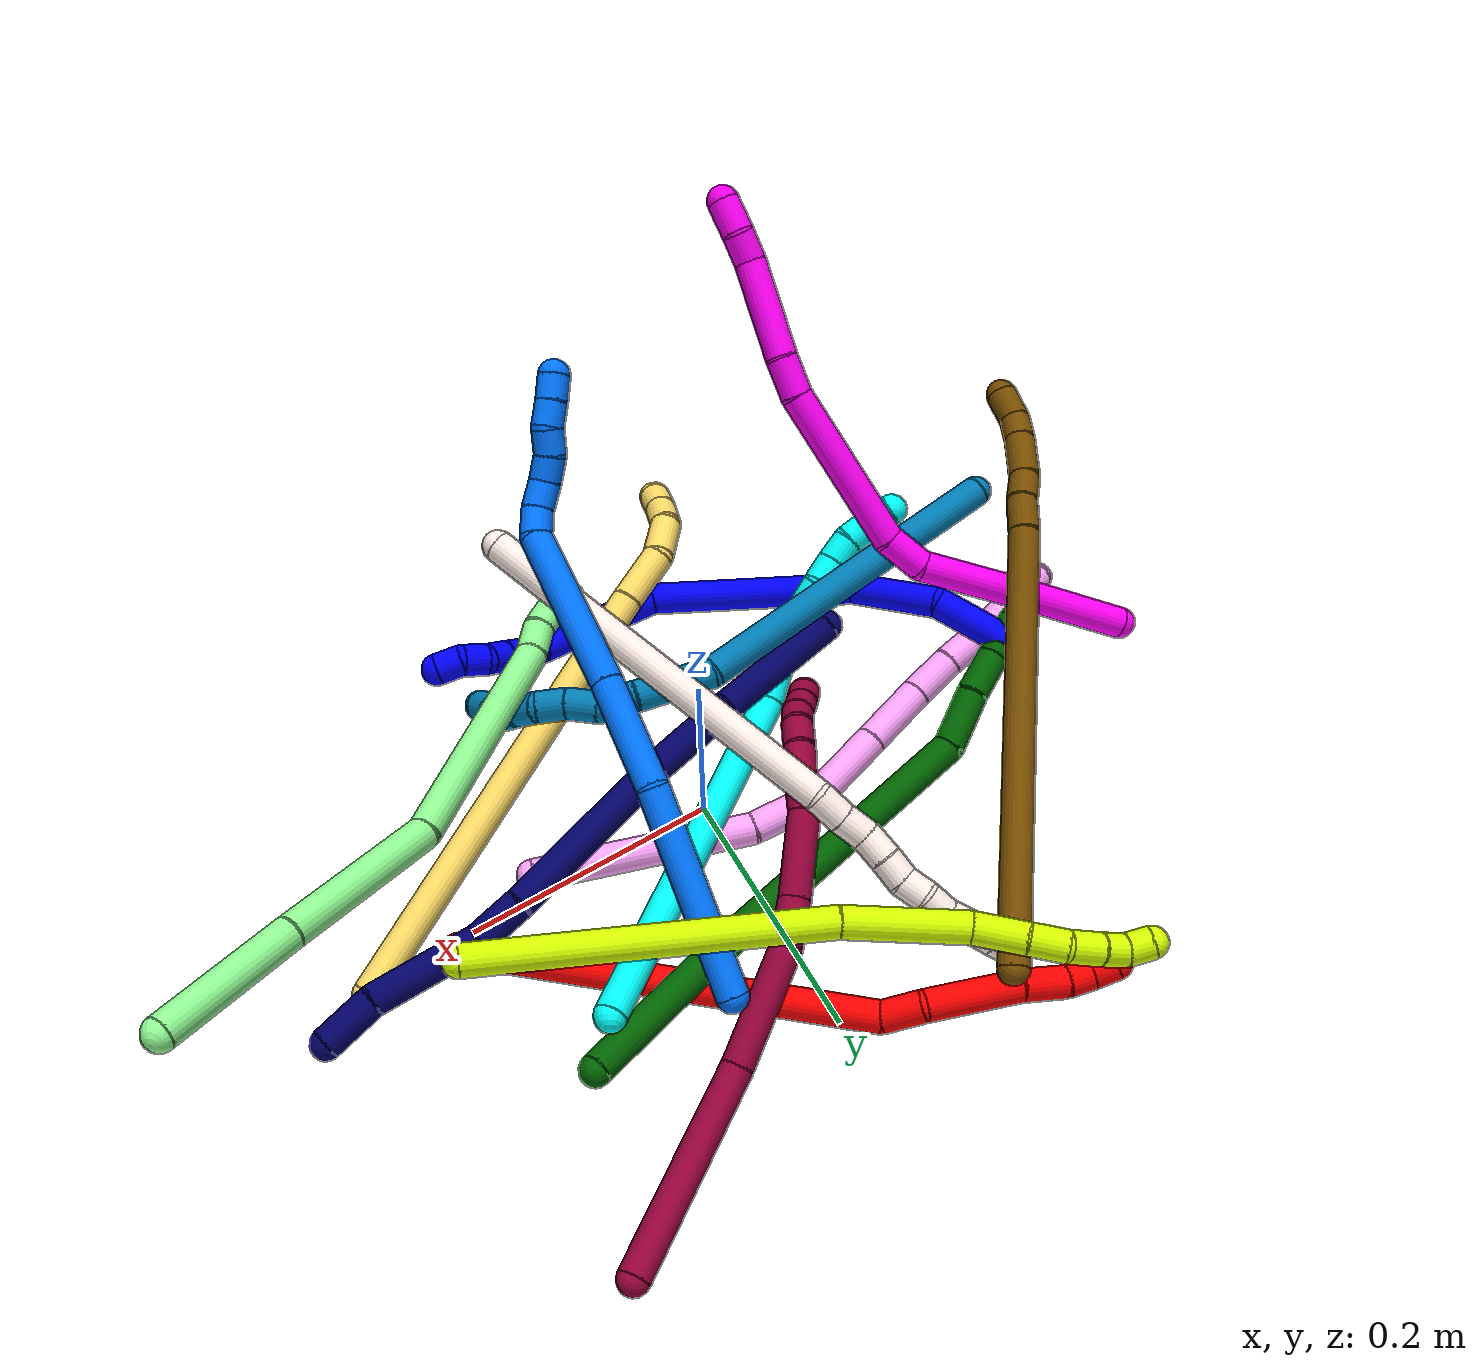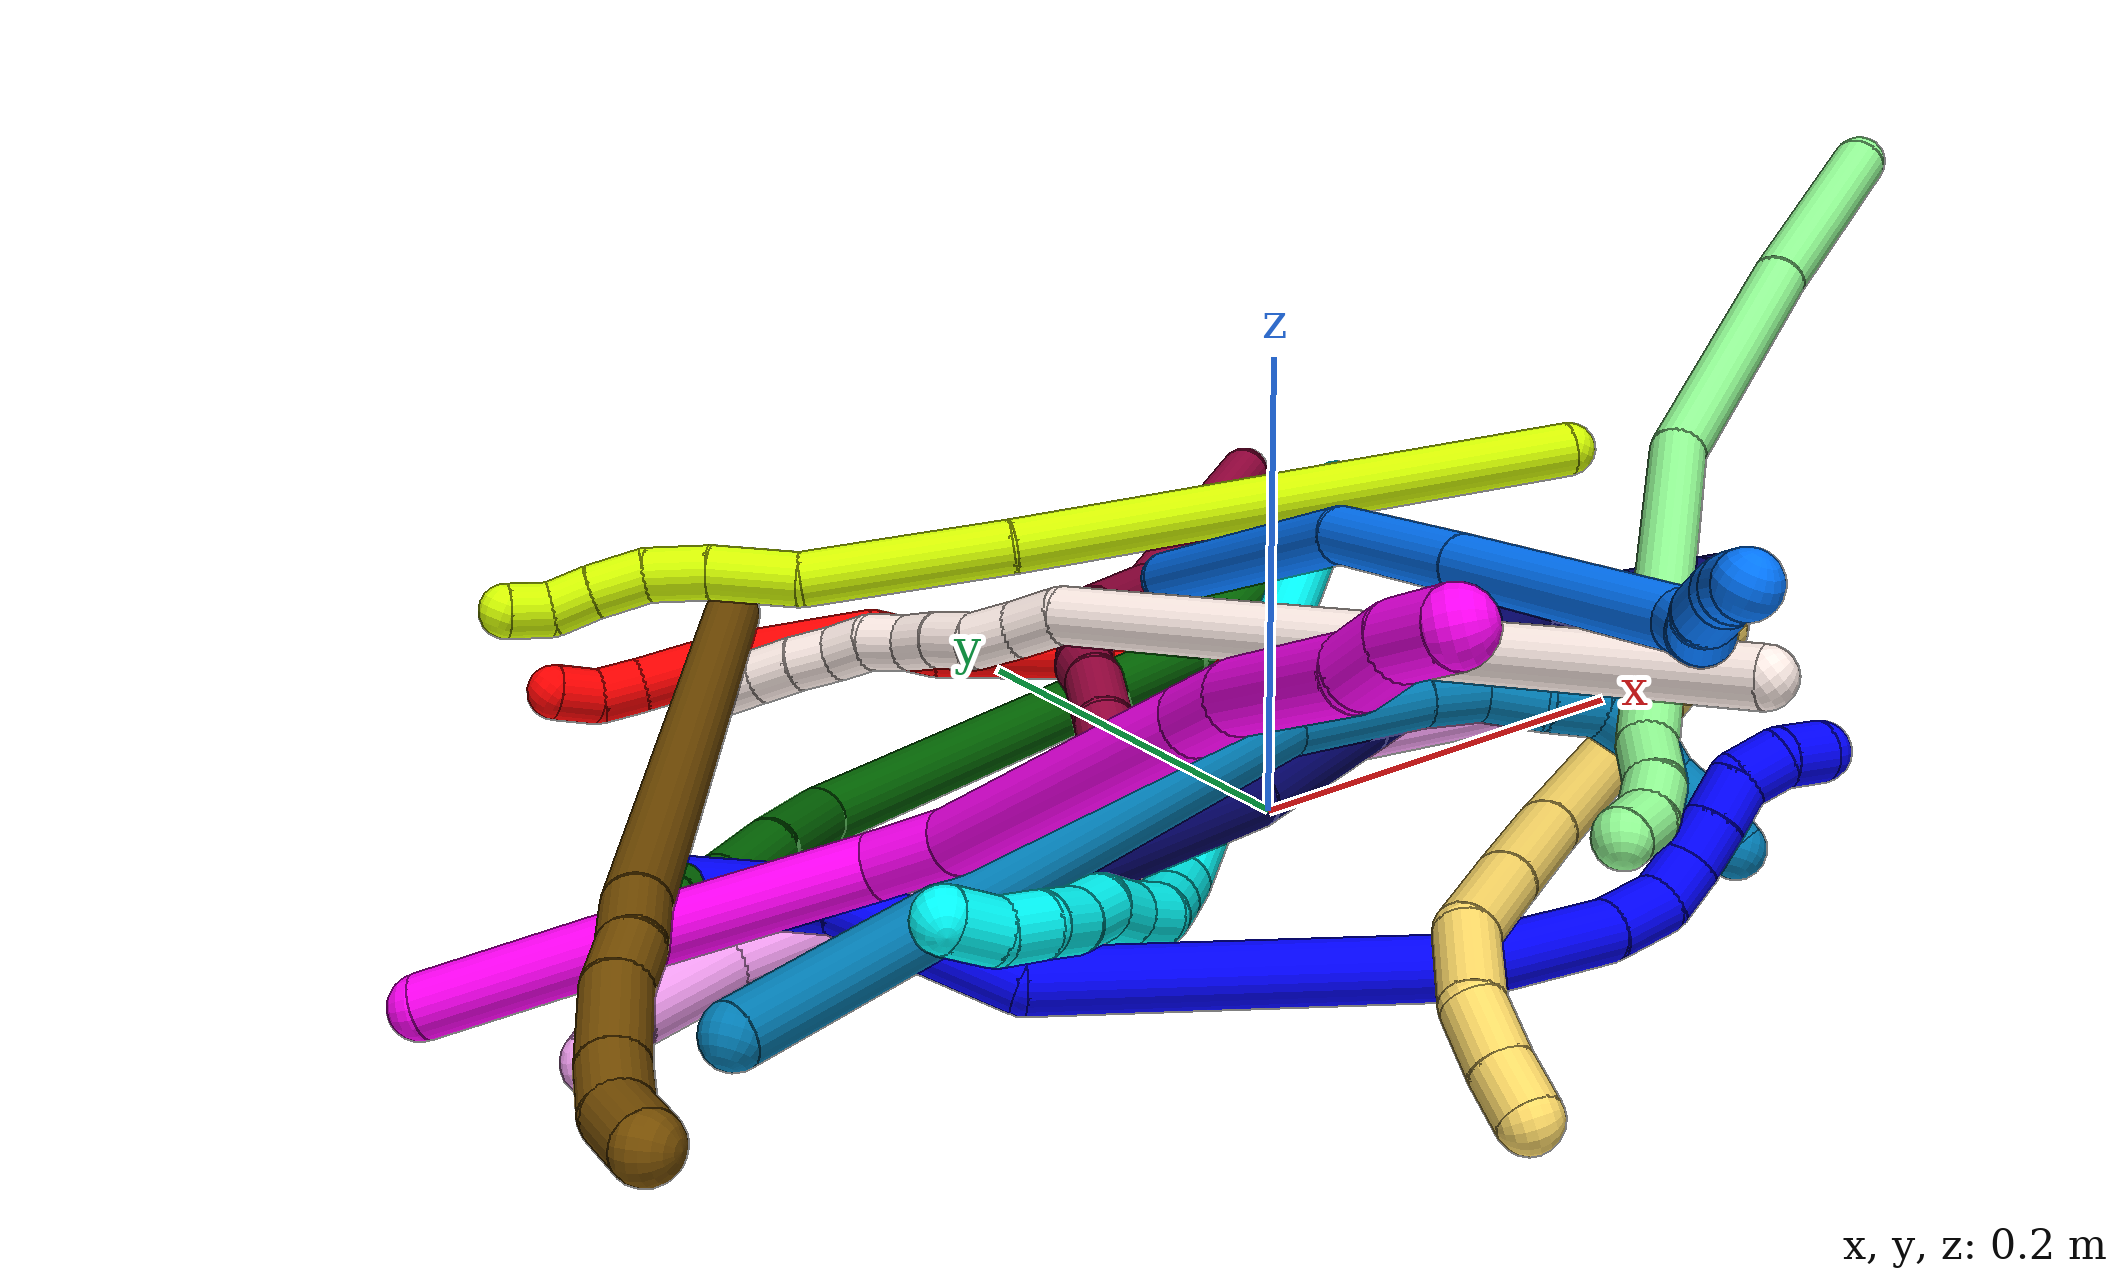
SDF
<sdf version="1.7">
 <world name="default">
  <plugin name="TubeGeneratorPlugin" filename="libtube_generator_plugin.so"/>
  <model name="photoneo_s_sensor">
   <static>1</static>
   <pose>0 0 2 1.57079 1.57079 3.14159</pose>
   <link name="link">
    <inertial><mass>0.1</mass></inertial>
    <sensor name="sensor" type="depth">
     <update_rate>30</update_rate>
     <camera>
      <horizontal_fov>1.22</horizontal_fov>
      <image><width>1920</width><height>1200</height><format>B8G8R8</format></image>
      <clip><near>0.1</near><far>4</far></clip>
      <depth_camera><output>points</output></depth_camera>
     </camera>
     <plugin name="camera_plugin" filename="libgazebo_ros_depth_camera.so">
      <baseline>0.2</baseline>
      <alwaysOn>1</alwaysOn>
      <updateRate>0.0</updateRate>
      <cameraName>camera_ir</cameraName>
      <imageTopicName>/camera/color/image_raw</imageTopicName>
      <cameraInfoTopicName>/camera/color/camera_info</cameraInfoTopicName>
      <depthImageTopicName>/camera/depth/image_raw</depthImageTopicName>
      <depthImageCameraInfoTopicName>/camera/depth/camera_info</depthImageCameraInfoTopicName>
      <pointCloudTopicName>/camera/depth/points</pointCloudTopicName>
      <frameName>fr_optical</frameName>
      <pointCloudCutoff>0.1</pointCloudCutoff>
      <pointCloudCutoffMax>2.0</pointCloudCutoffMax>
      <distortionK1>0</distortionK1>
      <distortionK2>0</distortionK2>
      <distortionK3>0</distortionK3>
      <distortionT1>0</distortionT1>
      <distortionT2>0</distortionT2>
      <CxPrime>0</CxPrime>
      <Cx>0</Cx>
      <Cy>0</Cy>
      <focalLength>0</focalLength>
      <hackBaseline>0</hackBaseline>
     </plugin>
    </sensor>
   </link>
  </model>
  <gravity>0 0 -9.8</gravity>
  <magnetic_field>6e-06 2.3e-05 -4.2e-05</magnetic_field>
  <atmosphere type="adiabatic"/>
  <physics name="default_physics" default="0" type="ode">
   <max_step_size>0.003</max_step_size>
   <real_time_factor>1</real_time_factor>
   <real_time_update_rate>1000</real_time_update_rate>
   <max_contacts>10000</max_contacts>
   <ode>
    <solver>
     <type>quick</type>
     <iters>100</iters>
     <sor>1.3</sor>
     <use_dynamic_moi_rescaling>0</use_dynamic_moi_rescaling>
    </solver>
    <constraints>
     <contact_max_correcting_vel>0</contact_max_correcting_vel>
     <contact_surface_layer>0.001</contact_surface_layer>
     <cfm>0</cfm>
     <erp>0.2</erp>
    </constraints>
   </ode>
  </physics>
  <scene><ambient>0.4 0.4 0.4 1</ambient><background>0.7 0.7 0.7 1</background><shadows>0</shadows></scene>
  <audio><device>default</device></audio>
  <spherical_coordinates>
   <surface_model>EARTH_WGS84</surface_model>
   <latitude_deg>0</latitude_deg>
   <longitude_deg>0</longitude_deg>
   <elevation>0</elevation>
   <heading_deg>0</heading_deg>
  </spherical_coordinates>
  <model name="bin">
   <static>1</static>
   <link name="bottom">
    <collision name="collision-bottom">
     <pose>0 0 -0.01 0 -0 0</pose>
     <geometry><box><size>0.8 0.6 0.02</size></box></geometry>
     <surface>
      <friction><ode><mu>100</mu><mu2>100</mu2></ode></friction>
      <contact><collide_bitmask>65535</collide_bitmask></contact>
     </surface>
    </collision>
   </link>
   <link name="west_wall">
    <collision name="collision-west_wall">
     <pose>-0.41 0 0.1 0 -0 0</pose>
     <geometry><box><size>0.02 0.6 0.2</size></box></geometry>
     <surface>
      <friction><ode><mu>100</mu><mu2>100</mu2></ode></friction>
      <contact><collide_bitmask>65535</collide_bitmask></contact>
     </surface>
    </collision>
   </link>
   <link name="east_wall">
    <collision name="collision-east_wall">
     <pose>0.41 0 0.1 0 -0 0</pose>
     <geometry><box><size>0.02 0.6 0.2</size></box></geometry>
     <surface>
      <friction><ode><mu>100</mu><mu2>100</mu2></ode></friction>
      <contact><collide_bitmask>65535</collide_bitmask></contact>
     </surface>
    </collision>
   </link>
   <link name="south_wall">
    <collision name="collision-south_wall">
     <pose>0 -0.31 0.1 0 -0 0</pose>
     <geometry><box><size>0.8 0.02 0.2</size></box></geometry>
     <surface>
      <friction><ode><mu>100</mu><mu2>100</mu2></ode></friction>
      <contact><collide_bitmask>65535</collide_bitmask></contact>
     </surface>
    </collision>
   </link>
   <link name="north_wall">
    <collision name="collision-north_wall">
     <pose>0 0.31 0.1 0 -0 0</pose>
     <geometry><box><size>0.8 0.02 0.2</size></box></geometry>
     <surface>
      <friction><ode><mu>100</mu><mu2>100</mu2></ode></friction>
      <contact><collide_bitmask>65535</collide_bitmask></contact>
     </surface>
    </collision>
   </link>
  </model>
  <model name="1">
   <static>0</static>
   <link name="1">
    <collision name="collision-cylinder-e_1_1_4">
     <pose>0.028466 -0.010663 0.007823 0.93786 1.13589 0.625313</pose>
     <geometry><cylinder><radius>0.0125</radius><length>0.062776</length></cylinder></geometry>
     <surface>
      <friction><ode><mu>1.16</mu><mu2>1.16</mu2><slip1>0</slip1><slip2>0</slip2></ode></friction>
      <contact><ode><kp>1e+06</kp><kd>1</kd><max_vel>0</max_vel><min_depth>0.001</min_depth></ode></contact>
     </surface>
    </collision>
    <visual name="visual-cylinder-e_1_1_4">
     <pose>0.028466 -0.010663 0.007823 0.93786 1.13589 0.625313</pose>
     <geometry><cylinder><radius>0.0125</radius><length>0.062776</length></cylinder></geometry>
     <material><ambient>0 0 1 1</ambient></material>
    </visual>
    <collision name="collision-cylinder-e_2_4_5">
     <pose>0.090402 -0.018773 0.031817 -0.156565 1.11587 -0.097831</pose>
     <geometry><cylinder><radius>0.0125</radius><length>0.074519</length></cylinder></geometry>
     <surface>
      <friction><ode><mu>1.16</mu><mu2>1.16</mu2><slip1>0</slip1><slip2>0</slip2></ode></friction>
      <contact><ode><kp>1e+06</kp><kd>1</kd><max_vel>0</max_vel><min_depth>0.001</min_depth></ode></contact>
     </surface>
    </collision>
    <visual name="visual-cylinder-e_2_4_5">
     <pose>0.090402 -0.018773 0.031817 -0.156565 1.11587 -0.097831</pose>
     <geometry><cylinder><radius>0.0125</radius><length>0.074519</length></cylinder></geometry>
     <material><ambient>0 0 1 1</ambient></material>
    </visual>
    <collision name="collision-cylinder-e_3_5_6">
     <pose>0.17591 -0.033404 0.107999 0.278877 0.694913 0.101567</pose>
     <geometry><cylinder><radius>0.0125</radius><length>0.162536</length></cylinder></geometry>
     <surface>
      <friction><ode><mu>1.16</mu><mu2>1.16</mu2><slip1>0</slip1><slip2>0</slip2></ode></friction>
      <contact><ode><kp>1e+06</kp><kd>1</kd><max_vel>0</max_vel><min_depth>0.001</min_depth></ode></contact>
     </surface>
    </collision>
    <visual name="visual-cylinder-e_3_5_6">
     <pose>0.17591 -0.033404 0.107999 0.278877 0.694913 0.101567</pose>
     <geometry><cylinder><radius>0.0125</radius><length>0.162536</length></cylinder></geometry>
     <material><ambient>0 0 1 1</ambient></material>
    </visual>
    <collision name="collision-cylinder-e_4_6_7">
     <pose>0.23801 -0.056555 0.201244 0.177658 0.289643 0.025977</pose>
     <geometry><cylinder><radius>0.0125</radius><length>0.070466</length></cylinder></geometry>
     <surface>
      <friction><ode><mu>1.16</mu><mu2>1.16</mu2><slip1>0</slip1><slip2>0</slip2></ode></friction>
      <contact><ode><kp>1e+06</kp><kd>1</kd><max_vel>0</max_vel><min_depth>0.001</min_depth></ode></contact>
     </surface>
    </collision>
    <visual name="visual-cylinder-e_4_6_7">
     <pose>0.23801 -0.056555 0.201244 0.177658 0.289643 0.025977</pose>
     <geometry><cylinder><radius>0.0125</radius><length>0.070466</length></cylinder></geometry>
     <material><ambient>0 0 1 1</ambient></material>
    </visual>
    <collision name="collision-cylinder-e_5_7_8">
     <pose>0.250615 -0.067047 0.248122 0.320253 0.175039 0.028341</pose>
     <geometry><cylinder><radius>0.0125</radius><length>0.029194</length></cylinder></geometry>
     <surface>
      <friction><ode><mu>1.16</mu><mu2>1.16</mu2><slip1>0</slip1><slip2>0</slip2></ode></friction>
      <contact><ode><kp>1e+06</kp><kd>1</kd><max_vel>0</max_vel><min_depth>0.001</min_depth></ode></contact>
     </surface>
    </collision>
    <visual name="visual-cylinder-e_5_7_8">
     <pose>0.250615 -0.067047 0.248122 0.320253 0.175039 0.028341</pose>
     <geometry><cylinder><radius>0.0125</radius><length>0.029194</length></cylinder></geometry>
     <material><ambient>0 0 1 1</ambient></material>
    </visual>
    <collision name="collision-cylinder-e_6_8_9">
     <pose>0.252883 -0.07829 0.269325 0.726447 -0.027111 -0.010305</pose>
     <geometry><cylinder><radius>0.0125</radius><length>0.020235</length></cylinder></geometry>
     <surface>
      <friction><ode><mu>1.16</mu><mu2>1.16</mu2><slip1>0</slip1><slip2>0</slip2></ode></friction>
      <contact><ode><kp>1e+06</kp><kd>1</kd><max_vel>0</max_vel><min_depth>0.001</min_depth></ode></contact>
     </surface>
    </collision>
    <visual name="visual-cylinder-e_6_8_9">
     <pose>0.252883 -0.07829 0.269325 0.726447 -0.027111 -0.010305</pose>
     <geometry><cylinder><radius>0.0125</radius><length>0.020235</length></cylinder></geometry>
     <material><ambient>0 0 1 1</ambient></material>
    </visual>
    <collision name="collision-cylinder-e_7_9_10">
     <pose>0.252086 -0.092704 0.283326 0.87398 -0.052032 -0.024309</pose>
     <geometry><cylinder><radius>0.0125</radius><length>0.020098</length></cylinder></geometry>
     <surface>
      <friction><ode><mu>1.16</mu><mu2>1.16</mu2><slip1>0</slip1><slip2>0</slip2></ode></friction>
      <contact><ode><kp>1e+06</kp><kd>1</kd><max_vel>0</max_vel><min_depth>0.001</min_depth></ode></contact>
     </surface>
    </collision>
    <visual name="visual-cylinder-e_7_9_10">
     <pose>0.252086 -0.092704 0.283326 0.87398 -0.052032 -0.024309</pose>
     <geometry><cylinder><radius>0.0125</radius><length>0.020098</length></cylinder></geometry>
     <material><ambient>0 0 1 1</ambient></material>
    </visual>
    <collision name="collision-cylinder-e_8_10_11">
     <pose>0.250657 -0.108091 0.29617 0.876581 -0.09039 -0.042388</pose>
     <geometry><cylinder><radius>0.0125</radius><length>0.020097</length></cylinder></geometry>
     <surface>
      <friction><ode><mu>1.16</mu><mu2>1.16</mu2><slip1>0</slip1><slip2>0</slip2></ode></friction>
      <contact><ode><kp>1e+06</kp><kd>1</kd><max_vel>0</max_vel><min_depth>0.001</min_depth></ode></contact>
     </surface>
    </collision>
    <visual name="visual-cylinder-e_8_10_11">
     <pose>0.250657 -0.108091 0.29617 0.876581 -0.09039 -0.042388</pose>
     <geometry><cylinder><radius>0.0125</radius><length>0.020097</length></cylinder></geometry>
     <material><ambient>0 0 1 1</ambient></material>
    </visual>
    <collision name="collision-cylinder-e_9_11_12">
     <pose>0.253348 -0.121557 0.309914 0.666477 0.367687 0.12855</pose>
     <geometry><cylinder><radius>0.0125</radius><length>0.02002</length></cylinder></geometry>
     <surface>
      <friction><ode><mu>1.16</mu><mu2>1.16</mu2><slip1>0</slip1><slip2>0</slip2></ode></friction>
      <contact><ode><kp>1e+06</kp><kd>1</kd><max_vel>0</max_vel><min_depth>0.001</min_depth></ode></contact>
     </surface>
    </collision>
    <visual name="visual-cylinder-e_9_11_12">
     <pose>0.253348 -0.121557 0.309914 0.666477 0.367687 0.12855</pose>
     <geometry><cylinder><radius>0.0125</radius><length>0.02002</length></cylinder></geometry>
     <material><ambient>0 0 1 1</ambient></material>
    </visual>
    <collision name="collision-cylinder-e_10_12_2">
     <pose>0.260594 -0.128933 0.326459 0.172205 0.372349 0.032513</pose>
     <geometry><cylinder><radius>0.0125</radius><length>0.020058</length></cylinder></geometry>
     <surface>
      <friction><ode><mu>1.16</mu><mu2>1.16</mu2><slip1>0</slip1><slip2>0</slip2></ode></friction>
      <contact><ode><kp>1e+06</kp><kd>1</kd><max_vel>0</max_vel><min_depth>0.001</min_depth></ode></contact>
     </surface>
    </collision>
    <visual name="visual-cylinder-e_10_12_2">
     <pose>0.260594 -0.128933 0.326459 0.172205 0.372349 0.032513</pose>
     <geometry><cylinder><radius>0.0125</radius><length>0.020058</length></cylinder></geometry>
     <material><ambient>0 0 1 1</ambient></material>
    </visual>
    <collision name="collision-sphere-2">
     <pose>0.264243 -0.130533 0.335663 0 -0 0</pose>
     <geometry><sphere><radius>0.0125</radius></sphere></geometry>
     <surface>
      <friction><ode><mu>1.16</mu><mu2>1.16</mu2><slip1>0</slip1><slip2>0</slip2></ode></friction>
      <contact><ode><kp>1e+06</kp><kd>1</kd><max_vel>0</max_vel><min_depth>0.001</min_depth></ode></contact>
     </surface>
    </collision>
    <visual name="visual-sphere-2">
     <pose>0.264243 -0.130533 0.335663 0 -0 0</pose>
     <geometry><sphere><radius>0.0125</radius></sphere></geometry>
     <material><ambient>0 0 1 1</ambient></material>
    </visual>
    <collision name="collision-sphere-12">
     <pose>0.256946 -0.127332 0.317256 0 -0 0</pose>
     <geometry><sphere><radius>0.0125</radius></sphere></geometry>
     <surface>
      <friction><ode><mu>1.16</mu><mu2>1.16</mu2><slip1>0</slip1><slip2>0</slip2></ode></friction>
      <contact><ode><kp>1e+06</kp><kd>1</kd><max_vel>0</max_vel><min_depth>0.001</min_depth></ode></contact>
     </surface>
    </collision>
    <visual name="visual-sphere-12">
     <pose>0.256946 -0.127332 0.317256 0 -0 0</pose>
     <geometry><sphere><radius>0.0125</radius></sphere></geometry>
     <material><ambient>0 0 1 1</ambient></material>
    </visual>
    <collision name="collision-sphere-11">
     <pose>0.24975 -0.115783 0.302572 0 -0 0</pose>
     <geometry><sphere><radius>0.0125</radius></sphere></geometry>
     <surface>
      <friction><ode><mu>1.16</mu><mu2>1.16</mu2><slip1>0</slip1><slip2>0</slip2></ode></friction>
      <contact><ode><kp>1e+06</kp><kd>1</kd><max_vel>0</max_vel><min_depth>0.001</min_depth></ode></contact>
     </surface>
    </collision>
    <visual name="visual-sphere-11">
     <pose>0.24975 -0.115783 0.302572 0 -0 0</pose>
     <geometry><sphere><radius>0.0125</radius></sphere></geometry>
     <material><ambient>0 0 1 1</ambient></material>
    </visual>
    <collision name="collision-sphere-10">
     <pose>0.251564 -0.1004 0.289767 0 -0 0</pose>
     <geometry><sphere><radius>0.0125</radius></sphere></geometry>
     <surface>
      <friction><ode><mu>1.16</mu><mu2>1.16</mu2><slip1>0</slip1><slip2>0</slip2></ode></friction>
      <contact><ode><kp>1e+06</kp><kd>1</kd><max_vel>0</max_vel><min_depth>0.001</min_depth></ode></contact>
     </surface>
    </collision>
    <visual name="visual-sphere-10">
     <pose>0.251564 -0.1004 0.289767 0 -0 0</pose>
     <geometry><sphere><radius>0.0125</radius></sphere></geometry>
     <material><ambient>0 0 1 1</ambient></material>
    </visual>
    <collision name="collision-sphere-9">
     <pose>0.252609 -0.085008 0.276886 0 -0 0</pose>
     <geometry><sphere><radius>0.0125</radius></sphere></geometry>
     <surface>
      <friction><ode><mu>1.16</mu><mu2>1.16</mu2><slip1>0</slip1><slip2>0</slip2></ode></friction>
      <contact><ode><kp>1e+06</kp><kd>1</kd><max_vel>0</max_vel><min_depth>0.001</min_depth></ode></contact>
     </surface>
    </collision>
    <visual name="visual-sphere-9">
     <pose>0.252609 -0.085008 0.276886 0 -0 0</pose>
     <geometry><sphere><radius>0.0125</radius></sphere></geometry>
     <material><ambient>0 0 1 1</ambient></material>
    </visual>
    <collision name="collision-sphere-4">
     <pose>0.056932 -0.021326 0.015645 0 -0 0</pose>
     <geometry><sphere><radius>0.0125</radius></sphere></geometry>
     <surface>
      <friction><ode><mu>1.16</mu><mu2>1.16</mu2><slip1>0</slip1><slip2>0</slip2></ode></friction>
      <contact><ode><kp>1e+06</kp><kd>1</kd><max_vel>0</max_vel><min_depth>0.001</min_depth></ode></contact>
     </surface>
    </collision>
    <visual name="visual-sphere-4">
     <pose>0.056932 -0.021326 0.015645 0 -0 0</pose>
     <geometry><sphere><radius>0.0125</radius></sphere></geometry>
     <material><ambient>0 0 1 1</ambient></material>
    </visual>
    <collision name="collision-sphere-1">
     <geometry><sphere><radius>0.0125</radius></sphere></geometry>
     <surface>
      <friction><ode><mu>1.16</mu><mu2>1.16</mu2><slip1>0</slip1><slip2>0</slip2></ode></friction>
      <contact><ode><kp>1e+06</kp><kd>1</kd><max_vel>0</max_vel><min_depth>0.001</min_depth></ode></contact>
     </surface>
    </collision>
    <visual name="visual-sphere-1">
     <geometry><sphere><radius>0.0125</radius></sphere></geometry>
     <material><ambient>0 0 1 1</ambient></material>
    </visual>
    <collision name="collision-sphere-8">
     <pose>0.253157 -0.071572 0.261765 0 -0 0</pose>
     <geometry><sphere><radius>0.0125</radius></sphere></geometry>
     <surface>
      <friction><ode><mu>1.16</mu><mu2>1.16</mu2><slip1>0</slip1><slip2>0</slip2></ode></friction>
      <contact><ode><kp>1e+06</kp><kd>1</kd><max_vel>0</max_vel><min_depth>0.001</min_depth></ode></contact>
     </surface>
    </collision>
    <visual name="visual-sphere-8">
     <pose>0.253157 -0.071572 0.261765 0 -0 0</pose>
     <geometry><sphere><radius>0.0125</radius></sphere></geometry>
     <material><ambient>0 0 1 1</ambient></material>
    </visual>
    <collision name="collision-sphere-5">
     <pose>0.123873 -0.016221 0.047988 0 -0 0</pose>
     <geometry><sphere><radius>0.0125</radius></sphere></geometry>
     <surface>
      <friction><ode><mu>1.16</mu><mu2>1.16</mu2><slip1>0</slip1><slip2>0</slip2></ode></friction>
      <contact><ode><kp>1e+06</kp><kd>1</kd><max_vel>0</max_vel><min_depth>0.001</min_depth></ode></contact>
     </surface>
    </collision>
    <visual name="visual-sphere-5">
     <pose>0.123873 -0.016221 0.047988 0 -0 0</pose>
     <geometry><sphere><radius>0.0125</radius></sphere></geometry>
     <material><ambient>0 0 1 1</ambient></material>
    </visual>
    <collision name="collision-sphere-6">
     <pose>0.227947 -0.050588 0.16801 0 -0 0</pose>
     <geometry><sphere><radius>0.0125</radius></sphere></geometry>
     <surface>
      <friction><ode><mu>1.16</mu><mu2>1.16</mu2><slip1>0</slip1><slip2>0</slip2></ode></friction>
      <contact><ode><kp>1e+06</kp><kd>1</kd><max_vel>0</max_vel><min_depth>0.001</min_depth></ode></contact>
     </surface>
    </collision>
    <visual name="visual-sphere-6">
     <pose>0.227947 -0.050588 0.16801 0 -0 0</pose>
     <geometry><sphere><radius>0.0125</radius></sphere></geometry>
     <material><ambient>0 0 1 1</ambient></material>
    </visual>
    <collision name="collision-sphere-7">
     <pose>0.248073 -0.062522 0.234479 0 -0 0</pose>
     <geometry><sphere><radius>0.0125</radius></sphere></geometry>
     <surface>
      <friction><ode><mu>1.16</mu><mu2>1.16</mu2><slip1>0</slip1><slip2>0</slip2></ode></friction>
      <contact><ode><kp>1e+06</kp><kd>1</kd><max_vel>0</max_vel><min_depth>0.001</min_depth></ode></contact>
     </surface>
    </collision>
    <visual name="visual-sphere-7">
     <pose>0.248073 -0.062522 0.234479 0 -0 0</pose>
     <geometry><sphere><radius>0.0125</radius></sphere></geometry>
     <material><ambient>0 0 1 1</ambient></material>
    </visual>
    <inertial>
     <pose>0.173447 -0.048159 0.143378 0 -0 0</pose>
     <mass>0.5</mass>
     <inertia>
      <ixx>0.000397</ixx>
      <ixy>0</ixy>
      <ixz>0</ixz>
      <iyy>0.000476</iyy>
      <iyz>0</iyz>
      <izz>-0.000179</izz>
     </inertia>
    </inertial>
   </link>
   <pose>-0.270213 0.012287 0.039885 -1.75525 0.186822 -1.37302</pose>
  </model>
  <model name="2">
   <static>0</static>
   <link name="2">
    <collision name="collision-cylinder-e_1_1_4">
     <pose>-0.067839 0.065614 0.127419 -0.47553 -0.442089 0.108812</pose>
     <geometry><cylinder><radius>0.0125</radius><length>0.317131</length></cylinder></geometry>
     <surface>
      <friction><ode><mu>1.16</mu><mu2>1.16</mu2><slip1>0</slip1><slip2>0</slip2></ode></friction>
      <contact><ode><kp>1e+06</kp><kd>1</kd><max_vel>0</max_vel><min_depth>0.001</min_depth></ode></contact>
     </surface>
    </collision>
    <visual name="visual-cylinder-e_1_1_4">
     <pose>-0.067839 0.065614 0.127419 -0.47553 -0.442089 0.108812</pose>
     <geometry><cylinder><radius>0.0125</radius><length>0.317131</length></cylinder></geometry>
     <material><ambient>1 0 0 1</ambient></material>
    </visual>
    <collision name="collision-cylinder-e_2_4_5">
     <pose>-0.145838 0.131113 0.267655 0.008903 -0.670307 -0.003101</pose>
     <geometry><cylinder><radius>0.0125</radius><length>0.032711</length></cylinder></geometry>
     <surface>
      <friction><ode><mu>1.16</mu><mu2>1.16</mu2><slip1>0</slip1><slip2>0</slip2></ode></friction>
      <contact><ode><kp>1e+06</kp><kd>1</kd><max_vel>0</max_vel><min_depth>0.001</min_depth></ode></contact>
     </surface>
    </collision>
    <visual name="visual-cylinder-e_2_4_5">
     <pose>-0.145838 0.131113 0.267655 0.008903 -0.670307 -0.003101</pose>
     <geometry><cylinder><radius>0.0125</radius><length>0.032711</length></cylinder></geometry>
     <material><ambient>1 0 0 1</ambient></material>
    </visual>
    <collision name="collision-cylinder-e_3_5_6">
     <pose>-0.18323 0.142301 0.302328 -0.477218 -0.836011 0.215253</pose>
     <geometry><cylinder><radius>0.0125</radius><length>0.073403</length></cylinder></geometry>
     <surface>
      <friction><ode><mu>1.16</mu><mu2>1.16</mu2><slip1>0</slip1><slip2>0</slip2></ode></friction>
      <contact><ode><kp>1e+06</kp><kd>1</kd><max_vel>0</max_vel><min_depth>0.001</min_depth></ode></contact>
     </surface>
    </collision>
    <visual name="visual-cylinder-e_3_5_6">
     <pose>-0.18323 0.142301 0.302328 -0.477218 -0.836011 0.215253</pose>
     <geometry><cylinder><radius>0.0125</radius><length>0.073403</length></cylinder></geometry>
     <material><ambient>1 0 0 1</ambient></material>
    </visual>
    <collision name="collision-cylinder-e_4_6_7">
     <pose>-0.222902 0.161967 0.333886 -0.711547 -0.770776 0.299232</pose>
     <geometry><cylinder><radius>0.0125</radius><length>0.035714</length></cylinder></geometry>
     <surface>
      <friction><ode><mu>1.16</mu><mu2>1.16</mu2><slip1>0</slip1><slip2>0</slip2></ode></friction>
      <contact><ode><kp>1e+06</kp><kd>1</kd><max_vel>0</max_vel><min_depth>0.001</min_depth></ode></contact>
     </surface>
    </collision>
    <visual name="visual-cylinder-e_4_6_7">
     <pose>-0.222902 0.161967 0.333886 -0.711547 -0.770776 0.299232</pose>
     <geometry><cylinder><radius>0.0125</radius><length>0.035714</length></cylinder></geometry>
     <material><ambient>1 0 0 1</ambient></material>
    </visual>
    <collision name="collision-cylinder-e_5_7_8">
     <pose>-0.243911 0.173399 0.348756 -0.535611 -0.959151 0.283498</pose>
     <geometry><cylinder><radius>0.0125</radius><length>0.020931</length></cylinder></geometry>
     <surface>
      <friction><ode><mu>1.16</mu><mu2>1.16</mu2><slip1>0</slip1><slip2>0</slip2></ode></friction>
      <contact><ode><kp>1e+06</kp><kd>1</kd><max_vel>0</max_vel><min_depth>0.001</min_depth></ode></contact>
     </surface>
    </collision>
    <visual name="visual-cylinder-e_5_7_8">
     <pose>-0.243911 0.173399 0.348756 -0.535611 -0.959151 0.283498</pose>
     <geometry><cylinder><radius>0.0125</radius><length>0.020931</length></cylinder></geometry>
     <material><ambient>1 0 0 1</ambient></material>
    </visual>
    <collision name="collision-cylinder-e_6_8_2">
     <pose>-0.259849 0.176351 0.360763 0.016842 -0.822651 -0.007347</pose>
     <geometry><cylinder><radius>0.0125</radius><length>0.020111</length></cylinder></geometry>
     <surface>
      <friction><ode><mu>1.16</mu><mu2>1.16</mu2><slip1>0</slip1><slip2>0</slip2></ode></friction>
      <contact><ode><kp>1e+06</kp><kd>1</kd><max_vel>0</max_vel><min_depth>0.001</min_depth></ode></contact>
     </surface>
    </collision>
    <visual name="visual-cylinder-e_6_8_2">
     <pose>-0.259849 0.176351 0.360763 0.016842 -0.822651 -0.007347</pose>
     <geometry><cylinder><radius>0.0125</radius><length>0.020111</length></cylinder></geometry>
     <material><ambient>1 0 0 1</ambient></material>
    </visual>
    <collision name="collision-sphere-2">
     <pose>-0.267219 0.176236 0.367603 0 -0 0</pose>
     <geometry><sphere><radius>0.0125</radius></sphere></geometry>
     <surface>
      <friction><ode><mu>1.16</mu><mu2>1.16</mu2><slip1>0</slip1><slip2>0</slip2></ode></friction>
      <contact><ode><kp>1e+06</kp><kd>1</kd><max_vel>0</max_vel><min_depth>0.001</min_depth></ode></contact>
     </surface>
    </collision>
    <visual name="visual-sphere-2">
     <pose>-0.267219 0.176236 0.367603 0 -0 0</pose>
     <geometry><sphere><radius>0.0125</radius></sphere></geometry>
     <material><ambient>1 0 0 1</ambient></material>
    </visual>
    <collision name="collision-sphere-4">
     <pose>-0.135678 0.131227 0.254839 0 -0 0</pose>
     <geometry><sphere><radius>0.0125</radius></sphere></geometry>
     <surface>
      <friction><ode><mu>1.16</mu><mu2>1.16</mu2><slip1>0</slip1><slip2>0</slip2></ode></friction>
      <contact><ode><kp>1e+06</kp><kd>1</kd><max_vel>0</max_vel><min_depth>0.001</min_depth></ode></contact>
     </surface>
    </collision>
    <visual name="visual-sphere-4">
     <pose>-0.135678 0.131227 0.254839 0 -0 0</pose>
     <geometry><sphere><radius>0.0125</radius></sphere></geometry>
     <material><ambient>1 0 0 1</ambient></material>
    </visual>
    <collision name="collision-sphere-1">
     <geometry><sphere><radius>0.0125</radius></sphere></geometry>
     <surface>
      <friction><ode><mu>1.16</mu><mu2>1.16</mu2><slip1>0</slip1><slip2>0</slip2></ode></friction>
      <contact><ode><kp>1e+06</kp><kd>1</kd><max_vel>0</max_vel><min_depth>0.001</min_depth></ode></contact>
     </surface>
    </collision>
    <visual name="visual-sphere-1">
     <geometry><sphere><radius>0.0125</radius></sphere></geometry>
     <material><ambient>1 0 0 1</ambient></material>
    </visual>
    <collision name="collision-sphere-8">
     <pose>-0.252479 0.176466 0.353924 0 -0 0</pose>
     <geometry><sphere><radius>0.0125</radius></sphere></geometry>
     <surface>
      <friction><ode><mu>1.16</mu><mu2>1.16</mu2><slip1>0</slip1><slip2>0</slip2></ode></friction>
      <contact><ode><kp>1e+06</kp><kd>1</kd><max_vel>0</max_vel><min_depth>0.001</min_depth></ode></contact>
     </surface>
    </collision>
    <visual name="visual-sphere-8">
     <pose>-0.252479 0.176466 0.353924 0 -0 0</pose>
     <geometry><sphere><radius>0.0125</radius></sphere></geometry>
     <material><ambient>1 0 0 1</ambient></material>
    </visual>
    <collision name="collision-sphere-5">
     <pose>-0.155999 0.130999 0.280471 0 -0 0</pose>
     <geometry><sphere><radius>0.0125</radius></sphere></geometry>
     <surface>
      <friction><ode><mu>1.16</mu><mu2>1.16</mu2><slip1>0</slip1><slip2>0</slip2></ode></friction>
      <contact><ode><kp>1e+06</kp><kd>1</kd><max_vel>0</max_vel><min_depth>0.001</min_depth></ode></contact>
     </surface>
    </collision>
    <visual name="visual-sphere-5">
     <pose>-0.155999 0.130999 0.280471 0 -0 0</pose>
     <geometry><sphere><radius>0.0125</radius></sphere></geometry>
     <material><ambient>1 0 0 1</ambient></material>
    </visual>
    <collision name="collision-sphere-6">
     <pose>-0.210462 0.153602 0.324185 0 -0 0</pose>
     <geometry><sphere><radius>0.0125</radius></sphere></geometry>
     <surface>
      <friction><ode><mu>1.16</mu><mu2>1.16</mu2><slip1>0</slip1><slip2>0</slip2></ode></friction>
      <contact><ode><kp>1e+06</kp><kd>1</kd><max_vel>0</max_vel><min_depth>0.001</min_depth></ode></contact>
     </surface>
    </collision>
    <visual name="visual-sphere-6">
     <pose>-0.210462 0.153602 0.324185 0 -0 0</pose>
     <geometry><sphere><radius>0.0125</radius></sphere></geometry>
     <material><ambient>1 0 0 1</ambient></material>
    </visual>
    <collision name="collision-sphere-7">
     <pose>-0.235343 0.170333 0.343588 0 -0 0</pose>
     <geometry><sphere><radius>0.0125</radius></sphere></geometry>
     <surface>
      <friction><ode><mu>1.16</mu><mu2>1.16</mu2><slip1>0</slip1><slip2>0</slip2></ode></friction>
      <contact><ode><kp>1e+06</kp><kd>1</kd><max_vel>0</max_vel><min_depth>0.001</min_depth></ode></contact>
     </surface>
    </collision>
    <visual name="visual-sphere-7">
     <pose>-0.235343 0.170333 0.343588 0 -0 0</pose>
     <geometry><sphere><radius>0.0125</radius></sphere></geometry>
     <material><ambient>1 0 0 1</ambient></material>
    </visual>
    <inertial>
     <pose>-0.116051 0.097005 0.19567 0 -0 0</pose>
     <mass>0.5</mass>
     <inertia>
      <ixx>0.002679</ixx>
      <ixy>0</ixy>
      <ixz>0</ixz>
      <iyy>0.002744</iyy>
      <iyz>0</iyz>
      <izz>8.7e-05</izz>
     </inertia>
    </inertial>
   </link>
   <pose>0.216793 0.010405 0.01269 -1.05056 -0.09591 0.426773</pose>
  </model>
  <model name="3">
   <static>0</static>
   <link name="3">
    <collision name="collision-cylinder-e_1_1_4">
     <pose>-0.061236 -0.010171 -0.140804 3.06948 -0.409279 -2.79744</pose>
     <geometry><cylinder><radius>0.0125</radius><length>0.307759</length></cylinder></geometry>
     <surface>
      <friction><ode><mu>1.16</mu><mu2>1.16</mu2><slip1>0</slip1><slip2>0</slip2></ode></friction>
      <contact><ode><kp>1e+06</kp><kd>1</kd><max_vel>0</max_vel><min_depth>0.001</min_depth></ode></contact>
     </surface>
    </collision>
    <visual name="visual-cylinder-e_1_1_4">
     <pose>-0.061236 -0.010171 -0.140804 3.06948 -0.409279 -2.79744</pose>
     <geometry><cylinder><radius>0.0125</radius><length>0.307759</length></cylinder></geometry>
     <material><ambient>0.003922 1 0.996078 1</ambient></material>
    </visual>
    <collision name="collision-cylinder-e_2_4_5">
     <pose>-0.123749 -0.026911 -0.297209 2.74305 -0.07531 -0.368851</pose>
     <geometry><cylinder><radius>0.0125</radius><length>0.033953</length></cylinder></geometry>
     <surface>
      <friction><ode><mu>1.16</mu><mu2>1.16</mu2><slip1>0</slip1><slip2>0</slip2></ode></friction>
      <contact><ode><kp>1e+06</kp><kd>1</kd><max_vel>0</max_vel><min_depth>0.001</min_depth></ode></contact>
     </surface>
    </collision>
    <visual name="visual-cylinder-e_2_4_5">
     <pose>-0.123749 -0.026911 -0.297209 2.74305 -0.07531 -0.368851</pose>
     <geometry><cylinder><radius>0.0125</radius><length>0.033953</length></cylinder></geometry>
     <material><ambient>0.003922 1 0.996078 1</ambient></material>
    </visual>
    <collision name="collision-cylinder-e_3_5_6">
     <pose>-0.125438 -0.039646 -0.325753 2.69699 -0.028649 -0.126582</pose>
     <geometry><cylinder><radius>0.0125</radius><length>0.028684</length></cylinder></geometry>
     <surface>
      <friction><ode><mu>1.16</mu><mu2>1.16</mu2><slip1>0</slip1><slip2>0</slip2></ode></friction>
      <contact><ode><kp>1e+06</kp><kd>1</kd><max_vel>0</max_vel><min_depth>0.001</min_depth></ode></contact>
     </surface>
    </collision>
    <visual name="visual-cylinder-e_3_5_6">
     <pose>-0.125438 -0.039646 -0.325753 2.69699 -0.028649 -0.126582</pose>
     <geometry><cylinder><radius>0.0125</radius><length>0.028684</length></cylinder></geometry>
     <material><ambient>0.003922 1 0.996078 1</ambient></material>
    </visual>
    <collision name="collision-cylinder-e_4_6_7">
     <pose>-0.128818 -0.053556 -0.34574 2.30897 -0.276438 -0.609613</pose>
     <geometry><cylinder><radius>0.0125</radius><length>0.021764</length></cylinder></geometry>
     <surface>
      <friction><ode><mu>1.16</mu><mu2>1.16</mu2><slip1>0</slip1><slip2>0</slip2></ode></friction>
      <contact><ode><kp>1e+06</kp><kd>1</kd><max_vel>0</max_vel><min_depth>0.001</min_depth></ode></contact>
     </surface>
    </collision>
    <visual name="visual-cylinder-e_4_6_7">
     <pose>-0.128818 -0.053556 -0.34574 2.30897 -0.276438 -0.609613</pose>
     <geometry><cylinder><radius>0.0125</radius><length>0.021764</length></cylinder></geometry>
     <material><ambient>0.003922 1 0.996078 1</ambient></material>
    </visual>
    <collision name="collision-cylinder-e_5_7_8">
     <pose>-0.133373 -0.069403 -0.359881 2.29006 -0.146055 -0.319873</pose>
     <geometry><cylinder><radius>0.0125</radius><length>0.021773</length></cylinder></geometry>
     <surface>
      <friction><ode><mu>1.16</mu><mu2>1.16</mu2><slip1>0</slip1><slip2>0</slip2></ode></friction>
      <contact><ode><kp>1e+06</kp><kd>1</kd><max_vel>0</max_vel><min_depth>0.001</min_depth></ode></contact>
     </surface>
    </collision>
    <visual name="visual-cylinder-e_5_7_8">
     <pose>-0.133373 -0.069403 -0.359881 2.29006 -0.146055 -0.319873</pose>
     <geometry><cylinder><radius>0.0125</radius><length>0.021773</length></cylinder></geometry>
     <material><ambient>0.003922 1 0.996078 1</ambient></material>
    </visual>
    <collision name="collision-cylinder-e_6_8_9">
     <pose>-0.138463 -0.082892 -0.375727 2.58979 -0.328764 -1.05995</pose>
     <geometry><cylinder><radius>0.0125</radius><length>0.021714</length></cylinder></geometry>
     <surface>
      <friction><ode><mu>1.16</mu><mu2>1.16</mu2><slip1>0</slip1><slip2>0</slip2></ode></friction>
      <contact><ode><kp>1e+06</kp><kd>1</kd><max_vel>0</max_vel><min_depth>0.001</min_depth></ode></contact>
     </surface>
    </collision>
    <visual name="visual-cylinder-e_6_8_9">
     <pose>-0.138463 -0.082892 -0.375727 2.58979 -0.328764 -1.05995</pose>
     <geometry><cylinder><radius>0.0125</radius><length>0.021714</length></cylinder></geometry>
     <material><ambient>0.003922 1 0.996078 1</ambient></material>
    </visual>
    <collision name="collision-cylinder-e_7_9_10">
     <pose>-0.145179 -0.095239 -0.392122 2.40302 -0.301177 -0.747259</pose>
     <geometry><cylinder><radius>0.0125</radius><length>0.02165</length></cylinder></geometry>
     <surface>
      <friction><ode><mu>1.16</mu><mu2>1.16</mu2><slip1>0</slip1><slip2>0</slip2></ode></friction>
      <contact><ode><kp>1e+06</kp><kd>1</kd><max_vel>0</max_vel><min_depth>0.001</min_depth></ode></contact>
     </surface>
    </collision>
    <visual name="visual-cylinder-e_7_9_10">
     <pose>-0.145179 -0.095239 -0.392122 2.40302 -0.301177 -0.747259</pose>
     <geometry><cylinder><radius>0.0125</radius><length>0.02165</length></cylinder></geometry>
     <material><ambient>0.003922 1 0.996078 1</ambient></material>
    </visual>
    <collision name="collision-cylinder-e_8_10_11">
     <pose>-0.154105 -0.108791 -0.405528 2.28912 -0.578257 -1.1599</pose>
     <geometry><cylinder><radius>0.0125</radius><length>0.02091</length></cylinder></geometry>
     <surface>
      <friction><ode><mu>1.16</mu><mu2>1.16</mu2><slip1>0</slip1><slip2>0</slip2></ode></friction>
      <contact><ode><kp>1e+06</kp><kd>1</kd><max_vel>0</max_vel><min_depth>0.001</min_depth></ode></contact>
     </surface>
    </collision>
    <visual name="visual-cylinder-e_8_10_11">
     <pose>-0.154105 -0.108791 -0.405528 2.28912 -0.578257 -1.1599</pose>
     <geometry><cylinder><radius>0.0125</radius><length>0.02091</length></cylinder></geometry>
     <material><ambient>0.003922 1 0.996078 1</ambient></material>
    </visual>
    <collision name="collision-cylinder-e_9_11_2">
     <pose>-0.164589 -0.124481 -0.414921 1.95049 -0.453127 -0.655813</pose>
     <geometry><cylinder><radius>0.0125</radius><length>0.021792</length></cylinder></geometry>
     <surface>
      <friction><ode><mu>1.16</mu><mu2>1.16</mu2><slip1>0</slip1><slip2>0</slip2></ode></friction>
      <contact><ode><kp>1e+06</kp><kd>1</kd><max_vel>0</max_vel><min_depth>0.001</min_depth></ode></contact>
     </surface>
    </collision>
    <visual name="visual-cylinder-e_9_11_2">
     <pose>-0.164589 -0.124481 -0.414921 1.95049 -0.453127 -0.655813</pose>
     <geometry><cylinder><radius>0.0125</radius><length>0.021792</length></cylinder></geometry>
     <material><ambient>0.003922 1 0.996078 1</ambient></material>
    </visual>
    <collision name="collision-sphere-2">
     <pose>-0.169359 -0.13358 -0.418552 0 -0 0</pose>
     <geometry><sphere><radius>0.0125</radius></sphere></geometry>
     <surface>
      <friction><ode><mu>1.16</mu><mu2>1.16</mu2><slip1>0</slip1><slip2>0</slip2></ode></friction>
      <contact><ode><kp>1e+06</kp><kd>1</kd><max_vel>0</max_vel><min_depth>0.001</min_depth></ode></contact>
     </surface>
    </collision>
    <visual name="visual-sphere-2">
     <pose>-0.169359 -0.13358 -0.418552 0 -0 0</pose>
     <geometry><sphere><radius>0.0125</radius></sphere></geometry>
     <material><ambient>0.003922 1 0.996078 1</ambient></material>
    </visual>
    <collision name="collision-sphere-11">
     <pose>-0.159819 -0.115382 -0.41129 0 -0 0</pose>
     <geometry><sphere><radius>0.0125</radius></sphere></geometry>
     <surface>
      <friction><ode><mu>1.16</mu><mu2>1.16</mu2><slip1>0</slip1><slip2>0</slip2></ode></friction>
      <contact><ode><kp>1e+06</kp><kd>1</kd><max_vel>0</max_vel><min_depth>0.001</min_depth></ode></contact>
     </surface>
    </collision>
    <visual name="visual-sphere-11">
     <pose>-0.159819 -0.115382 -0.41129 0 -0 0</pose>
     <geometry><sphere><radius>0.0125</radius></sphere></geometry>
     <material><ambient>0.003922 1 0.996078 1</ambient></material>
    </visual>
    <collision name="collision-sphere-10">
     <pose>-0.148391 -0.102199 -0.399766 0 -0 0</pose>
     <geometry><sphere><radius>0.0125</radius></sphere></geometry>
     <surface>
      <friction><ode><mu>1.16</mu><mu2>1.16</mu2><slip1>0</slip1><slip2>0</slip2></ode></friction>
      <contact><ode><kp>1e+06</kp><kd>1</kd><max_vel>0</max_vel><min_depth>0.001</min_depth></ode></contact>
     </surface>
    </collision>
    <visual name="visual-sphere-10">
     <pose>-0.148391 -0.102199 -0.399766 0 -0 0</pose>
     <geometry><sphere><radius>0.0125</radius></sphere></geometry>
     <material><ambient>0.003922 1 0.996078 1</ambient></material>
    </visual>
    <collision name="collision-sphere-9">
     <pose>-0.141968 -0.088279 -0.384478 0 -0 0</pose>
     <geometry><sphere><radius>0.0125</radius></sphere></geometry>
     <surface>
      <friction><ode><mu>1.16</mu><mu2>1.16</mu2><slip1>0</slip1><slip2>0</slip2></ode></friction>
      <contact><ode><kp>1e+06</kp><kd>1</kd><max_vel>0</max_vel><min_depth>0.001</min_depth></ode></contact>
     </surface>
    </collision>
    <visual name="visual-sphere-9">
     <pose>-0.141968 -0.088279 -0.384478 0 -0 0</pose>
     <geometry><sphere><radius>0.0125</radius></sphere></geometry>
     <material><ambient>0.003922 1 0.996078 1</ambient></material>
    </visual>
    <collision name="collision-sphere-4">
     <pose>-0.122472 -0.020342 -0.281607 0 -0 0</pose>
     <geometry><sphere><radius>0.0125</radius></sphere></geometry>
     <surface>
      <friction><ode><mu>1.16</mu><mu2>1.16</mu2><slip1>0</slip1><slip2>0</slip2></ode></friction>
      <contact><ode><kp>1e+06</kp><kd>1</kd><max_vel>0</max_vel><min_depth>0.001</min_depth></ode></contact>
     </surface>
    </collision>
    <visual name="visual-sphere-4">
     <pose>-0.122472 -0.020342 -0.281607 0 -0 0</pose>
     <geometry><sphere><radius>0.0125</radius></sphere></geometry>
     <material><ambient>0.003922 1 0.996078 1</ambient></material>
    </visual>
    <collision name="collision-sphere-1">
     <geometry><sphere><radius>0.0125</radius></sphere></geometry>
     <surface>
      <friction><ode><mu>1.16</mu><mu2>1.16</mu2><slip1>0</slip1><slip2>0</slip2></ode></friction>
      <contact><ode><kp>1e+06</kp><kd>1</kd><max_vel>0</max_vel><min_depth>0.001</min_depth></ode></contact>
     </surface>
    </collision>
    <visual name="visual-sphere-1">
     <geometry><sphere><radius>0.0125</radius></sphere></geometry>
     <material><ambient>0.003922 1 0.996078 1</ambient></material>
    </visual>
    <collision name="collision-sphere-8">
     <pose>-0.134957 -0.077506 -0.366977 0 -0 0</pose>
     <geometry><sphere><radius>0.0125</radius></sphere></geometry>
     <surface>
      <friction><ode><mu>1.16</mu><mu2>1.16</mu2><slip1>0</slip1><slip2>0</slip2></ode></friction>
      <contact><ode><kp>1e+06</kp><kd>1</kd><max_vel>0</max_vel><min_depth>0.001</min_depth></ode></contact>
     </surface>
    </collision>
    <visual name="visual-sphere-8">
     <pose>-0.134957 -0.077506 -0.366977 0 -0 0</pose>
     <geometry><sphere><radius>0.0125</radius></sphere></geometry>
     <material><ambient>0.003922 1 0.996078 1</ambient></material>
    </visual>
    <collision name="collision-sphere-5">
     <pose>-0.125027 -0.033481 -0.31281 0 -0 0</pose>
     <geometry><sphere><radius>0.0125</radius></sphere></geometry>
     <surface>
      <friction><ode><mu>1.16</mu><mu2>1.16</mu2><slip1>0</slip1><slip2>0</slip2></ode></friction>
      <contact><ode><kp>1e+06</kp><kd>1</kd><max_vel>0</max_vel><min_depth>0.001</min_depth></ode></contact>
     </surface>
    </collision>
    <visual name="visual-sphere-5">
     <pose>-0.125027 -0.033481 -0.31281 0 -0 0</pose>
     <geometry><sphere><radius>0.0125</radius></sphere></geometry>
     <material><ambient>0.003922 1 0.996078 1</ambient></material>
    </visual>
    <collision name="collision-sphere-6">
     <pose>-0.125848 -0.045812 -0.338695 0 -0 0</pose>
     <geometry><sphere><radius>0.0125</radius></sphere></geometry>
     <surface>
      <friction><ode><mu>1.16</mu><mu2>1.16</mu2><slip1>0</slip1><slip2>0</slip2></ode></friction>
      <contact><ode><kp>1e+06</kp><kd>1</kd><max_vel>0</max_vel><min_depth>0.001</min_depth></ode></contact>
     </surface>
    </collision>
    <visual name="visual-sphere-6">
     <pose>-0.125848 -0.045812 -0.338695 0 -0 0</pose>
     <geometry><sphere><radius>0.0125</radius></sphere></geometry>
     <material><ambient>0.003922 1 0.996078 1</ambient></material>
    </visual>
    <collision name="collision-sphere-7">
     <pose>-0.131788 -0.0613 -0.352785 0 -0 0</pose>
     <geometry><sphere><radius>0.0125</radius></sphere></geometry>
     <surface>
      <friction><ode><mu>1.16</mu><mu2>1.16</mu2><slip1>0</slip1><slip2>0</slip2></ode></friction>
      <contact><ode><kp>1e+06</kp><kd>1</kd><max_vel>0</max_vel><min_depth>0.001</min_depth></ode></contact>
     </surface>
    </collision>
    <visual name="visual-sphere-7">
     <pose>-0.131788 -0.0613 -0.352785 0 -0 0</pose>
     <geometry><sphere><radius>0.0125</radius></sphere></geometry>
     <material><ambient>0.003922 1 0.996078 1</ambient></material>
    </visual>
    <inertial>
     <pose>-0.090624 -0.033414 -0.224598 0 -0 0</pose>
     <mass>0.5</mass>
     <inertia>
      <ixx>-0.002871</ixx>
      <ixy>0</ixy>
      <ixz>0</ixz>
      <iyy>0.001532</iyy>
      <iyz>0</iyz>
      <izz>0.001114</izz>
     </inertia>
    </inertial>
   </link>
   <pose>0.151053 0.133585 0.079047 -1.48965 -0.563387 -0.56879</pose>
  </model>
  <model name="4">
   <static>0</static>
   <link name="4">
    <collision name="collision-cylinder-e_1_1_4">
     <pose>-0.061726 0.027592 0.052863 -0.481051 -0.802664 0.207424</pose>
     <geometry><cylinder><radius>0.0125</radius><length>0.17165</length></cylinder></geometry>
     <surface>
      <friction><ode><mu>1.16</mu><mu2>1.16</mu2><slip1>0</slip1><slip2>0</slip2></ode></friction>
      <contact><ode><kp>1e+06</kp><kd>1</kd><max_vel>0</max_vel><min_depth>0.001</min_depth></ode></contact>
     </surface>
    </collision>
    <visual name="visual-cylinder-e_1_1_4">
     <pose>-0.061726 0.027592 0.052863 -0.481051 -0.802664 0.207424</pose>
     <geometry><cylinder><radius>0.0125</radius><length>0.17165</length></cylinder></geometry>
     <material><ambient>1 0.65098 0.996078 1</ambient></material>
    </visual>
    <collision name="collision-cylinder-e_2_4_5">
     <pose>-0.143406 0.057467 0.12364 -0.126803 -0.835204 0.056323</pose>
     <geometry><cylinder><radius>0.0125</radius><length>0.053824</length></cylinder></geometry>
     <surface>
      <friction><ode><mu>1.16</mu><mu2>1.16</mu2><slip1>0</slip1><slip2>0</slip2></ode></friction>
      <contact><ode><kp>1e+06</kp><kd>1</kd><max_vel>0</max_vel><min_depth>0.001</min_depth></ode></contact>
     </surface>
    </collision>
    <visual name="visual-cylinder-e_2_4_5">
     <pose>-0.143406 0.057467 0.12364 -0.126803 -0.835204 0.056323</pose>
     <geometry><cylinder><radius>0.0125</radius><length>0.053824</length></cylinder></geometry>
     <material><ambient>1 0.65098 0.996078 1</ambient></material>
    </visual>
    <collision name="collision-cylinder-e_3_5_6">
     <pose>-0.18981 0.051045 0.160414 0.432436 -0.905061 -0.212774</pose>
     <geometry><cylinder><radius>0.0125</radius><length>0.067266</length></cylinder></geometry>
     <surface>
      <friction><ode><mu>1.16</mu><mu2>1.16</mu2><slip1>0</slip1><slip2>0</slip2></ode></friction>
      <contact><ode><kp>1e+06</kp><kd>1</kd><max_vel>0</max_vel><min_depth>0.001</min_depth></ode></contact>
     </surface>
    </collision>
    <visual name="visual-cylinder-e_3_5_6">
     <pose>-0.18981 0.051045 0.160414 0.432436 -0.905061 -0.212774</pose>
     <geometry><cylinder><radius>0.0125</radius><length>0.067266</length></cylinder></geometry>
     <material><ambient>1 0.65098 0.996078 1</ambient></material>
    </visual>
    <collision name="collision-cylinder-e_4_6_7">
     <pose>-0.237579 0.034996 0.195327 0.429062 -0.87917 -0.204217</pose>
     <geometry><cylinder><radius>0.0125</radius><length>0.055356</length></cylinder></geometry>
     <surface>
      <friction><ode><mu>1.16</mu><mu2>1.16</mu2><slip1>0</slip1><slip2>0</slip2></ode></friction>
      <contact><ode><kp>1e+06</kp><kd>1</kd><max_vel>0</max_vel><min_depth>0.001</min_depth></ode></contact>
     </surface>
    </collision>
    <visual name="visual-cylinder-e_4_6_7">
     <pose>-0.237579 0.034996 0.195327 0.429062 -0.87917 -0.204217</pose>
     <geometry><cylinder><radius>0.0125</radius><length>0.055356</length></cylinder></geometry>
     <material><ambient>1 0.65098 0.996078 1</ambient></material>
    </visual>
    <collision name="collision-cylinder-e_5_7_8">
     <pose>-0.272331 0.023445 0.223701 0.329082 -0.801068 -0.140381</pose>
     <geometry><cylinder><radius>0.0125</radius><length>0.037416</length></cylinder></geometry>
     <surface>
      <friction><ode><mu>1.16</mu><mu2>1.16</mu2><slip1>0</slip1><slip2>0</slip2></ode></friction>
      <contact><ode><kp>1e+06</kp><kd>1</kd><max_vel>0</max_vel><min_depth>0.001</min_depth></ode></contact>
     </surface>
    </collision>
    <visual name="visual-cylinder-e_5_7_8">
     <pose>-0.272331 0.023445 0.223701 0.329082 -0.801068 -0.140381</pose>
     <geometry><cylinder><radius>0.0125</radius><length>0.037416</length></cylinder></geometry>
     <material><ambient>1 0.65098 0.996078 1</ambient></material>
    </visual>
    <collision name="collision-cylinder-e_6_8_9">
     <pose>-0.30229 0.015657 0.250189 0.247506 -0.846764 -0.111991</pose>
     <geometry><cylinder><radius>0.0125</radius><length>0.044119</length></cylinder></geometry>
     <surface>
      <friction><ode><mu>1.16</mu><mu2>1.16</mu2><slip1>0</slip1><slip2>0</slip2></ode></friction>
      <contact><ode><kp>1e+06</kp><kd>1</kd><max_vel>0</max_vel><min_depth>0.001</min_depth></ode></contact>
     </surface>
    </collision>
    <visual name="visual-cylinder-e_6_8_9">
     <pose>-0.30229 0.015657 0.250189 0.247506 -0.846764 -0.111991</pose>
     <geometry><cylinder><radius>0.0125</radius><length>0.044119</length></cylinder></geometry>
     <material><ambient>1 0.65098 0.996078 1</ambient></material>
    </visual>
    <collision name="collision-cylinder-e_7_9_10">
     <pose>-0.337774 0.004796 0.279245 0.454852 -0.852363 -0.209374</pose>
     <geometry><cylinder><radius>0.0125</radius><length>0.050364</length></cylinder></geometry>
     <surface>
      <friction><ode><mu>1.16</mu><mu2>1.16</mu2><slip1>0</slip1><slip2>0</slip2></ode></friction>
      <contact><ode><kp>1e+06</kp><kd>1</kd><max_vel>0</max_vel><min_depth>0.001</min_depth></ode></contact>
     </surface>
    </collision>
    <visual name="visual-cylinder-e_7_9_10">
     <pose>-0.337774 0.004796 0.279245 0.454852 -0.852363 -0.209374</pose>
     <geometry><cylinder><radius>0.0125</radius><length>0.050364</length></cylinder></geometry>
     <material><ambient>1 0.65098 0.996078 1</ambient></material>
    </visual>
    <collision name="collision-cylinder-e_8_10_2">
     <pose>-0.366458 -0.004242 0.295681 0.848912 -1.33475 -0.684227</pose>
     <geometry><cylinder><radius>0.0125</radius><length>0.020007</length></cylinder></geometry>
     <surface>
      <friction><ode><mu>1.16</mu><mu2>1.16</mu2><slip1>0</slip1><slip2>0</slip2></ode></friction>
      <contact><ode><kp>1e+06</kp><kd>1</kd><max_vel>0</max_vel><min_depth>0.001</min_depth></ode></contact>
     </surface>
    </collision>
    <visual name="visual-cylinder-e_8_10_2">
     <pose>-0.366458 -0.004242 0.295681 0.848912 -1.33475 -0.684227</pose>
     <geometry><cylinder><radius>0.0125</radius><length>0.020007</length></cylinder></geometry>
     <material><ambient>1 0.65098 0.996078 1</ambient></material>
    </visual>
    <collision name="collision-sphere-2">
     <pose>-0.376184 -0.005998 0.297227 0 -0 0</pose>
     <geometry><sphere><radius>0.0125</radius></sphere></geometry>
     <surface>
      <friction><ode><mu>1.16</mu><mu2>1.16</mu2><slip1>0</slip1><slip2>0</slip2></ode></friction>
      <contact><ode><kp>1e+06</kp><kd>1</kd><max_vel>0</max_vel><min_depth>0.001</min_depth></ode></contact>
     </surface>
    </collision>
    <visual name="visual-sphere-2">
     <pose>-0.376184 -0.005998 0.297227 0 -0 0</pose>
     <geometry><sphere><radius>0.0125</radius></sphere></geometry>
     <material><ambient>1 0.65098 0.996078 1</ambient></material>
    </visual>
    <collision name="collision-sphere-10">
     <pose>-0.356732 -0.002486 0.294135 0 -0 0</pose>
     <geometry><sphere><radius>0.0125</radius></sphere></geometry>
     <surface>
      <friction><ode><mu>1.16</mu><mu2>1.16</mu2><slip1>0</slip1><slip2>0</slip2></ode></friction>
      <contact><ode><kp>1e+06</kp><kd>1</kd><max_vel>0</max_vel><min_depth>0.001</min_depth></ode></contact>
     </surface>
    </collision>
    <visual name="visual-sphere-10">
     <pose>-0.356732 -0.002486 0.294135 0 -0 0</pose>
     <geometry><sphere><radius>0.0125</radius></sphere></geometry>
     <material><ambient>1 0.65098 0.996078 1</ambient></material>
    </visual>
    <collision name="collision-sphere-9">
     <pose>-0.318816 0.012077 0.264356 0 -0 0</pose>
     <geometry><sphere><radius>0.0125</radius></sphere></geometry>
     <surface>
      <friction><ode><mu>1.16</mu><mu2>1.16</mu2><slip1>0</slip1><slip2>0</slip2></ode></friction>
      <contact><ode><kp>1e+06</kp><kd>1</kd><max_vel>0</max_vel><min_depth>0.001</min_depth></ode></contact>
     </surface>
    </collision>
    <visual name="visual-sphere-9">
     <pose>-0.318816 0.012077 0.264356 0 -0 0</pose>
     <geometry><sphere><radius>0.0125</radius></sphere></geometry>
     <material><ambient>1 0.65098 0.996078 1</ambient></material>
    </visual>
    <collision name="collision-sphere-4">
     <pose>-0.123452 0.055184 0.105726 0 -0 0</pose>
     <geometry><sphere><radius>0.0125</radius></sphere></geometry>
     <surface>
      <friction><ode><mu>1.16</mu><mu2>1.16</mu2><slip1>0</slip1><slip2>0</slip2></ode></friction>
      <contact><ode><kp>1e+06</kp><kd>1</kd><max_vel>0</max_vel><min_depth>0.001</min_depth></ode></contact>
     </surface>
    </collision>
    <visual name="visual-sphere-4">
     <pose>-0.123452 0.055184 0.105726 0 -0 0</pose>
     <geometry><sphere><radius>0.0125</radius></sphere></geometry>
     <material><ambient>1 0.65098 0.996078 1</ambient></material>
    </visual>
    <collision name="collision-sphere-1">
     <geometry><sphere><radius>0.0125</radius></sphere></geometry>
     <surface>
      <friction><ode><mu>1.16</mu><mu2>1.16</mu2><slip1>0</slip1><slip2>0</slip2></ode></friction>
      <contact><ode><kp>1e+06</kp><kd>1</kd><max_vel>0</max_vel><min_depth>0.001</min_depth></ode></contact>
     </surface>
    </collision>
    <visual name="visual-sphere-1">
     <geometry><sphere><radius>0.0125</radius></sphere></geometry>
     <material><ambient>1 0.65098 0.996078 1</ambient></material>
    </visual>
    <collision name="collision-sphere-8">
     <pose>-0.285765 0.019237 0.236022 0 -0 0</pose>
     <geometry><sphere><radius>0.0125</radius></sphere></geometry>
     <surface>
      <friction><ode><mu>1.16</mu><mu2>1.16</mu2><slip1>0</slip1><slip2>0</slip2></ode></friction>
      <contact><ode><kp>1e+06</kp><kd>1</kd><max_vel>0</max_vel><min_depth>0.001</min_depth></ode></contact>
     </surface>
    </collision>
    <visual name="visual-sphere-8">
     <pose>-0.285765 0.019237 0.236022 0 -0 0</pose>
     <geometry><sphere><radius>0.0125</radius></sphere></geometry>
     <material><ambient>1 0.65098 0.996078 1</ambient></material>
    </visual>
    <collision name="collision-sphere-5">
     <pose>-0.163359 0.059751 0.141553 0 -0 0</pose>
     <geometry><sphere><radius>0.0125</radius></sphere></geometry>
     <surface>
      <friction><ode><mu>1.16</mu><mu2>1.16</mu2><slip1>0</slip1><slip2>0</slip2></ode></friction>
      <contact><ode><kp>1e+06</kp><kd>1</kd><max_vel>0</max_vel><min_depth>0.001</min_depth></ode></contact>
     </surface>
    </collision>
    <visual name="visual-sphere-5">
     <pose>-0.163359 0.059751 0.141553 0 -0 0</pose>
     <geometry><sphere><radius>0.0125</radius></sphere></geometry>
     <material><ambient>1 0.65098 0.996078 1</ambient></material>
    </visual>
    <collision name="collision-sphere-6">
     <pose>-0.216261 0.04234 0.179275 0 -0 0</pose>
     <geometry><sphere><radius>0.0125</radius></sphere></geometry>
     <surface>
      <friction><ode><mu>1.16</mu><mu2>1.16</mu2><slip1>0</slip1><slip2>0</slip2></ode></friction>
      <contact><ode><kp>1e+06</kp><kd>1</kd><max_vel>0</max_vel><min_depth>0.001</min_depth></ode></contact>
     </surface>
    </collision>
    <visual name="visual-sphere-6">
     <pose>-0.216261 0.04234 0.179275 0 -0 0</pose>
     <geometry><sphere><radius>0.0125</radius></sphere></geometry>
     <material><ambient>1 0.65098 0.996078 1</ambient></material>
    </visual>
    <collision name="collision-sphere-7">
     <pose>-0.258896 0.027652 0.21138 0 -0 0</pose>
     <geometry><sphere><radius>0.0125</radius></sphere></geometry>
     <surface>
      <friction><ode><mu>1.16</mu><mu2>1.16</mu2><slip1>0</slip1><slip2>0</slip2></ode></friction>
      <contact><ode><kp>1e+06</kp><kd>1</kd><max_vel>0</max_vel><min_depth>0.001</min_depth></ode></contact>
     </surface>
    </collision>
    <visual name="visual-sphere-7">
     <pose>-0.258896 0.027652 0.21138 0 -0 0</pose>
     <geometry><sphere><radius>0.0125</radius></sphere></geometry>
     <material><ambient>1 0.65098 0.996078 1</ambient></material>
    </visual>
    <inertial>
     <pose>-0.184204 0.029849 0.153438 0 -0 0</pose>
     <mass>0.5</mass>
     <inertia>
      <ixx>0.00037</ixx>
      <ixy>0</ixy>
      <ixz>0</ixz>
      <iyy>0.000538</iyy>
      <iyz>0</iyz>
      <izz>0.000278</izz>
     </inertia>
    </inertial>
   </link>
   <pose>0.142485 -0.010865 0.019742 -0.252359 -0.672474 0.196102</pose>
  </model>
  <model name="5">
   <static>0</static>
   <link name="5">
    <collision name="collision-cylinder-e_1_1_4">
     <pose>-0.11113 -0.077955 -0.076029 2.34368 -0.795573 -1.56753</pose>
     <geometry><cylinder><radius>0.0125</radius><length>0.311174</length></cylinder></geometry>
     <surface>
      <friction><ode><mu>1.16</mu><mu2>1.16</mu2><slip1>0</slip1><slip2>0</slip2></ode></friction>
      <contact><ode><kp>1e+06</kp><kd>1</kd><max_vel>0</max_vel><min_depth>0.001</min_depth></ode></contact>
     </surface>
    </collision>
    <visual name="visual-cylinder-e_1_1_4">
     <pose>-0.11113 -0.077955 -0.076029 2.34368 -0.795573 -1.56753</pose>
     <geometry><cylinder><radius>0.0125</radius><length>0.311174</length></cylinder></geometry>
     <material><ambient>1 0.858824 0.4 1</ambient></material>
    </visual>
    <collision name="collision-cylinder-e_2_4_5">
     <pose>-0.241547 -0.170577 -0.166021 2.33164 -0.761002 -1.50161</pose>
     <geometry><cylinder><radius>0.0125</radius><length>0.05593</length></cylinder></geometry>
     <surface>
      <friction><ode><mu>1.16</mu><mu2>1.16</mu2><slip1>0</slip1><slip2>0</slip2></ode></friction>
      <contact><ode><kp>1e+06</kp><kd>1</kd><max_vel>0</max_vel><min_depth>0.001</min_depth></ode></contact>
     </surface>
    </collision>
    <visual name="visual-cylinder-e_2_4_5">
     <pose>-0.241547 -0.170577 -0.166021 2.33164 -0.761002 -1.50161</pose>
     <geometry><cylinder><radius>0.0125</radius><length>0.05593</length></cylinder></geometry>
     <material><ambient>1 0.858824 0.4 1</ambient></material>
    </visual>
    <collision name="collision-cylinder-e_3_5_6">
     <pose>-0.276335 -0.197966 -0.192113 2.33231 -0.722739 -1.44616</pose>
     <geometry><cylinder><radius>0.0125</radius><length>0.046872</length></cylinder></geometry>
     <surface>
      <friction><ode><mu>1.16</mu><mu2>1.16</mu2><slip1>0</slip1><slip2>0</slip2></ode></friction>
      <contact><ode><kp>1e+06</kp><kd>1</kd><max_vel>0</max_vel><min_depth>0.001</min_depth></ode></contact>
     </surface>
    </collision>
    <visual name="visual-cylinder-e_3_5_6">
     <pose>-0.276335 -0.197966 -0.192113 2.33231 -0.722739 -1.44616</pose>
     <geometry><cylinder><radius>0.0125</radius><length>0.046872</length></cylinder></geometry>
     <material><ambient>1 0.858824 0.4 1</ambient></material>
    </visual>
    <collision name="collision-cylinder-e_4_6_7">
     <pose>-0.300676 -0.226754 -0.208713 1.84226 -0.487445 -0.632679</pose>
     <geometry><cylinder><radius>0.0125</radius><length>0.037748</length></cylinder></geometry>
     <surface>
      <friction><ode><mu>1.16</mu><mu2>1.16</mu2><slip1>0</slip1><slip2>0</slip2></ode></friction>
      <contact><ode><kp>1e+06</kp><kd>1</kd><max_vel>0</max_vel><min_depth>0.001</min_depth></ode></contact>
     </surface>
    </collision>
    <visual name="visual-cylinder-e_4_6_7">
     <pose>-0.300676 -0.226754 -0.208713 1.84226 -0.487445 -0.632679</pose>
     <geometry><cylinder><radius>0.0125</radius><length>0.037748</length></cylinder></geometry>
     <material><ambient>1 0.858824 0.4 1</ambient></material>
    </visual>
    <collision name="collision-cylinder-e_5_7_8">
     <pose>-0.312089 -0.255776 -0.212788 1.54023 -0.19587 -0.190009</pose>
     <geometry><cylinder><radius>0.0125</radius><length>0.026433</length></cylinder></geometry>
     <surface>
      <friction><ode><mu>1.16</mu><mu2>1.16</mu2><slip1>0</slip1><slip2>0</slip2></ode></friction>
      <contact><ode><kp>1e+06</kp><kd>1</kd><max_vel>0</max_vel><min_depth>0.001</min_depth></ode></contact>
     </surface>
    </collision>
    <visual name="visual-cylinder-e_5_7_8">
     <pose>-0.312089 -0.255776 -0.212788 1.54023 -0.19587 -0.190009</pose>
     <geometry><cylinder><radius>0.0125</radius><length>0.026433</length></cylinder></geometry>
     <material><ambient>1 0.858824 0.4 1</ambient></material>
    </visual>
    <collision name="collision-cylinder-e_6_8_2">
     <pose>-0.316797 -0.279375 -0.211178 1.45721 -0.196856 -0.175792</pose>
     <geometry><cylinder><radius>0.0125</radius><length>0.021842</length></cylinder></geometry>
     <surface>
      <friction><ode><mu>1.16</mu><mu2>1.16</mu2><slip1>0</slip1><slip2>0</slip2></ode></friction>
      <contact><ode><kp>1e+06</kp><kd>1</kd><max_vel>0</max_vel><min_depth>0.001</min_depth></ode></contact>
     </surface>
    </collision>
    <visual name="visual-cylinder-e_6_8_2">
     <pose>-0.316797 -0.279375 -0.211178 1.45721 -0.196856 -0.175792</pose>
     <geometry><cylinder><radius>0.0125</radius><length>0.021842</length></cylinder></geometry>
     <material><ambient>1 0.858824 0.4 1</ambient></material>
    </visual>
    <collision name="collision-sphere-2">
     <pose>-0.318933 -0.290016 -0.209964 0 -0 0</pose>
     <geometry><sphere><radius>0.0125</radius></sphere></geometry>
     <surface>
      <friction><ode><mu>1.16</mu><mu2>1.16</mu2><slip1>0</slip1><slip2>0</slip2></ode></friction>
      <contact><ode><kp>1e+06</kp><kd>1</kd><max_vel>0</max_vel><min_depth>0.001</min_depth></ode></contact>
     </surface>
    </collision>
    <visual name="visual-sphere-2">
     <pose>-0.318933 -0.290016 -0.209964 0 -0 0</pose>
     <geometry><sphere><radius>0.0125</radius></sphere></geometry>
     <material><ambient>1 0.858824 0.4 1</ambient></material>
    </visual>
    <collision name="collision-sphere-4">
     <pose>-0.222261 -0.15591 -0.152057 0 -0 0</pose>
     <geometry><sphere><radius>0.0125</radius></sphere></geometry>
     <surface>
      <friction><ode><mu>1.16</mu><mu2>1.16</mu2><slip1>0</slip1><slip2>0</slip2></ode></friction>
      <contact><ode><kp>1e+06</kp><kd>1</kd><max_vel>0</max_vel><min_depth>0.001</min_depth></ode></contact>
     </surface>
    </collision>
    <visual name="visual-sphere-4">
     <pose>-0.222261 -0.15591 -0.152057 0 -0 0</pose>
     <geometry><sphere><radius>0.0125</radius></sphere></geometry>
     <material><ambient>1 0.858824 0.4 1</ambient></material>
    </visual>
    <collision name="collision-sphere-1">
     <geometry><sphere><radius>0.0125</radius></sphere></geometry>
     <surface>
      <friction><ode><mu>1.16</mu><mu2>1.16</mu2><slip1>0</slip1><slip2>0</slip2></ode></friction>
      <contact><ode><kp>1e+06</kp><kd>1</kd><max_vel>0</max_vel><min_depth>0.001</min_depth></ode></contact>
     </surface>
    </collision>
    <visual name="visual-sphere-1">
     <geometry><sphere><radius>0.0125</radius></sphere></geometry>
     <material><ambient>1 0.858824 0.4 1</ambient></material>
    </visual>
    <collision name="collision-sphere-8">
     <pose>-0.314661 -0.268734 -0.212392 0 -0 0</pose>
     <geometry><sphere><radius>0.0125</radius></sphere></geometry>
     <surface>
      <friction><ode><mu>1.16</mu><mu2>1.16</mu2><slip1>0</slip1><slip2>0</slip2></ode></friction>
      <contact><ode><kp>1e+06</kp><kd>1</kd><max_vel>0</max_vel><min_depth>0.001</min_depth></ode></contact>
     </surface>
    </collision>
    <visual name="visual-sphere-8">
     <pose>-0.314661 -0.268734 -0.212392 0 -0 0</pose>
     <geometry><sphere><radius>0.0125</radius></sphere></geometry>
     <material><ambient>1 0.858824 0.4 1</ambient></material>
    </visual>
    <collision name="collision-sphere-5">
     <pose>-0.260833 -0.185244 -0.179984 0 -0 0</pose>
     <geometry><sphere><radius>0.0125</radius></sphere></geometry>
     <surface>
      <friction><ode><mu>1.16</mu><mu2>1.16</mu2><slip1>0</slip1><slip2>0</slip2></ode></friction>
      <contact><ode><kp>1e+06</kp><kd>1</kd><max_vel>0</max_vel><min_depth>0.001</min_depth></ode></contact>
     </surface>
    </collision>
    <visual name="visual-sphere-5">
     <pose>-0.260833 -0.185244 -0.179984 0 -0 0</pose>
     <geometry><sphere><radius>0.0125</radius></sphere></geometry>
     <material><ambient>1 0.858824 0.4 1</ambient></material>
    </visual>
    <collision name="collision-sphere-6">
     <pose>-0.291836 -0.210688 -0.204241 0 -0 0</pose>
     <geometry><sphere><radius>0.0125</radius></sphere></geometry>
     <surface>
      <friction><ode><mu>1.16</mu><mu2>1.16</mu2><slip1>0</slip1><slip2>0</slip2></ode></friction>
      <contact><ode><kp>1e+06</kp><kd>1</kd><max_vel>0</max_vel><min_depth>0.001</min_depth></ode></contact>
     </surface>
    </collision>
    <visual name="visual-sphere-6">
     <pose>-0.291836 -0.210688 -0.204241 0 -0 0</pose>
     <geometry><sphere><radius>0.0125</radius></sphere></geometry>
     <material><ambient>1 0.858824 0.4 1</ambient></material>
    </visual>
    <collision name="collision-sphere-7">
     <pose>-0.309516 -0.242819 -0.213184 0 -0 0</pose>
     <geometry><sphere><radius>0.0125</radius></sphere></geometry>
     <surface>
      <friction><ode><mu>1.16</mu><mu2>1.16</mu2><slip1>0</slip1><slip2>0</slip2></ode></friction>
      <contact><ode><kp>1e+06</kp><kd>1</kd><max_vel>0</max_vel><min_depth>0.001</min_depth></ode></contact>
     </surface>
    </collision>
    <visual name="visual-sphere-7">
     <pose>-0.309516 -0.242819 -0.213184 0 -0 0</pose>
     <geometry><sphere><radius>0.0125</radius></sphere></geometry>
     <material><ambient>1 0.858824 0.4 1</ambient></material>
    </visual>
    <inertial>
     <pose>-0.175124 -0.129 -0.120128 0 -0 0</pose>
     <mass>0.5</mass>
     <inertia>
      <ixx>-0.001799</ixx>
      <ixy>0</ixy>
      <ixz>0</ixz>
      <iyy>-0.000516</iyy>
      <iyz>0</iyz>
      <izz>0.003096</izz>
     </inertia>
    </inertial>
   </link>
   <pose>0.289235 0.007765 0.011494 1.17318 0.829949 0.774024</pose>
  </model>
  <model name="6">
   <static>0</static>
   <link name="6">
    <collision name="collision-cylinder-e_1_1_4">
     <pose>-0.006711 -0.004158 -0.07487 3.08611 -0.08926 -2.02975</pose>
     <geometry><cylinder><radius>0.0125</radius><length>0.150569</length></cylinder></geometry>
     <surface>
      <friction><ode><mu>1.16</mu><mu2>1.16</mu2><slip1>0</slip1><slip2>0</slip2></ode></friction>
      <contact><ode><kp>1e+06</kp><kd>1</kd><max_vel>0</max_vel><min_depth>0.001</min_depth></ode></contact>
     </surface>
    </collision>
    <visual name="visual-cylinder-e_1_1_4">
     <pose>-0.006711 -0.004158 -0.07487 3.08611 -0.08926 -2.02975</pose>
     <geometry><cylinder><radius>0.0125</radius><length>0.150569</length></cylinder></geometry>
     <material><ambient>0 0.392157 0.003922 1</ambient></material>
    </visual>
    <collision name="collision-cylinder-e_2_4_5">
     <pose>-0.054237 -0.02925 -0.255049 2.94536 -0.363261 -2.15758</pose>
     <geometry><cylinder><radius>0.0125</radius><length>0.229732</length></cylinder></geometry>
     <surface>
      <friction><ode><mu>1.16</mu><mu2>1.16</mu2><slip1>0</slip1><slip2>0</slip2></ode></friction>
      <contact><ode><kp>1e+06</kp><kd>1</kd><max_vel>0</max_vel><min_depth>0.001</min_depth></ode></contact>
     </surface>
    </collision>
    <visual name="visual-cylinder-e_2_4_5">
     <pose>-0.054237 -0.02925 -0.255049 2.94536 -0.363261 -2.15758</pose>
     <geometry><cylinder><radius>0.0125</radius><length>0.229732</length></cylinder></geometry>
     <material><ambient>0 0.392157 0.003922 1</ambient></material>
    </visual>
    <collision name="collision-cylinder-e_3_5_6">
     <pose>-0.098487 -0.062603 -0.380032 2.57855 -0.146621 -0.497381</pose>
     <geometry><cylinder><radius>0.0125</radius><length>0.047036</length></cylinder></geometry>
     <surface>
      <friction><ode><mu>1.16</mu><mu2>1.16</mu2><slip1>0</slip1><slip2>0</slip2></ode></friction>
      <contact><ode><kp>1e+06</kp><kd>1</kd><max_vel>0</max_vel><min_depth>0.001</min_depth></ode></contact>
     </surface>
    </collision>
    <visual name="visual-cylinder-e_3_5_6">
     <pose>-0.098487 -0.062603 -0.380032 2.57855 -0.146621 -0.497381</pose>
     <geometry><cylinder><radius>0.0125</radius><length>0.047036</length></cylinder></geometry>
     <material><ambient>0 0.392157 0.003922 1</ambient></material>
    </visual>
    <collision name="collision-cylinder-e_4_6_7">
     <pose>-0.104462 -0.082634 -0.416896 2.72472 -0.134261 -0.615531</pose>
     <geometry><cylinder><radius>0.0125</radius><length>0.037941</length></cylinder></geometry>
     <surface>
      <friction><ode><mu>1.16</mu><mu2>1.16</mu2><slip1>0</slip1><slip2>0</slip2></ode></friction>
      <contact><ode><kp>1e+06</kp><kd>1</kd><max_vel>0</max_vel><min_depth>0.001</min_depth></ode></contact>
     </surface>
    </collision>
    <visual name="visual-cylinder-e_4_6_7">
     <pose>-0.104462 -0.082634 -0.416896 2.72472 -0.134261 -0.615531</pose>
     <geometry><cylinder><radius>0.0125</radius><length>0.037941</length></cylinder></geometry>
     <material><ambient>0 0.392157 0.003922 1</ambient></material>
    </visual>
    <collision name="collision-cylinder-e_5_7_2">
     <pose>-0.111867 -0.09902 -0.448254 2.58709 -0.284062 -0.931243</pose>
     <geometry><cylinder><radius>0.0125</radius><length>0.034722</length></cylinder></geometry>
     <surface>
      <friction><ode><mu>1.16</mu><mu2>1.16</mu2><slip1>0</slip1><slip2>0</slip2></ode></friction>
      <contact><ode><kp>1e+06</kp><kd>1</kd><max_vel>0</max_vel><min_depth>0.001</min_depth></ode></contact>
     </surface>
    </collision>
    <visual name="visual-cylinder-e_5_7_2">
     <pose>-0.111867 -0.09902 -0.448254 2.58709 -0.284062 -0.931243</pose>
     <geometry><cylinder><radius>0.0125</radius><length>0.034722</length></cylinder></geometry>
     <material><ambient>0 0.392157 0.003922 1</ambient></material>
    </visual>
    <collision name="collision-sphere-2">
     <pose>-0.116733 -0.107795 -0.462422 0 -0 0</pose>
     <geometry><sphere><radius>0.0125</radius></sphere></geometry>
     <surface>
      <friction><ode><mu>1.16</mu><mu2>1.16</mu2><slip1>0</slip1><slip2>0</slip2></ode></friction>
      <contact><ode><kp>1e+06</kp><kd>1</kd><max_vel>0</max_vel><min_depth>0.001</min_depth></ode></contact>
     </surface>
    </collision>
    <visual name="visual-sphere-2">
     <pose>-0.116733 -0.107795 -0.462422 0 -0 0</pose>
     <geometry><sphere><radius>0.0125</radius></sphere></geometry>
     <material><ambient>0 0.392157 0.003922 1</ambient></material>
    </visual>
    <collision name="collision-sphere-7">
     <pose>-0.107002 -0.090246 -0.434086 0 -0 0</pose>
     <geometry><sphere><radius>0.0125</radius></sphere></geometry>
     <surface>
      <friction><ode><mu>1.16</mu><mu2>1.16</mu2><slip1>0</slip1><slip2>0</slip2></ode></friction>
      <contact><ode><kp>1e+06</kp><kd>1</kd><max_vel>0</max_vel><min_depth>0.001</min_depth></ode></contact>
     </surface>
    </collision>
    <visual name="visual-sphere-7">
     <pose>-0.107002 -0.090246 -0.434086 0 -0 0</pose>
     <geometry><sphere><radius>0.0125</radius></sphere></geometry>
     <material><ambient>0 0.392157 0.003922 1</ambient></material>
    </visual>
    <collision name="collision-sphere-6">
     <pose>-0.101923 -0.075021 -0.399707 0 -0 0</pose>
     <geometry><sphere><radius>0.0125</radius></sphere></geometry>
     <surface>
      <friction><ode><mu>1.16</mu><mu2>1.16</mu2><slip1>0</slip1><slip2>0</slip2></ode></friction>
      <contact><ode><kp>1e+06</kp><kd>1</kd><max_vel>0</max_vel><min_depth>0.001</min_depth></ode></contact>
     </surface>
    </collision>
    <visual name="visual-sphere-6">
     <pose>-0.101923 -0.075021 -0.399707 0 -0 0</pose>
     <geometry><sphere><radius>0.0125</radius></sphere></geometry>
     <material><ambient>0 0.392157 0.003922 1</ambient></material>
    </visual>
    <collision name="collision-sphere-5">
     <pose>-0.095051 -0.050185 -0.360358 0 -0 0</pose>
     <geometry><sphere><radius>0.0125</radius></sphere></geometry>
     <surface>
      <friction><ode><mu>1.16</mu><mu2>1.16</mu2><slip1>0</slip1><slip2>0</slip2></ode></friction>
      <contact><ode><kp>1e+06</kp><kd>1</kd><max_vel>0</max_vel><min_depth>0.001</min_depth></ode></contact>
     </surface>
    </collision>
    <visual name="visual-sphere-5">
     <pose>-0.095051 -0.050185 -0.360358 0 -0 0</pose>
     <geometry><sphere><radius>0.0125</radius></sphere></geometry>
     <material><ambient>0 0.392157 0.003922 1</ambient></material>
    </visual>
    <collision name="collision-sphere-1">
     <geometry><sphere><radius>0.0125</radius></sphere></geometry>
     <surface>
      <friction><ode><mu>1.16</mu><mu2>1.16</mu2><slip1>0</slip1><slip2>0</slip2></ode></friction>
      <contact><ode><kp>1e+06</kp><kd>1</kd><max_vel>0</max_vel><min_depth>0.001</min_depth></ode></contact>
     </surface>
    </collision>
    <visual name="visual-sphere-1">
     <geometry><sphere><radius>0.0125</radius></sphere></geometry>
     <material><ambient>0 0.392157 0.003922 1</ambient></material>
    </visual>
    <collision name="collision-sphere-4">
     <pose>-0.013422 -0.008316 -0.149739 0 -0 0</pose>
     <geometry><sphere><radius>0.0125</radius></sphere></geometry>
     <surface>
      <friction><ode><mu>1.16</mu><mu2>1.16</mu2><slip1>0</slip1><slip2>0</slip2></ode></friction>
      <contact><ode><kp>1e+06</kp><kd>1</kd><max_vel>0</max_vel><min_depth>0.001</min_depth></ode></contact>
     </surface>
    </collision>
    <visual name="visual-sphere-4">
     <pose>-0.013422 -0.008316 -0.149739 0 -0 0</pose>
     <geometry><sphere><radius>0.0125</radius></sphere></geometry>
     <material><ambient>0 0.392157 0.003922 1</ambient></material>
    </visual>
    <inertial>
     <pose>-0.051901 -0.033728 -0.238245 0 -0 0</pose>
     <mass>0.5</mass>
     <inertia>
      <ixx>-0.001713</ixx>
      <ixy>0</ixy>
      <ixz>0</ixz>
      <iyy>-0.000345</iyy>
      <iyz>0</iyz>
      <izz>0.000568</izz>
     </inertia>
    </inertial>
   </link>
   <pose>0.1773 0.158785 0.067084 -1.09236 0.641767 -0.898695</pose>
  </model>
  <model name="7">
   <static>0</static>
   <link name="7">
    <collision name="collision-cylinder-e_1_1_4">
     <pose>0.047877 0.01971 0.007584 -1.20348 1.15536 -0.841758</pose>
     <geometry><cylinder><radius>0.0125</radius><length>0.104657</length></cylinder></geometry>
     <surface>
      <friction><ode><mu>1.16</mu><mu2>1.16</mu2><slip1>0</slip1><slip2>0</slip2></ode></friction>
      <contact><ode><kp>1e+06</kp><kd>1</kd><max_vel>0</max_vel><min_depth>0.001</min_depth></ode></contact>
     </surface>
    </collision>
    <visual name="visual-cylinder-e_1_1_4">
     <pose>0.047877 0.01971 0.007584 -1.20348 1.15536 -0.841758</pose>
     <geometry><cylinder><radius>0.0125</radius><length>0.104657</length></cylinder></geometry>
     <material><ambient>0.003922 0 0.403922 1</ambient></material>
    </visual>
    <collision name="collision-cylinder-e_2_4_5">
     <pose>0.132606 0.051477 0.016264 -1.4802 1.25338 -1.16851</pose>
     <geometry><cylinder><radius>0.0125</radius><length>0.077577</length></cylinder></geometry>
     <surface>
      <friction><ode><mu>1.16</mu><mu2>1.16</mu2><slip1>0</slip1><slip2>0</slip2></ode></friction>
      <contact><ode><kp>1e+06</kp><kd>1</kd><max_vel>0</max_vel><min_depth>0.001</min_depth></ode></contact>
     </surface>
    </collision>
    <visual name="visual-cylinder-e_2_4_5">
     <pose>0.132606 0.051477 0.016264 -1.4802 1.25338 -1.16851</pose>
     <geometry><cylinder><radius>0.0125</radius><length>0.077577</length></cylinder></geometry>
     <material><ambient>0.003922 0 0.403922 1</ambient></material>
    </visual>
    <collision name="collision-cylinder-e_3_5_6">
     <pose>0.240374 0.082703 0.022898 -1.2895 1.29653 -1.0355</pose>
     <geometry><cylinder><radius>0.0125</radius><length>0.147341</length></cylinder></geometry>
     <surface>
      <friction><ode><mu>1.16</mu><mu2>1.16</mu2><slip1>0</slip1><slip2>0</slip2></ode></friction>
      <contact><ode><kp>1e+06</kp><kd>1</kd><max_vel>0</max_vel><min_depth>0.001</min_depth></ode></contact>
     </surface>
    </collision>
    <visual name="visual-cylinder-e_3_5_6">
     <pose>0.240374 0.082703 0.022898 -1.2895 1.29653 -1.0355</pose>
     <geometry><cylinder><radius>0.0125</radius><length>0.147341</length></cylinder></geometry>
     <material><ambient>0.003922 0 0.403922 1</ambient></material>
    </visual>
    <collision name="collision-cylinder-e_4_6_7">
     <pose>0.329246 0.108826 0.032887 -1.00153 1.13981 -0.674645</pose>
     <geometry><cylinder><radius>0.0125</radius><length>0.039525</length></cylinder></geometry>
     <surface>
      <friction><ode><mu>1.16</mu><mu2>1.16</mu2><slip1>0</slip1><slip2>0</slip2></ode></friction>
      <contact><ode><kp>1e+06</kp><kd>1</kd><max_vel>0</max_vel><min_depth>0.001</min_depth></ode></contact>
     </surface>
    </collision>
    <visual name="visual-cylinder-e_4_6_7">
     <pose>0.329246 0.108826 0.032887 -1.00153 1.13981 -0.674645</pose>
     <geometry><cylinder><radius>0.0125</radius><length>0.039525</length></cylinder></geometry>
     <material><ambient>0.003922 0 0.403922 1</ambient></material>
    </visual>
    <collision name="collision-cylinder-e_5_7_8">
     <pose>0.382512 0.139153 0.04527 -1.24359 0.960749 -0.714776</pose>
     <geometry><cylinder><radius>0.0125</radius><length>0.086164</length></cylinder></geometry>
     <surface>
      <friction><ode><mu>1.16</mu><mu2>1.16</mu2><slip1>0</slip1><slip2>0</slip2></ode></friction>
      <contact><ode><kp>1e+06</kp><kd>1</kd><max_vel>0</max_vel><min_depth>0.001</min_depth></ode></contact>
     </surface>
    </collision>
    <visual name="visual-cylinder-e_5_7_8">
     <pose>0.382512 0.139153 0.04527 -1.24359 0.960749 -0.714776</pose>
     <geometry><cylinder><radius>0.0125</radius><length>0.086164</length></cylinder></geometry>
     <material><ambient>0.003922 0 0.403922 1</ambient></material>
    </visual>
    <collision name="collision-cylinder-e_6_8_2">
     <pose>0.437993 0.170129 0.059176 -0.904905 1.12375 -0.593943</pose>
     <geometry><cylinder><radius>0.0125</radius><length>0.044736</length></cylinder></geometry>
     <surface>
      <friction><ode><mu>1.16</mu><mu2>1.16</mu2><slip1>0</slip1><slip2>0</slip2></ode></friction>
      <contact><ode><kp>1e+06</kp><kd>1</kd><max_vel>0</max_vel><min_depth>0.001</min_depth></ode></contact>
     </surface>
    </collision>
    <visual name="visual-cylinder-e_6_8_2">
     <pose>0.437993 0.170129 0.059176 -0.904905 1.12375 -0.593943</pose>
     <geometry><cylinder><radius>0.0125</radius><length>0.044736</length></cylinder></geometry>
     <material><ambient>0.003922 0 0.403922 1</ambient></material>
    </visual>
    <collision name="collision-sphere-2">
     <pose>0.458163 0.177733 0.06515 0 -0 0</pose>
     <geometry><sphere><radius>0.0125</radius></sphere></geometry>
     <surface>
      <friction><ode><mu>1.16</mu><mu2>1.16</mu2><slip1>0</slip1><slip2>0</slip2></ode></friction>
      <contact><ode><kp>1e+06</kp><kd>1</kd><max_vel>0</max_vel><min_depth>0.001</min_depth></ode></contact>
     </surface>
    </collision>
    <visual name="visual-sphere-2">
     <pose>0.458163 0.177733 0.06515 0 -0 0</pose>
     <geometry><sphere><radius>0.0125</radius></sphere></geometry>
     <material><ambient>0.003922 0 0.403922 1</ambient></material>
    </visual>
    <collision name="collision-sphere-4">
     <pose>0.095755 0.03942 0.015168 0 -0 0</pose>
     <geometry><sphere><radius>0.0125</radius></sphere></geometry>
     <surface>
      <friction><ode><mu>1.16</mu><mu2>1.16</mu2><slip1>0</slip1><slip2>0</slip2></ode></friction>
      <contact><ode><kp>1e+06</kp><kd>1</kd><max_vel>0</max_vel><min_depth>0.001</min_depth></ode></contact>
     </surface>
    </collision>
    <visual name="visual-sphere-4">
     <pose>0.095755 0.03942 0.015168 0 -0 0</pose>
     <geometry><sphere><radius>0.0125</radius></sphere></geometry>
     <material><ambient>0.003922 0 0.403922 1</ambient></material>
    </visual>
    <collision name="collision-sphere-1">
     <geometry><sphere><radius>0.0125</radius></sphere></geometry>
     <surface>
      <friction><ode><mu>1.16</mu><mu2>1.16</mu2><slip1>0</slip1><slip2>0</slip2></ode></friction>
      <contact><ode><kp>1e+06</kp><kd>1</kd><max_vel>0</max_vel><min_depth>0.001</min_depth></ode></contact>
     </surface>
    </collision>
    <visual name="visual-sphere-1">
     <geometry><sphere><radius>0.0125</radius></sphere></geometry>
     <material><ambient>0.003922 0 0.403922 1</ambient></material>
    </visual>
    <collision name="collision-sphere-8">
     <pose>0.417823 0.162525 0.053202 0 -0 0</pose>
     <geometry><sphere><radius>0.0125</radius></sphere></geometry>
     <surface>
      <friction><ode><mu>1.16</mu><mu2>1.16</mu2><slip1>0</slip1><slip2>0</slip2></ode></friction>
      <contact><ode><kp>1e+06</kp><kd>1</kd><max_vel>0</max_vel><min_depth>0.001</min_depth></ode></contact>
     </surface>
    </collision>
    <visual name="visual-sphere-8">
     <pose>0.417823 0.162525 0.053202 0 -0 0</pose>
     <geometry><sphere><radius>0.0125</radius></sphere></geometry>
     <material><ambient>0.003922 0 0.403922 1</ambient></material>
    </visual>
    <collision name="collision-sphere-5">
     <pose>0.169457 0.063534 0.017359 0 -0 0</pose>
     <geometry><sphere><radius>0.0125</radius></sphere></geometry>
     <surface>
      <friction><ode><mu>1.16</mu><mu2>1.16</mu2><slip1>0</slip1><slip2>0</slip2></ode></friction>
      <contact><ode><kp>1e+06</kp><kd>1</kd><max_vel>0</max_vel><min_depth>0.001</min_depth></ode></contact>
     </surface>
    </collision>
    <visual name="visual-sphere-5">
     <pose>0.169457 0.063534 0.017359 0 -0 0</pose>
     <geometry><sphere><radius>0.0125</radius></sphere></geometry>
     <material><ambient>0.003922 0 0.403922 1</ambient></material>
    </visual>
    <collision name="collision-sphere-6">
     <pose>0.311291 0.101872 0.028437 0 -0 0</pose>
     <geometry><sphere><radius>0.0125</radius></sphere></geometry>
     <surface>
      <friction><ode><mu>1.16</mu><mu2>1.16</mu2><slip1>0</slip1><slip2>0</slip2></ode></friction>
      <contact><ode><kp>1e+06</kp><kd>1</kd><max_vel>0</max_vel><min_depth>0.001</min_depth></ode></contact>
     </surface>
    </collision>
    <visual name="visual-sphere-6">
     <pose>0.311291 0.101872 0.028437 0 -0 0</pose>
     <geometry><sphere><radius>0.0125</radius></sphere></geometry>
     <material><ambient>0.003922 0 0.403922 1</ambient></material>
    </visual>
    <collision name="collision-sphere-7">
     <pose>0.347201 0.11578 0.037337 0 -0 0</pose>
     <geometry><sphere><radius>0.0125</radius></sphere></geometry>
     <surface>
      <friction><ode><mu>1.16</mu><mu2>1.16</mu2><slip1>0</slip1><slip2>0</slip2></ode></friction>
      <contact><ode><kp>1e+06</kp><kd>1</kd><max_vel>0</max_vel><min_depth>0.001</min_depth></ode></contact>
     </surface>
    </collision>
    <visual name="visual-sphere-7">
     <pose>0.347201 0.11578 0.037337 0 -0 0</pose>
     <geometry><sphere><radius>0.0125</radius></sphere></geometry>
     <material><ambient>0.003922 0 0.403922 1</ambient></material>
    </visual>
    <inertial>
     <pose>0.232562 0.084288 0.026554 0 -0 0</pose>
     <mass>0.5</mass>
     <inertia><ixx>5e-06</ixx><ixy>0</ixy><ixz>0</ixz><iyy>0.000321</iyy><iyz>0</iyz><izz>-0.000607</izz></inertia>
    </inertial>
   </link>
   <pose>-0.15344 -0.070351 0.044338 3.07294 -0.070338 0.581274</pose>
  </model>
  <model name="8">
   <static>0</static>
   <link name="8">
    <collision name="collision-cylinder-e_1_1_4">
     <pose>-0.03444 0.027889 -0.069263 -2.7588 -0.432168 1.69522</pose>
     <geometry><cylinder><radius>0.0125</radius><length>0.164453</length></cylinder></geometry>
     <surface>
      <friction><ode><mu>1.16</mu><mu2>1.16</mu2><slip1>0</slip1><slip2>0</slip2></ode></friction>
      <contact><ode><kp>1e+06</kp><kd>1</kd><max_vel>0</max_vel><min_depth>0.001</min_depth></ode></contact>
     </surface>
    </collision>
    <visual name="visual-cylinder-e_1_1_4">
     <pose>-0.03444 0.027889 -0.069263 -2.7588 -0.432168 1.69522</pose>
     <geometry><cylinder><radius>0.0125</radius><length>0.164453</length></cylinder></geometry>
     <material><ambient>0.584314 0 0.227451 1</ambient></material>
    </visual>
    <collision name="collision-cylinder-e_2_4_5">
     <pose>-0.093836 0.079482 -0.169286 -2.48504 -0.571179 1.4229</pose>
     <geometry><cylinder><radius>0.0125</radius><length>0.092326</length></cylinder></geometry>
     <surface>
      <friction><ode><mu>1.16</mu><mu2>1.16</mu2><slip1>0</slip1><slip2>0</slip2></ode></friction>
      <contact><ode><kp>1e+06</kp><kd>1</kd><max_vel>0</max_vel><min_depth>0.001</min_depth></ode></contact>
     </surface>
    </collision>
    <visual name="visual-cylinder-e_2_4_5">
     <pose>-0.093836 0.079482 -0.169286 -2.48504 -0.571179 1.4229</pose>
     <geometry><cylinder><radius>0.0125</radius><length>0.092326</length></cylinder></geometry>
     <material><ambient>0.584314 0 0.227451 1</ambient></material>
    </visual>
    <collision name="collision-cylinder-e_3_5_6">
     <pose>-0.13113 0.108413 -0.213017 -2.7585 -0.722955 2.19377</pose>
     <geometry><cylinder><radius>0.0125</radius><length>0.037294</length></cylinder></geometry>
     <surface>
      <friction><ode><mu>1.16</mu><mu2>1.16</mu2><slip1>0</slip1><slip2>0</slip2></ode></friction>
      <contact><ode><kp>1e+06</kp><kd>1</kd><max_vel>0</max_vel><min_depth>0.001</min_depth></ode></contact>
     </surface>
    </collision>
    <visual name="visual-cylinder-e_3_5_6">
     <pose>-0.13113 0.108413 -0.213017 -2.7585 -0.722955 2.19377</pose>
     <geometry><cylinder><radius>0.0125</radius><length>0.037294</length></cylinder></geometry>
     <material><ambient>0.584314 0 0.227451 1</ambient></material>
    </visual>
    <collision name="collision-cylinder-e_4_6_7">
     <pose>-0.167815 0.124078 -0.246337 -2.66766 -0.816643 2.12334</pose>
     <geometry><cylinder><radius>0.0125</radius><length>0.066812</length></cylinder></geometry>
     <surface>
      <friction><ode><mu>1.16</mu><mu2>1.16</mu2><slip1>0</slip1><slip2>0</slip2></ode></friction>
      <contact><ode><kp>1e+06</kp><kd>1</kd><max_vel>0</max_vel><min_depth>0.001</min_depth></ode></contact>
     </surface>
    </collision>
    <visual name="visual-cylinder-e_4_6_7">
     <pose>-0.167815 0.124078 -0.246337 -2.66766 -0.816643 2.12334</pose>
     <geometry><cylinder><radius>0.0125</radius><length>0.066812</length></cylinder></geometry>
     <material><ambient>0.584314 0 0.227451 1</ambient></material>
    </visual>
    <collision name="collision-cylinder-e_5_7_8">
     <pose>-0.200904 0.135528 -0.272637 -2.97316 -0.966585 2.82261</pose>
     <geometry><cylinder><radius>0.0125</radius><length>0.021244</length></cylinder></geometry>
     <surface>
      <friction><ode><mu>1.16</mu><mu2>1.16</mu2><slip1>0</slip1><slip2>0</slip2></ode></friction>
      <contact><ode><kp>1e+06</kp><kd>1</kd><max_vel>0</max_vel><min_depth>0.001</min_depth></ode></contact>
     </surface>
    </collision>
    <visual name="visual-cylinder-e_5_7_8">
     <pose>-0.200904 0.135528 -0.272637 -2.97316 -0.966585 2.82261</pose>
     <geometry><cylinder><radius>0.0125</radius><length>0.021244</length></cylinder></geometry>
     <material><ambient>0.584314 0 0.227451 1</ambient></material>
    </visual>
    <collision name="collision-cylinder-e_6_8_9">
     <pose>-0.220897 0.136179 -0.290481 3.11125 -0.757393 -3.06537</pose>
     <geometry><cylinder><radius>0.0125</radius><length>0.032754</length></cylinder></geometry>
     <surface>
      <friction><ode><mu>1.16</mu><mu2>1.16</mu2><slip1>0</slip1><slip2>0</slip2></ode></friction>
      <contact><ode><kp>1e+06</kp><kd>1</kd><max_vel>0</max_vel><min_depth>0.001</min_depth></ode></contact>
     </surface>
    </collision>
    <visual name="visual-cylinder-e_6_8_9">
     <pose>-0.220897 0.136179 -0.290481 3.11125 -0.757393 -3.06537</pose>
     <geometry><cylinder><radius>0.0125</radius><length>0.032754</length></cylinder></geometry>
     <material><ambient>0.584314 0 0.227451 1</ambient></material>
    </visual>
    <collision name="collision-cylinder-e_7_9_10">
     <pose>-0.239559 0.133579 -0.312226 2.91809 -0.632897 -2.48127</pose>
     <geometry><cylinder><radius>0.0125</radius><length>0.025057</length></cylinder></geometry>
     <surface>
      <friction><ode><mu>1.16</mu><mu2>1.16</mu2><slip1>0</slip1><slip2>0</slip2></ode></friction>
      <contact><ode><kp>1e+06</kp><kd>1</kd><max_vel>0</max_vel><min_depth>0.001</min_depth></ode></contact>
     </surface>
    </collision>
    <visual name="visual-cylinder-e_7_9_10">
     <pose>-0.239559 0.133579 -0.312226 2.91809 -0.632897 -2.48127</pose>
     <geometry><cylinder><radius>0.0125</radius><length>0.025057</length></cylinder></geometry>
     <material><ambient>0.584314 0 0.227451 1</ambient></material>
    </visual>
    <collision name="collision-cylinder-e_8_10_11">
     <pose>-0.250748 0.128241 -0.330827 2.80125 -0.386561 -1.7006</pose>
     <geometry><cylinder><radius>0.0125</radius><length>0.020046</length></cylinder></geometry>
     <surface>
      <friction><ode><mu>1.16</mu><mu2>1.16</mu2><slip1>0</slip1><slip2>0</slip2></ode></friction>
      <contact><ode><kp>1e+06</kp><kd>1</kd><max_vel>0</max_vel><min_depth>0.001</min_depth></ode></contact>
     </surface>
    </collision>
    <visual name="visual-cylinder-e_8_10_11">
     <pose>-0.250748 0.128241 -0.330827 2.80125 -0.386561 -1.7006</pose>
     <geometry><cylinder><radius>0.0125</radius><length>0.020046</length></cylinder></geometry>
     <material><ambient>0.584314 0 0.227451 1</ambient></material>
    </visual>
    <collision name="collision-cylinder-e_9_11_12">
     <pose>-0.256726 0.12264 -0.349014 2.88247 -0.221641 -1.41369</pose>
     <geometry><cylinder><radius>0.0125</radius><length>0.020013</length></cylinder></geometry>
     <surface>
      <friction><ode><mu>1.16</mu><mu2>1.16</mu2><slip1>0</slip1><slip2>0</slip2></ode></friction>
      <contact><ode><kp>1e+06</kp><kd>1</kd><max_vel>0</max_vel><min_depth>0.001</min_depth></ode></contact>
     </surface>
    </collision>
    <visual name="visual-cylinder-e_9_11_12">
     <pose>-0.256726 0.12264 -0.349014 2.88247 -0.221641 -1.41369</pose>
     <geometry><cylinder><radius>0.0125</radius><length>0.020013</length></cylinder></geometry>
     <material><ambient>0.584314 0 0.227451 1</ambient></material>
    </visual>
    <collision name="collision-cylinder-e_10_12_2">
     <pose>-0.261597 0.117396 -0.367689 2.853 -0.270372 -1.50477</pose>
     <geometry><cylinder><radius>0.0125</radius><length>0.020002</length></cylinder></geometry>
     <surface>
      <friction><ode><mu>1.16</mu><mu2>1.16</mu2><slip1>0</slip1><slip2>0</slip2></ode></friction>
      <contact><ode><kp>1e+06</kp><kd>1</kd><max_vel>0</max_vel><min_depth>0.001</min_depth></ode></contact>
     </surface>
    </collision>
    <visual name="visual-cylinder-e_10_12_2">
     <pose>-0.261597 0.117396 -0.367689 2.853 -0.270372 -1.50477</pose>
     <geometry><cylinder><radius>0.0125</radius><length>0.020002</length></cylinder></geometry>
     <material><ambient>0.584314 0 0.227451 1</ambient></material>
    </visual>
    <collision name="collision-sphere-2">
     <pose>-0.264268 0.114653 -0.376928 0 -0 0</pose>
     <geometry><sphere><radius>0.0125</radius></sphere></geometry>
     <surface>
      <friction><ode><mu>1.16</mu><mu2>1.16</mu2><slip1>0</slip1><slip2>0</slip2></ode></friction>
      <contact><ode><kp>1e+06</kp><kd>1</kd><max_vel>0</max_vel><min_depth>0.001</min_depth></ode></contact>
     </surface>
    </collision>
    <visual name="visual-sphere-2">
     <pose>-0.264268 0.114653 -0.376928 0 -0 0</pose>
     <geometry><sphere><radius>0.0125</radius></sphere></geometry>
     <material><ambient>0.584314 0 0.227451 1</ambient></material>
    </visual>
    <collision name="collision-sphere-12">
     <pose>-0.258926 0.120139 -0.35845 0 -0 0</pose>
     <geometry><sphere><radius>0.0125</radius></sphere></geometry>
     <surface>
      <friction><ode><mu>1.16</mu><mu2>1.16</mu2><slip1>0</slip1><slip2>0</slip2></ode></friction>
      <contact><ode><kp>1e+06</kp><kd>1</kd><max_vel>0</max_vel><min_depth>0.001</min_depth></ode></contact>
     </surface>
    </collision>
    <visual name="visual-sphere-12">
     <pose>-0.258926 0.120139 -0.35845 0 -0 0</pose>
     <geometry><sphere><radius>0.0125</radius></sphere></geometry>
     <material><ambient>0.584314 0 0.227451 1</ambient></material>
    </visual>
    <collision name="collision-sphere-11">
     <pose>-0.254526 0.125142 -0.339578 0 -0 0</pose>
     <geometry><sphere><radius>0.0125</radius></sphere></geometry>
     <surface>
      <friction><ode><mu>1.16</mu><mu2>1.16</mu2><slip1>0</slip1><slip2>0</slip2></ode></friction>
      <contact><ode><kp>1e+06</kp><kd>1</kd><max_vel>0</max_vel><min_depth>0.001</min_depth></ode></contact>
     </surface>
    </collision>
    <visual name="visual-sphere-11">
     <pose>-0.254526 0.125142 -0.339578 0 -0 0</pose>
     <geometry><sphere><radius>0.0125</radius></sphere></geometry>
     <material><ambient>0.584314 0 0.227451 1</ambient></material>
    </visual>
    <collision name="collision-sphere-10">
     <pose>-0.246969 0.13134 -0.322077 0 -0 0</pose>
     <geometry><sphere><radius>0.0125</radius></sphere></geometry>
     <surface>
      <friction><ode><mu>1.16</mu><mu2>1.16</mu2><slip1>0</slip1><slip2>0</slip2></ode></friction>
      <contact><ode><kp>1e+06</kp><kd>1</kd><max_vel>0</max_vel><min_depth>0.001</min_depth></ode></contact>
     </surface>
    </collision>
    <visual name="visual-sphere-10">
     <pose>-0.246969 0.13134 -0.322077 0 -0 0</pose>
     <geometry><sphere><radius>0.0125</radius></sphere></geometry>
     <material><ambient>0.584314 0 0.227451 1</ambient></material>
    </visual>
    <collision name="collision-sphere-9">
     <pose>-0.232148 0.135818 -0.302375 0 -0 0</pose>
     <geometry><sphere><radius>0.0125</radius></sphere></geometry>
     <surface>
      <friction><ode><mu>1.16</mu><mu2>1.16</mu2><slip1>0</slip1><slip2>0</slip2></ode></friction>
      <contact><ode><kp>1e+06</kp><kd>1</kd><max_vel>0</max_vel><min_depth>0.001</min_depth></ode></contact>
     </surface>
    </collision>
    <visual name="visual-sphere-9">
     <pose>-0.232148 0.135818 -0.302375 0 -0 0</pose>
     <geometry><sphere><radius>0.0125</radius></sphere></geometry>
     <material><ambient>0.584314 0 0.227451 1</ambient></material>
    </visual>
    <collision name="collision-sphere-4">
     <pose>-0.06888 0.055777 -0.138525 0 -0 0</pose>
     <geometry><sphere><radius>0.0125</radius></sphere></geometry>
     <surface>
      <friction><ode><mu>1.16</mu><mu2>1.16</mu2><slip1>0</slip1><slip2>0</slip2></ode></friction>
      <contact><ode><kp>1e+06</kp><kd>1</kd><max_vel>0</max_vel><min_depth>0.001</min_depth></ode></contact>
     </surface>
    </collision>
    <visual name="visual-sphere-4">
     <pose>-0.06888 0.055777 -0.138525 0 -0 0</pose>
     <geometry><sphere><radius>0.0125</radius></sphere></geometry>
     <material><ambient>0.584314 0 0.227451 1</ambient></material>
    </visual>
    <collision name="collision-sphere-1">
     <geometry><sphere><radius>0.0125</radius></sphere></geometry>
     <surface>
      <friction><ode><mu>1.16</mu><mu2>1.16</mu2><slip1>0</slip1><slip2>0</slip2></ode></friction>
      <contact><ode><kp>1e+06</kp><kd>1</kd><max_vel>0</max_vel><min_depth>0.001</min_depth></ode></contact>
     </surface>
    </collision>
    <visual name="visual-sphere-1">
     <geometry><sphere><radius>0.0125</radius></sphere></geometry>
     <material><ambient>0.584314 0 0.227451 1</ambient></material>
    </visual>
    <collision name="collision-sphere-8">
     <pose>-0.209645 0.13654 -0.278586 0 -0 0</pose>
     <geometry><sphere><radius>0.0125</radius></sphere></geometry>
     <surface>
      <friction><ode><mu>1.16</mu><mu2>1.16</mu2><slip1>0</slip1><slip2>0</slip2></ode></friction>
      <contact><ode><kp>1e+06</kp><kd>1</kd><max_vel>0</max_vel><min_depth>0.001</min_depth></ode></contact>
     </surface>
    </collision>
    <visual name="visual-sphere-8">
     <pose>-0.209645 0.13654 -0.278586 0 -0 0</pose>
     <geometry><sphere><radius>0.0125</radius></sphere></geometry>
     <material><ambient>0.584314 0 0.227451 1</ambient></material>
    </visual>
    <collision name="collision-sphere-5">
     <pose>-0.118793 0.103187 -0.200048 0 -0 0</pose>
     <geometry><sphere><radius>0.0125</radius></sphere></geometry>
     <surface>
      <friction><ode><mu>1.16</mu><mu2>1.16</mu2><slip1>0</slip1><slip2>0</slip2></ode></friction>
      <contact><ode><kp>1e+06</kp><kd>1</kd><max_vel>0</max_vel><min_depth>0.001</min_depth></ode></contact>
     </surface>
    </collision>
    <visual name="visual-sphere-5">
     <pose>-0.118793 0.103187 -0.200048 0 -0 0</pose>
     <geometry><sphere><radius>0.0125</radius></sphere></geometry>
     <material><ambient>0.584314 0 0.227451 1</ambient></material>
    </visual>
    <collision name="collision-sphere-6">
     <pose>-0.143467 0.113639 -0.225986 0 -0 0</pose>
     <geometry><sphere><radius>0.0125</radius></sphere></geometry>
     <surface>
      <friction><ode><mu>1.16</mu><mu2>1.16</mu2><slip1>0</slip1><slip2>0</slip2></ode></friction>
      <contact><ode><kp>1e+06</kp><kd>1</kd><max_vel>0</max_vel><min_depth>0.001</min_depth></ode></contact>
     </surface>
    </collision>
    <visual name="visual-sphere-6">
     <pose>-0.143467 0.113639 -0.225986 0 -0 0</pose>
     <geometry><sphere><radius>0.0125</radius></sphere></geometry>
     <material><ambient>0.584314 0 0.227451 1</ambient></material>
    </visual>
    <collision name="collision-sphere-7">
     <pose>-0.192163 0.134516 -0.266688 0 -0 0</pose>
     <geometry><sphere><radius>0.0125</radius></sphere></geometry>
     <surface>
      <friction><ode><mu>1.16</mu><mu2>1.16</mu2><slip1>0</slip1><slip2>0</slip2></ode></friction>
      <contact><ode><kp>1e+06</kp><kd>1</kd><max_vel>0</max_vel><min_depth>0.001</min_depth></ode></contact>
     </surface>
    </collision>
    <visual name="visual-sphere-7">
     <pose>-0.192163 0.134516 -0.266688 0 -0 0</pose>
     <geometry><sphere><radius>0.0125</radius></sphere></geometry>
     <material><ambient>0.584314 0 0.227451 1</ambient></material>
    </visual>
    <inertial>
     <pose>-0.126664 0.084635 -0.191046 0 -0 0</pose>
     <mass>0.5</mass>
     <inertia><ixx>0.000339</ixx><ixy>0</ixy><ixz>0</ixz><iyy>0.00057</iyy><iyz>0</iyz><izz>2.5e-05</izz></inertia>
    </inertial>
   </link>
   <pose>0.221775 0.288796 0.032393 0.930567 0.395144 1.67244</pose>
  </model>
  <model name="9">
   <static>0</static>
   <link name="9">
    <collision name="collision-cylinder-e_1_1_4">
     <pose>0.092484 0.032825 0.099665 -0.318167 0.722431 -0.121077</pose>
     <geometry><cylinder><radius>0.0125</radius><length>0.279743</length></cylinder></geometry>
     <surface>
      <friction><ode><mu>1.16</mu><mu2>1.16</mu2><slip1>0</slip1><slip2>0</slip2></ode></friction>
      <contact><ode><kp>1e+06</kp><kd>1</kd><max_vel>0</max_vel><min_depth>0.001</min_depth></ode></contact>
     </surface>
    </collision>
    <visual name="visual-cylinder-e_1_1_4">
     <pose>0.092484 0.032825 0.099665 -0.318167 0.722431 -0.121077</pose>
     <geometry><cylinder><radius>0.0125</radius><length>0.279743</length></cylinder></geometry>
     <material><ambient>0 0.490196 0.709804 1</ambient></material>
    </visual>
    <collision name="collision-cylinder-e_2_4_5">
     <pose>0.21119 0.065436 0.21554 0.013238 1.01707 0.007379</pose>
     <geometry><cylinder><radius>0.0125</radius><length>0.061657</length></cylinder></geometry>
     <surface>
      <friction><ode><mu>1.16</mu><mu2>1.16</mu2><slip1>0</slip1><slip2>0</slip2></ode></friction>
      <contact><ode><kp>1e+06</kp><kd>1</kd><max_vel>0</max_vel><min_depth>0.001</min_depth></ode></contact>
     </surface>
    </collision>
    <visual name="visual-cylinder-e_2_4_5">
     <pose>0.21119 0.065436 0.21554 0.013238 1.01707 0.007379</pose>
     <geometry><cylinder><radius>0.0125</radius><length>0.061657</length></cylinder></geometry>
     <material><ambient>0 0.490196 0.709804 1</ambient></material>
    </visual>
    <collision name="collision-cylinder-e_3_5_6">
     <pose>0.249975 0.065248 0.237956 -0.004361 1.11201 -0.00271</pose>
     <geometry><cylinder><radius>0.0125</radius><length>0.028024</length></cylinder></geometry>
     <surface>
      <friction><ode><mu>1.16</mu><mu2>1.16</mu2><slip1>0</slip1><slip2>0</slip2></ode></friction>
      <contact><ode><kp>1e+06</kp><kd>1</kd><max_vel>0</max_vel><min_depth>0.001</min_depth></ode></contact>
     </surface>
    </collision>
    <visual name="visual-cylinder-e_3_5_6">
     <pose>0.249975 0.065248 0.237956 -0.004361 1.11201 -0.00271</pose>
     <geometry><cylinder><radius>0.0125</radius><length>0.028024</length></cylinder></geometry>
     <material><ambient>0 0.490196 0.709804 1</ambient></material>
    </visual>
    <collision name="collision-cylinder-e_4_6_7">
     <pose>0.274832 0.060783 0.245326 1.31697 1.20984 0.982363</pose>
     <geometry><cylinder><radius>0.0125</radius><length>0.026282</length></cylinder></geometry>
     <surface>
      <friction><ode><mu>1.16</mu><mu2>1.16</mu2><slip1>0</slip1><slip2>0</slip2></ode></friction>
      <contact><ode><kp>1e+06</kp><kd>1</kd><max_vel>0</max_vel><min_depth>0.001</min_depth></ode></contact>
     </surface>
    </collision>
    <visual name="visual-cylinder-e_4_6_7">
     <pose>0.274832 0.060783 0.245326 1.31697 1.20984 0.982363</pose>
     <geometry><cylinder><radius>0.0125</radius><length>0.026282</length></cylinder></geometry>
     <material><ambient>0 0.490196 0.709804 1</ambient></material>
    </visual>
    <collision name="collision-cylinder-e_5_7_8">
     <pose>0.298295 0.054762 0.249038 0.540903 1.31088 0.420019</pose>
     <geometry><cylinder><radius>0.0125</radius><length>0.023114</length></cylinder></geometry>
     <surface>
      <friction><ode><mu>1.16</mu><mu2>1.16</mu2><slip1>0</slip1><slip2>0</slip2></ode></friction>
      <contact><ode><kp>1e+06</kp><kd>1</kd><max_vel>0</max_vel><min_depth>0.001</min_depth></ode></contact>
     </surface>
    </collision>
    <visual name="visual-cylinder-e_5_7_8">
     <pose>0.298295 0.054762 0.249038 0.540903 1.31088 0.420019</pose>
     <geometry><cylinder><radius>0.0125</radius><length>0.023114</length></cylinder></geometry>
     <material><ambient>0 0.490196 0.709804 1</ambient></material>
    </visual>
    <collision name="collision-cylinder-e_6_8_9">
     <pose>0.319551 0.05316 0.249344 3.10937 1.35222 3.10143</pose>
     <geometry><cylinder><radius>0.0125</radius><length>0.020667</length></cylinder></geometry>
     <surface>
      <friction><ode><mu>1.16</mu><mu2>1.16</mu2><slip1>0</slip1><slip2>0</slip2></ode></friction>
      <contact><ode><kp>1e+06</kp><kd>1</kd><max_vel>0</max_vel><min_depth>0.001</min_depth></ode></contact>
     </surface>
    </collision>
    <visual name="visual-cylinder-e_6_8_9">
     <pose>0.319551 0.05316 0.249344 3.10937 1.35222 3.10143</pose>
     <geometry><cylinder><radius>0.0125</radius><length>0.020667</length></cylinder></geometry>
     <material><ambient>0 0.490196 0.709804 1</ambient></material>
    </visual>
    <collision name="collision-cylinder-e_7_9_10">
     <pose>0.337644 0.054386 0.240915 -2.93486 0.902158 -2.71964</pose>
     <geometry><cylinder><radius>0.0125</radius><length>0.020403</length></cylinder></geometry>
     <surface>
      <friction><ode><mu>1.16</mu><mu2>1.16</mu2><slip1>0</slip1><slip2>0</slip2></ode></friction>
      <contact><ode><kp>1e+06</kp><kd>1</kd><max_vel>0</max_vel><min_depth>0.001</min_depth></ode></contact>
     </surface>
    </collision>
    <visual name="visual-cylinder-e_7_9_10">
     <pose>0.337644 0.054386 0.240915 -2.93486 0.902158 -2.71964</pose>
     <geometry><cylinder><radius>0.0125</radius><length>0.020403</length></cylinder></geometry>
     <material><ambient>0 0.490196 0.709804 1</ambient></material>
    </visual>
    <collision name="collision-cylinder-e_8_10_11">
     <pose>0.354172 0.053475 0.229905 2.71186 1.01431 2.39309</pose>
     <geometry><cylinder><radius>0.0125</radius><length>0.020076</length></cylinder></geometry>
     <surface>
      <friction><ode><mu>1.16</mu><mu2>1.16</mu2><slip1>0</slip1><slip2>0</slip2></ode></friction>
      <contact><ode><kp>1e+06</kp><kd>1</kd><max_vel>0</max_vel><min_depth>0.001</min_depth></ode></contact>
     </surface>
    </collision>
    <visual name="visual-cylinder-e_8_10_11">
     <pose>0.354172 0.053475 0.229905 2.71186 1.01431 2.39309</pose>
     <geometry><cylinder><radius>0.0125</radius><length>0.020076</length></cylinder></geometry>
     <material><ambient>0 0.490196 0.709804 1</ambient></material>
    </visual>
    <collision name="collision-cylinder-e_9_11_2">
     <pose>0.370486 0.049207 0.219134 2.80843 0.891001 2.46449</pose>
     <geometry><cylinder><radius>0.0125</radius><length>0.020035</length></cylinder></geometry>
     <surface>
      <friction><ode><mu>1.16</mu><mu2>1.16</mu2><slip1>0</slip1><slip2>0</slip2></ode></friction>
      <contact><ode><kp>1e+06</kp><kd>1</kd><max_vel>0</max_vel><min_depth>0.001</min_depth></ode></contact>
     </surface>
    </collision>
    <visual name="visual-cylinder-e_9_11_2">
     <pose>0.370486 0.049207 0.219134 2.80843 0.891001 2.46449</pose>
     <geometry><cylinder><radius>0.0125</radius><length>0.020035</length></cylinder></geometry>
     <material><ambient>0 0.490196 0.709804 1</ambient></material>
    </visual>
    <collision name="collision-sphere-2">
     <pose>0.378277 0.047147 0.213183 0 -0 0</pose>
     <geometry><sphere><radius>0.0125</radius></sphere></geometry>
     <surface>
      <friction><ode><mu>1.16</mu><mu2>1.16</mu2><slip1>0</slip1><slip2>0</slip2></ode></friction>
      <contact><ode><kp>1e+06</kp><kd>1</kd><max_vel>0</max_vel><min_depth>0.001</min_depth></ode></contact>
     </surface>
    </collision>
    <visual name="visual-sphere-2">
     <pose>0.378277 0.047147 0.213183 0 -0 0</pose>
     <geometry><sphere><radius>0.0125</radius></sphere></geometry>
     <material><ambient>0 0.490196 0.709804 1</ambient></material>
    </visual>
    <collision name="collision-sphere-11">
     <pose>0.362696 0.051266 0.225085 0 -0 0</pose>
     <geometry><sphere><radius>0.0125</radius></sphere></geometry>
     <surface>
      <friction><ode><mu>1.16</mu><mu2>1.16</mu2><slip1>0</slip1><slip2>0</slip2></ode></friction>
      <contact><ode><kp>1e+06</kp><kd>1</kd><max_vel>0</max_vel><min_depth>0.001</min_depth></ode></contact>
     </surface>
    </collision>
    <visual name="visual-sphere-11">
     <pose>0.362696 0.051266 0.225085 0 -0 0</pose>
     <geometry><sphere><radius>0.0125</radius></sphere></geometry>
     <material><ambient>0 0.490196 0.709804 1</ambient></material>
    </visual>
    <collision name="collision-sphere-10">
     <pose>0.345649 0.055684 0.234725 0 -0 0</pose>
     <geometry><sphere><radius>0.0125</radius></sphere></geometry>
     <surface>
      <friction><ode><mu>1.16</mu><mu2>1.16</mu2><slip1>0</slip1><slip2>0</slip2></ode></friction>
      <contact><ode><kp>1e+06</kp><kd>1</kd><max_vel>0</max_vel><min_depth>0.001</min_depth></ode></contact>
     </surface>
    </collision>
    <visual name="visual-sphere-10">
     <pose>0.345649 0.055684 0.234725 0 -0 0</pose>
     <geometry><sphere><radius>0.0125</radius></sphere></geometry>
     <material><ambient>0 0.490196 0.709804 1</ambient></material>
    </visual>
    <collision name="collision-sphere-9">
     <pose>0.329639 0.053088 0.247105 0 -0 0</pose>
     <geometry><sphere><radius>0.0125</radius></sphere></geometry>
     <surface>
      <friction><ode><mu>1.16</mu><mu2>1.16</mu2><slip1>0</slip1><slip2>0</slip2></ode></friction>
      <contact><ode><kp>1e+06</kp><kd>1</kd><max_vel>0</max_vel><min_depth>0.001</min_depth></ode></contact>
     </surface>
    </collision>
    <visual name="visual-sphere-9">
     <pose>0.329639 0.053088 0.247105 0 -0 0</pose>
     <geometry><sphere><radius>0.0125</radius></sphere></geometry>
     <material><ambient>0 0.490196 0.709804 1</ambient></material>
    </visual>
    <collision name="collision-sphere-4">
     <pose>0.184969 0.065651 0.19933 0 -0 0</pose>
     <geometry><sphere><radius>0.0125</radius></sphere></geometry>
     <surface>
      <friction><ode><mu>1.16</mu><mu2>1.16</mu2><slip1>0</slip1><slip2>0</slip2></ode></friction>
      <contact><ode><kp>1e+06</kp><kd>1</kd><max_vel>0</max_vel><min_depth>0.001</min_depth></ode></contact>
     </surface>
    </collision>
    <visual name="visual-sphere-4">
     <pose>0.184969 0.065651 0.19933 0 -0 0</pose>
     <geometry><sphere><radius>0.0125</radius></sphere></geometry>
     <material><ambient>0 0.490196 0.709804 1</ambient></material>
    </visual>
    <collision name="collision-sphere-1">
     <geometry><sphere><radius>0.0125</radius></sphere></geometry>
     <surface>
      <friction><ode><mu>1.16</mu><mu2>1.16</mu2><slip1>0</slip1><slip2>0</slip2></ode></friction>
      <contact><ode><kp>1e+06</kp><kd>1</kd><max_vel>0</max_vel><min_depth>0.001</min_depth></ode></contact>
     </surface>
    </collision>
    <visual name="visual-sphere-1">
     <geometry><sphere><radius>0.0125</radius></sphere></geometry>
     <material><ambient>0 0.490196 0.709804 1</ambient></material>
    </visual>
    <collision name="collision-sphere-8">
     <pose>0.309463 0.053232 0.251584 0 -0 0</pose>
     <geometry><sphere><radius>0.0125</radius></sphere></geometry>
     <surface>
      <friction><ode><mu>1.16</mu><mu2>1.16</mu2><slip1>0</slip1><slip2>0</slip2></ode></friction>
      <contact><ode><kp>1e+06</kp><kd>1</kd><max_vel>0</max_vel><min_depth>0.001</min_depth></ode></contact>
     </surface>
    </collision>
    <visual name="visual-sphere-8">
     <pose>0.309463 0.053232 0.251584 0 -0 0</pose>
     <geometry><sphere><radius>0.0125</radius></sphere></geometry>
     <material><ambient>0 0.490196 0.709804 1</ambient></material>
    </visual>
    <collision name="collision-sphere-5">
     <pose>0.237412 0.065221 0.23175 0 -0 0</pose>
     <geometry><sphere><radius>0.0125</radius></sphere></geometry>
     <surface>
      <friction><ode><mu>1.16</mu><mu2>1.16</mu2><slip1>0</slip1><slip2>0</slip2></ode></friction>
      <contact><ode><kp>1e+06</kp><kd>1</kd><max_vel>0</max_vel><min_depth>0.001</min_depth></ode></contact>
     </surface>
    </collision>
    <visual name="visual-sphere-5">
     <pose>0.237412 0.065221 0.23175 0 -0 0</pose>
     <geometry><sphere><radius>0.0125</radius></sphere></geometry>
     <material><ambient>0 0.490196 0.709804 1</ambient></material>
    </visual>
    <collision name="collision-sphere-6">
     <pose>0.262538 0.065275 0.244161 0 -0 0</pose>
     <geometry><sphere><radius>0.0125</radius></sphere></geometry>
     <surface>
      <friction><ode><mu>1.16</mu><mu2>1.16</mu2><slip1>0</slip1><slip2>0</slip2></ode></friction>
      <contact><ode><kp>1e+06</kp><kd>1</kd><max_vel>0</max_vel><min_depth>0.001</min_depth></ode></contact>
     </surface>
    </collision>
    <visual name="visual-sphere-6">
     <pose>0.262538 0.065275 0.244161 0 -0 0</pose>
     <geometry><sphere><radius>0.0125</radius></sphere></geometry>
     <material><ambient>0 0.490196 0.709804 1</ambient></material>
    </visual>
    <collision name="collision-sphere-7">
     <pose>0.287126 0.056291 0.246492 0 -0 0</pose>
     <geometry><sphere><radius>0.0125</radius></sphere></geometry>
     <surface>
      <friction><ode><mu>1.16</mu><mu2>1.16</mu2><slip1>0</slip1><slip2>0</slip2></ode></friction>
      <contact><ode><kp>1e+06</kp><kd>1</kd><max_vel>0</max_vel><min_depth>0.001</min_depth></ode></contact>
     </surface>
    </collision>
    <visual name="visual-sphere-7">
     <pose>0.287126 0.056291 0.246492 0 -0 0</pose>
     <geometry><sphere><radius>0.0125</radius></sphere></geometry>
     <material><ambient>0 0.490196 0.709804 1</ambient></material>
    </visual>
    <inertial>
     <pose>0.176085 0.044353 0.158234 0 -0 0</pose>
     <mass>0.5</mass>
     <inertia>
      <ixx>0.001243</ixx>
      <ixy>0</ixy>
      <ixz>0</ixz>
      <iyy>0.00165</iyy>
      <iyz>0</iyz>
      <izz>-0.001656</izz>
     </inertia>
    </inertial>
   </link>
   <pose>-0.322321 -0.112181 0.050905 -0.684657 0.441832 -0.521762</pose>
  </model>
  <model name="10">
   <static>0</static>
   <link name="10">
    <collision name="collision-cylinder-e_1_1_4">
     <pose>-0.002764 0.005799 0.043371 -0.132924 -0.063086 0.0042</pose>
     <geometry><cylinder><radius>0.0125</radius><length>0.087688</length></cylinder></geometry>
     <surface>
      <friction><ode><mu>1.16</mu><mu2>1.16</mu2><slip1>0</slip1><slip2>0</slip2></ode></friction>
      <contact><ode><kp>1e+06</kp><kd>1</kd><max_vel>0</max_vel><min_depth>0.001</min_depth></ode></contact>
     </surface>
    </collision>
    <visual name="visual-cylinder-e_1_1_4">
     <pose>-0.002764 0.005799 0.043371 -0.132924 -0.063086 0.0042</pose>
     <geometry><cylinder><radius>0.0125</radius><length>0.087688</length></cylinder></geometry>
     <material><ambient>1 0 0.964706 1</ambient></material>
    </visual>
    <collision name="collision-cylinder-e_2_4_5">
     <pose>-0.007299 0.017861 0.129582 -0.145164 -0.040886 0.002973</pose>
     <geometry><cylinder><radius>0.0125</radius><length>0.086664</length></cylinder></geometry>
     <surface>
      <friction><ode><mu>1.16</mu><mu2>1.16</mu2><slip1>0</slip1><slip2>0</slip2></ode></friction>
      <contact><ode><kp>1e+06</kp><kd>1</kd><max_vel>0</max_vel><min_depth>0.001</min_depth></ode></contact>
     </surface>
    </collision>
    <visual name="visual-cylinder-e_2_4_5">
     <pose>-0.007299 0.017861 0.129582 -0.145164 -0.040886 0.002973</pose>
     <geometry><cylinder><radius>0.0125</radius><length>0.086664</length></cylinder></geometry>
     <material><ambient>1 0 0.964706 1</ambient></material>
    </visual>
    <collision name="collision-cylinder-e_3_5_6">
     <pose>-0.012014 0.020205 0.188835 0.234375 -0.172709 -0.020383</pose>
     <geometry><cylinder><radius>0.0125</radius><length>0.034259</length></cylinder></geometry>
     <surface>
      <friction><ode><mu>1.16</mu><mu2>1.16</mu2><slip1>0</slip1><slip2>0</slip2></ode></friction>
      <contact><ode><kp>1e+06</kp><kd>1</kd><max_vel>0</max_vel><min_depth>0.001</min_depth></ode></contact>
     </surface>
    </collision>
    <visual name="visual-cylinder-e_3_5_6">
     <pose>-0.012014 0.020205 0.188835 0.234375 -0.172709 -0.020383</pose>
     <geometry><cylinder><radius>0.0125</radius><length>0.034259</length></cylinder></geometry>
     <material><ambient>1 0 0.964706 1</ambient></material>
    </visual>
    <collision name="collision-cylinder-e_4_6_7">
     <pose>-0.036975 -0.014791 0.260003 0.516241 -0.336411 -0.089603</pose>
     <geometry><cylinder><radius>0.0125</radius><length>0.133396</length></cylinder></geometry>
     <surface>
      <friction><ode><mu>1.16</mu><mu2>1.16</mu2><slip1>0</slip1><slip2>0</slip2></ode></friction>
      <contact><ode><kp>1e+06</kp><kd>1</kd><max_vel>0</max_vel><min_depth>0.001</min_depth></ode></contact>
     </surface>
    </collision>
    <visual name="visual-cylinder-e_4_6_7">
     <pose>-0.036975 -0.014791 0.260003 0.516241 -0.336411 -0.089603</pose>
     <geometry><cylinder><radius>0.0125</radius><length>0.133396</length></cylinder></geometry>
     <material><ambient>1 0 0.964706 1</ambient></material>
    </visual>
    <collision name="collision-cylinder-e_5_7_8">
     <pose>-0.064152 -0.055715 0.3254 0.746562 -0.341911 -0.135021</pose>
     <geometry><cylinder><radius>0.0125</radius><length>0.030779</length></cylinder></geometry>
     <surface>
      <friction><ode><mu>1.16</mu><mu2>1.16</mu2><slip1>0</slip1><slip2>0</slip2></ode></friction>
      <contact><ode><kp>1e+06</kp><kd>1</kd><max_vel>0</max_vel><min_depth>0.001</min_depth></ode></contact>
     </surface>
    </collision>
    <visual name="visual-cylinder-e_5_7_8">
     <pose>-0.064152 -0.055715 0.3254 0.746562 -0.341911 -0.135021</pose>
     <geometry><cylinder><radius>0.0125</radius><length>0.030779</length></cylinder></geometry>
     <material><ambient>1 0 0.964706 1</ambient></material>
    </visual>
    <collision name="collision-cylinder-e_6_8_9">
     <pose>-0.077958 -0.094463 0.360178 0.875005 -0.225703 -0.10592</pose>
     <geometry><cylinder><radius>0.0125</radius><length>0.077269</length></cylinder></geometry>
     <surface>
      <friction><ode><mu>1.16</mu><mu2>1.16</mu2><slip1>0</slip1><slip2>0</slip2></ode></friction>
      <contact><ode><kp>1e+06</kp><kd>1</kd><max_vel>0</max_vel><min_depth>0.001</min_depth></ode></contact>
     </surface>
    </collision>
    <visual name="visual-cylinder-e_6_8_9">
     <pose>-0.077958 -0.094463 0.360178 0.875005 -0.225703 -0.10592</pose>
     <geometry><cylinder><radius>0.0125</radius><length>0.077269</length></cylinder></geometry>
     <material><ambient>1 0 0.964706 1</ambient></material>
    </visual>
    <collision name="collision-cylinder-e_7_9_10">
     <pose>-0.09162 -0.129718 0.392669 0.650209 -0.445827 -0.152515</pose>
     <geometry><cylinder><radius>0.0125</radius><length>0.023265</length></cylinder></geometry>
     <surface>
      <friction><ode><mu>1.16</mu><mu2>1.16</mu2><slip1>0</slip1><slip2>0</slip2></ode></friction>
      <contact><ode><kp>1e+06</kp><kd>1</kd><max_vel>0</max_vel><min_depth>0.001</min_depth></ode></contact>
     </surface>
    </collision>
    <visual name="visual-cylinder-e_7_9_10">
     <pose>-0.09162 -0.129718 0.392669 0.650209 -0.445827 -0.152515</pose>
     <geometry><cylinder><radius>0.0125</radius><length>0.023265</length></cylinder></geometry>
     <material><ambient>1 0 0.964706 1</ambient></material>
    </visual>
    <collision name="collision-cylinder-e_8_10_2">
     <pose>-0.099459 -0.144874 0.410641 0.7411 -0.213223 -0.083104</pose>
     <geometry><cylinder><radius>0.0125</radius><length>0.026681</length></cylinder></geometry>
     <surface>
      <friction><ode><mu>1.16</mu><mu2>1.16</mu2><slip1>0</slip1><slip2>0</slip2></ode></friction>
      <contact><ode><kp>1e+06</kp><kd>1</kd><max_vel>0</max_vel><min_depth>0.001</min_depth></ode></contact>
     </surface>
    </collision>
    <visual name="visual-cylinder-e_8_10_2">
     <pose>-0.099459 -0.144874 0.410641 0.7411 -0.213223 -0.083104</pose>
     <geometry><cylinder><radius>0.0125</radius><length>0.026681</length></cylinder></geometry>
     <material><ambient>1 0 0.964706 1</ambient></material>
    </visual>
    <collision name="collision-sphere-2">
     <pose>-0.102282 -0.153676 0.42026 0 -0 0</pose>
     <geometry><sphere><radius>0.0125</radius></sphere></geometry>
     <surface>
      <friction><ode><mu>1.16</mu><mu2>1.16</mu2><slip1>0</slip1><slip2>0</slip2></ode></friction>
      <contact><ode><kp>1e+06</kp><kd>1</kd><max_vel>0</max_vel><min_depth>0.001</min_depth></ode></contact>
     </surface>
    </collision>
    <visual name="visual-sphere-2">
     <pose>-0.102282 -0.153676 0.42026 0 -0 0</pose>
     <geometry><sphere><radius>0.0125</radius></sphere></geometry>
     <material><ambient>1 0 0.964706 1</ambient></material>
    </visual>
    <collision name="collision-sphere-10">
     <pose>-0.096636 -0.136071 0.401023 0 -0 0</pose>
     <geometry><sphere><radius>0.0125</radius></sphere></geometry>
     <surface>
      <friction><ode><mu>1.16</mu><mu2>1.16</mu2><slip1>0</slip1><slip2>0</slip2></ode></friction>
      <contact><ode><kp>1e+06</kp><kd>1</kd><max_vel>0</max_vel><min_depth>0.001</min_depth></ode></contact>
     </surface>
    </collision>
    <visual name="visual-sphere-10">
     <pose>-0.096636 -0.136071 0.401023 0 -0 0</pose>
     <geometry><sphere><radius>0.0125</radius></sphere></geometry>
     <material><ambient>1 0 0.964706 1</ambient></material>
    </visual>
    <collision name="collision-sphere-9">
     <pose>-0.086604 -0.123364 0.384315 0 -0 0</pose>
     <geometry><sphere><radius>0.0125</radius></sphere></geometry>
     <surface>
      <friction><ode><mu>1.16</mu><mu2>1.16</mu2><slip1>0</slip1><slip2>0</slip2></ode></friction>
      <contact><ode><kp>1e+06</kp><kd>1</kd><max_vel>0</max_vel><min_depth>0.001</min_depth></ode></contact>
     </surface>
    </collision>
    <visual name="visual-sphere-9">
     <pose>-0.086604 -0.123364 0.384315 0 -0 0</pose>
     <geometry><sphere><radius>0.0125</radius></sphere></geometry>
     <material><ambient>1 0 0.964706 1</ambient></material>
    </visual>
    <collision name="collision-sphere-4">
     <pose>-0.005528 0.011598 0.086741 0 -0 0</pose>
     <geometry><sphere><radius>0.0125</radius></sphere></geometry>
     <surface>
      <friction><ode><mu>1.16</mu><mu2>1.16</mu2><slip1>0</slip1><slip2>0</slip2></ode></friction>
      <contact><ode><kp>1e+06</kp><kd>1</kd><max_vel>0</max_vel><min_depth>0.001</min_depth></ode></contact>
     </surface>
    </collision>
    <visual name="visual-sphere-4">
     <pose>-0.005528 0.011598 0.086741 0 -0 0</pose>
     <geometry><sphere><radius>0.0125</radius></sphere></geometry>
     <material><ambient>1 0 0.964706 1</ambient></material>
    </visual>
    <collision name="collision-sphere-1">
     <geometry><sphere><radius>0.0125</radius></sphere></geometry>
     <surface>
      <friction><ode><mu>1.16</mu><mu2>1.16</mu2><slip1>0</slip1><slip2>0</slip2></ode></friction>
      <contact><ode><kp>1e+06</kp><kd>1</kd><max_vel>0</max_vel><min_depth>0.001</min_depth></ode></contact>
     </surface>
    </collision>
    <visual name="visual-sphere-1">
     <geometry><sphere><radius>0.0125</radius></sphere></geometry>
     <material><ambient>1 0 0.964706 1</ambient></material>
    </visual>
    <collision name="collision-sphere-8">
     <pose>-0.069312 -0.065561 0.336042 0 -0 0</pose>
     <geometry><sphere><radius>0.0125</radius></sphere></geometry>
     <surface>
      <friction><ode><mu>1.16</mu><mu2>1.16</mu2><slip1>0</slip1><slip2>0</slip2></ode></friction>
      <contact><ode><kp>1e+06</kp><kd>1</kd><max_vel>0</max_vel><min_depth>0.001</min_depth></ode></contact>
     </surface>
    </collision>
    <visual name="visual-sphere-8">
     <pose>-0.069312 -0.065561 0.336042 0 -0 0</pose>
     <geometry><sphere><radius>0.0125</radius></sphere></geometry>
     <material><ambient>1 0 0.964706 1</ambient></material>
    </visual>
    <collision name="collision-sphere-5">
     <pose>-0.009071 0.024124 0.172422 0 -0 0</pose>
     <geometry><sphere><radius>0.0125</radius></sphere></geometry>
     <surface>
      <friction><ode><mu>1.16</mu><mu2>1.16</mu2><slip1>0</slip1><slip2>0</slip2></ode></friction>
      <contact><ode><kp>1e+06</kp><kd>1</kd><max_vel>0</max_vel><min_depth>0.001</min_depth></ode></contact>
     </surface>
    </collision>
    <visual name="visual-sphere-5">
     <pose>-0.009071 0.024124 0.172422 0 -0 0</pose>
     <geometry><sphere><radius>0.0125</radius></sphere></geometry>
     <material><ambient>1 0 0.964706 1</ambient></material>
    </visual>
    <collision name="collision-sphere-6">
     <pose>-0.014958 0.016286 0.205249 0 -0 0</pose>
     <geometry><sphere><radius>0.0125</radius></sphere></geometry>
     <surface>
      <friction><ode><mu>1.16</mu><mu2>1.16</mu2><slip1>0</slip1><slip2>0</slip2></ode></friction>
      <contact><ode><kp>1e+06</kp><kd>1</kd><max_vel>0</max_vel><min_depth>0.001</min_depth></ode></contact>
     </surface>
    </collision>
    <visual name="visual-sphere-6">
     <pose>-0.014958 0.016286 0.205249 0 -0 0</pose>
     <geometry><sphere><radius>0.0125</radius></sphere></geometry>
     <material><ambient>1 0 0.964706 1</ambient></material>
    </visual>
    <collision name="collision-sphere-7">
     <pose>-0.058992 -0.045869 0.314757 0 -0 0</pose>
     <geometry><sphere><radius>0.0125</radius></sphere></geometry>
     <surface>
      <friction><ode><mu>1.16</mu><mu2>1.16</mu2><slip1>0</slip1><slip2>0</slip2></ode></friction>
      <contact><ode><kp>1e+06</kp><kd>1</kd><max_vel>0</max_vel><min_depth>0.001</min_depth></ode></contact>
     </surface>
    </collision>
    <visual name="visual-sphere-7">
     <pose>-0.058992 -0.045869 0.314757 0 -0 0</pose>
     <geometry><sphere><radius>0.0125</radius></sphere></geometry>
     <material><ambient>1 0 0.964706 1</ambient></material>
    </visual>
    <inertial>
     <pose>-0.038005 -0.030243 0.228247 0 -0 0</pose>
     <mass>0.5</mass>
     <inertia>
      <ixx>0.00033</ixx>
      <ixy>0</ixy>
      <ixz>0</ixz>
      <iyy>0.000299</iyy>
      <iyz>0</iyz>
      <izz>0.000234</izz>
     </inertia>
    </inertial>
   </link>
   <pose>-0.368846 0.033977 0.014341 -0.201619 1.28245 -1.0138</pose>
  </model>
  <model name="11">
   <static>0</static>
   <link name="11">
    <collision name="collision-cylinder-e_1_1_4">
     <pose>-0.026675 0.109846 -0.106212 -2.33938 -0.172834 0.403006</pose>
     <geometry><cylinder><radius>0.0125</radius><length>0.310217</length></cylinder></geometry>
     <surface>
      <friction><ode><mu>1.16</mu><mu2>1.16</mu2><slip1>0</slip1><slip2>0</slip2></ode></friction>
      <contact><ode><kp>1e+06</kp><kd>1</kd><max_vel>0</max_vel><min_depth>0.001</min_depth></ode></contact>
     </surface>
    </collision>
    <visual name="visual-cylinder-e_1_1_4">
     <pose>-0.026675 0.109846 -0.106212 -2.33938 -0.172834 0.403006</pose>
     <geometry><cylinder><radius>0.0125</radius><length>0.310217</length></cylinder></geometry>
     <material><ambient>1 0.933333 0.909804 1</ambient></material>
    </visual>
    <collision name="collision-cylinder-e_2_4_5">
     <pose>-0.052514 0.226249 -0.222367 -2.55852 0.070064 -0.23252</pose>
     <geometry><cylinder><radius>0.0125</radius><length>0.023878</length></cylinder></geometry>
     <surface>
      <friction><ode><mu>1.16</mu><mu2>1.16</mu2><slip1>0</slip1><slip2>0</slip2></ode></friction>
      <contact><ode><kp>1e+06</kp><kd>1</kd><max_vel>0</max_vel><min_depth>0.001</min_depth></ode></contact>
     </surface>
    </collision>
    <visual name="visual-cylinder-e_2_4_5">
     <pose>-0.052514 0.226249 -0.222367 -2.55852 0.070064 -0.23252</pose>
     <geometry><cylinder><radius>0.0125</radius><length>0.023878</length></cylinder></geometry>
     <material><ambient>1 0.933333 0.909804 1</ambient></material>
    </visual>
    <collision name="collision-cylinder-e_3_5_6">
     <pose>-0.051895 0.238565 -0.24206 -2.60808 -0.019186 0.070183</pose>
     <geometry><cylinder><radius>0.0125</radius><length>0.022654</length></cylinder></geometry>
     <surface>
      <friction><ode><mu>1.16</mu><mu2>1.16</mu2><slip1>0</slip1><slip2>0</slip2></ode></friction>
      <contact><ode><kp>1e+06</kp><kd>1</kd><max_vel>0</max_vel><min_depth>0.001</min_depth></ode></contact>
     </surface>
    </collision>
    <visual name="visual-cylinder-e_3_5_6">
     <pose>-0.051895 0.238565 -0.24206 -2.60808 -0.019186 0.070183</pose>
     <geometry><cylinder><radius>0.0125</radius><length>0.022654</length></cylinder></geometry>
     <material><ambient>1 0.933333 0.909804 1</ambient></material>
    </visual>
    <collision name="collision-cylinder-e_4_6_7">
     <pose>-0.051987 0.252957 -0.259003 -2.26539 0.011139 -0.023776</pose>
     <geometry><cylinder><radius>0.0125</radius><length>0.022473</length></cylinder></geometry>
     <surface>
      <friction><ode><mu>1.16</mu><mu2>1.16</mu2><slip1>0</slip1><slip2>0</slip2></ode></friction>
      <contact><ode><kp>1e+06</kp><kd>1</kd><max_vel>0</max_vel><min_depth>0.001</min_depth></ode></contact>
     </surface>
    </collision>
    <visual name="visual-cylinder-e_4_6_7">
     <pose>-0.051987 0.252957 -0.259003 -2.26539 0.011139 -0.023776</pose>
     <geometry><cylinder><radius>0.0125</radius><length>0.022473</length></cylinder></geometry>
     <material><ambient>1 0.933333 0.909804 1</ambient></material>
    </visual>
    <collision name="collision-cylinder-e_5_7_8">
     <pose>-0.050808 0.269038 -0.273001 -2.31126 0.104145 -0.235392</pose>
     <geometry><cylinder><radius>0.0125</radius><length>0.020289</length></cylinder></geometry>
     <surface>
      <friction><ode><mu>1.16</mu><mu2>1.16</mu2><slip1>0</slip1><slip2>0</slip2></ode></friction>
      <contact><ode><kp>1e+06</kp><kd>1</kd><max_vel>0</max_vel><min_depth>0.001</min_depth></ode></contact>
     </surface>
    </collision>
    <visual name="visual-cylinder-e_5_7_8">
     <pose>-0.050808 0.269038 -0.273001 -2.31126 0.104145 -0.235392</pose>
     <geometry><cylinder><radius>0.0125</radius><length>0.020289</length></cylinder></geometry>
     <material><ambient>1 0.933333 0.909804 1</ambient></material>
    </visual>
    <collision name="collision-cylinder-e_6_8_9">
     <pose>-0.05163 0.283066 -0.287316 -2.42192 -0.185806 0.485537</pose>
     <geometry><cylinder><radius>0.0125</radius><length>0.020318</length></cylinder></geometry>
     <surface>
      <friction><ode><mu>1.16</mu><mu2>1.16</mu2><slip1>0</slip1><slip2>0</slip2></ode></friction>
      <contact><ode><kp>1e+06</kp><kd>1</kd><max_vel>0</max_vel><min_depth>0.001</min_depth></ode></contact>
     </surface>
    </collision>
    <visual name="visual-cylinder-e_6_8_9">
     <pose>-0.05163 0.283066 -0.287316 -2.42192 -0.185806 0.485537</pose>
     <geometry><cylinder><radius>0.0125</radius><length>0.020318</length></cylinder></geometry>
     <material><ambient>1 0.933333 0.909804 1</ambient></material>
    </visual>
    <collision name="collision-cylinder-e_7_9_10">
     <pose>-0.052871 0.29505 -0.303279 -2.57294 0.063275 -0.215747</pose>
     <geometry><cylinder><radius>0.0125</radius><length>0.020109</length></cylinder></geometry>
     <surface>
      <friction><ode><mu>1.16</mu><mu2>1.16</mu2><slip1>0</slip1><slip2>0</slip2></ode></friction>
      <contact><ode><kp>1e+06</kp><kd>1</kd><max_vel>0</max_vel><min_depth>0.001</min_depth></ode></contact>
     </surface>
    </collision>
    <visual name="visual-cylinder-e_7_9_10">
     <pose>-0.052871 0.29505 -0.303279 -2.57294 0.063275 -0.215747</pose>
     <geometry><cylinder><radius>0.0125</radius><length>0.020109</length></cylinder></geometry>
     <material><ambient>1 0.933333 0.909804 1</ambient></material>
    </visual>
    <collision name="collision-cylinder-e_8_10_11">
     <pose>-0.053714 0.304511 -0.320761 -2.71914 -0.148375 0.667322</pose>
     <geometry><cylinder><radius>0.0125</radius><length>0.020012</length></cylinder></geometry>
     <surface>
      <friction><ode><mu>1.16</mu><mu2>1.16</mu2><slip1>0</slip1><slip2>0</slip2></ode></friction>
      <contact><ode><kp>1e+06</kp><kd>1</kd><max_vel>0</max_vel><min_depth>0.001</min_depth></ode></contact>
     </surface>
    </collision>
    <visual name="visual-cylinder-e_8_10_11">
     <pose>-0.053714 0.304511 -0.320761 -2.71914 -0.148375 0.667322</pose>
     <geometry><cylinder><radius>0.0125</radius><length>0.020012</length></cylinder></geometry>
     <material><ambient>1 0.933333 0.909804 1</ambient></material>
    </visual>
    <collision name="collision-cylinder-e_9_11_12">
     <pose>-0.055913 0.312562 -0.338953 -2.73074 -0.071836 0.341553</pose>
     <geometry><cylinder><radius>0.0125</radius><length>0.020049</length></cylinder></geometry>
     <surface>
      <friction><ode><mu>1.16</mu><mu2>1.16</mu2><slip1>0</slip1><slip2>0</slip2></ode></friction>
      <contact><ode><kp>1e+06</kp><kd>1</kd><max_vel>0</max_vel><min_depth>0.001</min_depth></ode></contact>
     </surface>
    </collision>
    <visual name="visual-cylinder-e_9_11_12">
     <pose>-0.055913 0.312562 -0.338953 -2.73074 -0.071836 0.341553</pose>
     <geometry><cylinder><radius>0.0125</radius><length>0.020049</length></cylinder></geometry>
     <material><ambient>1 0.933333 0.909804 1</ambient></material>
    </visual>
    <collision name="collision-cylinder-e_10_12_2">
     <pose>-0.057576 0.320259 -0.357361 -2.76045 -0.094503 0.48076</pose>
     <geometry><cylinder><radius>0.0125</radius><length>0.020002</length></cylinder></geometry>
     <surface>
      <friction><ode><mu>1.16</mu><mu2>1.16</mu2><slip1>0</slip1><slip2>0</slip2></ode></friction>
      <contact><ode><kp>1e+06</kp><kd>1</kd><max_vel>0</max_vel><min_depth>0.001</min_depth></ode></contact>
     </surface>
    </collision>
    <visual name="visual-cylinder-e_10_12_2">
     <pose>-0.057576 0.320259 -0.357361 -2.76045 -0.094503 0.48076</pose>
     <geometry><cylinder><radius>0.0125</radius><length>0.020002</length></cylinder></geometry>
     <material><ambient>1 0.933333 0.909804 1</ambient></material>
    </visual>
    <collision name="collision-sphere-2">
     <pose>-0.05852 0.323962 -0.366603 0 -0 0</pose>
     <geometry><sphere><radius>0.0125</radius></sphere></geometry>
     <surface>
      <friction><ode><mu>1.16</mu><mu2>1.16</mu2><slip1>0</slip1><slip2>0</slip2></ode></friction>
      <contact><ode><kp>1e+06</kp><kd>1</kd><max_vel>0</max_vel><min_depth>0.001</min_depth></ode></contact>
     </surface>
    </collision>
    <visual name="visual-sphere-2">
     <pose>-0.05852 0.323962 -0.366603 0 -0 0</pose>
     <geometry><sphere><radius>0.0125</radius></sphere></geometry>
     <material><ambient>1 0.933333 0.909804 1</ambient></material>
    </visual>
    <collision name="collision-sphere-12">
     <pose>-0.056632 0.316555 -0.34812 0 -0 0</pose>
     <geometry><sphere><radius>0.0125</radius></sphere></geometry>
     <surface>
      <friction><ode><mu>1.16</mu><mu2>1.16</mu2><slip1>0</slip1><slip2>0</slip2></ode></friction>
      <contact><ode><kp>1e+06</kp><kd>1</kd><max_vel>0</max_vel><min_depth>0.001</min_depth></ode></contact>
     </surface>
    </collision>
    <visual name="visual-sphere-12">
     <pose>-0.056632 0.316555 -0.34812 0 -0 0</pose>
     <geometry><sphere><radius>0.0125</radius></sphere></geometry>
     <material><ambient>1 0.933333 0.909804 1</ambient></material>
    </visual>
    <collision name="collision-sphere-11">
     <pose>-0.055193 0.308569 -0.329787 0 -0 0</pose>
     <geometry><sphere><radius>0.0125</radius></sphere></geometry>
     <surface>
      <friction><ode><mu>1.16</mu><mu2>1.16</mu2><slip1>0</slip1><slip2>0</slip2></ode></friction>
      <contact><ode><kp>1e+06</kp><kd>1</kd><max_vel>0</max_vel><min_depth>0.001</min_depth></ode></contact>
     </surface>
    </collision>
    <visual name="visual-sphere-11">
     <pose>-0.055193 0.308569 -0.329787 0 -0 0</pose>
     <geometry><sphere><radius>0.0125</radius></sphere></geometry>
     <material><ambient>1 0.933333 0.909804 1</ambient></material>
    </visual>
    <collision name="collision-sphere-10">
     <pose>-0.052235 0.300454 -0.311735 0 -0 0</pose>
     <geometry><sphere><radius>0.0125</radius></sphere></geometry>
     <surface>
      <friction><ode><mu>1.16</mu><mu2>1.16</mu2><slip1>0</slip1><slip2>0</slip2></ode></friction>
      <contact><ode><kp>1e+06</kp><kd>1</kd><max_vel>0</max_vel><min_depth>0.001</min_depth></ode></contact>
     </surface>
    </collision>
    <visual name="visual-sphere-10">
     <pose>-0.052235 0.300454 -0.311735 0 -0 0</pose>
     <geometry><sphere><radius>0.0125</radius></sphere></geometry>
     <material><ambient>1 0.933333 0.909804 1</ambient></material>
    </visual>
    <collision name="collision-sphere-9">
     <pose>-0.053506 0.289647 -0.294824 0 -0 0</pose>
     <geometry><sphere><radius>0.0125</radius></sphere></geometry>
     <surface>
      <friction><ode><mu>1.16</mu><mu2>1.16</mu2><slip1>0</slip1><slip2>0</slip2></ode></friction>
      <contact><ode><kp>1e+06</kp><kd>1</kd><max_vel>0</max_vel><min_depth>0.001</min_depth></ode></contact>
     </surface>
    </collision>
    <visual name="visual-sphere-9">
     <pose>-0.053506 0.289647 -0.294824 0 -0 0</pose>
     <geometry><sphere><radius>0.0125</radius></sphere></geometry>
     <material><ambient>1 0.933333 0.909804 1</ambient></material>
    </visual>
    <collision name="collision-sphere-4">
     <pose>-0.05335 0.219691 -0.212425 0 -0 0</pose>
     <geometry><sphere><radius>0.0125</radius></sphere></geometry>
     <surface>
      <friction><ode><mu>1.16</mu><mu2>1.16</mu2><slip1>0</slip1><slip2>0</slip2></ode></friction>
      <contact><ode><kp>1e+06</kp><kd>1</kd><max_vel>0</max_vel><min_depth>0.001</min_depth></ode></contact>
     </surface>
    </collision>
    <visual name="visual-sphere-4">
     <pose>-0.05335 0.219691 -0.212425 0 -0 0</pose>
     <geometry><sphere><radius>0.0125</radius></sphere></geometry>
     <material><ambient>1 0.933333 0.909804 1</ambient></material>
    </visual>
    <collision name="collision-sphere-1">
     <geometry><sphere><radius>0.0125</radius></sphere></geometry>
     <surface>
      <friction><ode><mu>1.16</mu><mu2>1.16</mu2><slip1>0</slip1><slip2>0</slip2></ode></friction>
      <contact><ode><kp>1e+06</kp><kd>1</kd><max_vel>0</max_vel><min_depth>0.001</min_depth></ode></contact>
     </surface>
    </collision>
    <visual name="visual-sphere-1">
     <geometry><sphere><radius>0.0125</radius></sphere></geometry>
     <material><ambient>1 0.933333 0.909804 1</ambient></material>
    </visual>
    <collision name="collision-sphere-8">
     <pose>-0.049753 0.276485 -0.279808 0 -0 0</pose>
     <geometry><sphere><radius>0.0125</radius></sphere></geometry>
     <surface>
      <friction><ode><mu>1.16</mu><mu2>1.16</mu2><slip1>0</slip1><slip2>0</slip2></ode></friction>
      <contact><ode><kp>1e+06</kp><kd>1</kd><max_vel>0</max_vel><min_depth>0.001</min_depth></ode></contact>
     </surface>
    </collision>
    <visual name="visual-sphere-8">
     <pose>-0.049753 0.276485 -0.279808 0 -0 0</pose>
     <geometry><sphere><radius>0.0125</radius></sphere></geometry>
     <material><ambient>1 0.933333 0.909804 1</ambient></material>
    </visual>
    <collision name="collision-sphere-5">
     <pose>-0.051678 0.232806 -0.232309 0 -0 0</pose>
     <geometry><sphere><radius>0.0125</radius></sphere></geometry>
     <surface>
      <friction><ode><mu>1.16</mu><mu2>1.16</mu2><slip1>0</slip1><slip2>0</slip2></ode></friction>
      <contact><ode><kp>1e+06</kp><kd>1</kd><max_vel>0</max_vel><min_depth>0.001</min_depth></ode></contact>
     </surface>
    </collision>
    <visual name="visual-sphere-5">
     <pose>-0.051678 0.232806 -0.232309 0 -0 0</pose>
     <geometry><sphere><radius>0.0125</radius></sphere></geometry>
     <material><ambient>1 0.933333 0.909804 1</ambient></material>
    </visual>
    <collision name="collision-sphere-6">
     <pose>-0.052113 0.244325 -0.251811 0 -0 0</pose>
     <geometry><sphere><radius>0.0125</radius></sphere></geometry>
     <surface>
      <friction><ode><mu>1.16</mu><mu2>1.16</mu2><slip1>0</slip1><slip2>0</slip2></ode></friction>
      <contact><ode><kp>1e+06</kp><kd>1</kd><max_vel>0</max_vel><min_depth>0.001</min_depth></ode></contact>
     </surface>
    </collision>
    <visual name="visual-sphere-6">
     <pose>-0.052113 0.244325 -0.251811 0 -0 0</pose>
     <geometry><sphere><radius>0.0125</radius></sphere></geometry>
     <material><ambient>1 0.933333 0.909804 1</ambient></material>
    </visual>
    <collision name="collision-sphere-7">
     <pose>-0.051862 0.26159 -0.266195 0 -0 0</pose>
     <geometry><sphere><radius>0.0125</radius></sphere></geometry>
     <surface>
      <friction><ode><mu>1.16</mu><mu2>1.16</mu2><slip1>0</slip1><slip2>0</slip2></ode></friction>
      <contact><ode><kp>1e+06</kp><kd>1</kd><max_vel>0</max_vel><min_depth>0.001</min_depth></ode></contact>
     </surface>
    </collision>
    <visual name="visual-sphere-7">
     <pose>-0.051862 0.26159 -0.266195 0 -0 0</pose>
     <geometry><sphere><radius>0.0125</radius></sphere></geometry>
     <material><ambient>1 0.933333 0.909804 1</ambient></material>
    </visual>
    <inertial>
     <pose>-0.036727 0.172953 -0.174801 0 -0 0</pose>
     <mass>0.5</mass>
     <inertia>
      <ixx>0.003242</ixx>
      <ixy>0</ixy>
      <ixz>0</ixz>
      <iyy>-0.000495</iyy>
      <iyz>0</iyz>
      <izz>-0.001377</izz>
     </inertia>
    </inertial>
   </link>
   <pose>0.050143 -0.221801 0.12001 0.349803 0.889002 -0.071932</pose>
  </model>
  <model name="12">
   <static>0</static>
   <link name="12">
    <collision name="collision-cylinder-e_1_1_4">
     <pose>-0.102257 -0.126655 -0.070994 2.08168 -0.613588 -0.991415</pose>
     <geometry><cylinder><radius>0.0125</radius><length>0.35518</length></cylinder></geometry>
     <surface>
      <friction><ode><mu>1.16</mu><mu2>1.16</mu2><slip1>0</slip1><slip2>0</slip2></ode></friction>
      <contact><ode><kp>1e+06</kp><kd>1</kd><max_vel>0</max_vel><min_depth>0.001</min_depth></ode></contact>
     </surface>
    </collision>
    <visual name="visual-cylinder-e_1_1_4">
     <pose>-0.102257 -0.126655 -0.070994 2.08168 -0.613588 -0.991415</pose>
     <geometry><cylinder><radius>0.0125</radius><length>0.35518</length></cylinder></geometry>
     <material><ambient>0.466667 0.301961 0 1</ambient></material>
    </visual>
    <collision name="collision-cylinder-e_2_4_5">
     <pose>-0.214048 -0.262714 -0.148843 2.20077 -0.686376 -1.22511</pose>
     <geometry><cylinder><radius>0.0125</radius><length>0.030087</length></cylinder></geometry>
     <surface>
      <friction><ode><mu>1.16</mu><mu2>1.16</mu2><slip1>0</slip1><slip2>0</slip2></ode></friction>
      <contact><ode><kp>1e+06</kp><kd>1</kd><max_vel>0</max_vel><min_depth>0.001</min_depth></ode></contact>
     </surface>
    </collision>
    <visual name="visual-cylinder-e_2_4_5">
     <pose>-0.214048 -0.262714 -0.148843 2.20077 -0.686376 -1.22511</pose>
     <geometry><cylinder><radius>0.0125</radius><length>0.030087</length></cylinder></geometry>
     <material><ambient>0.466667 0.301961 0 1</ambient></material>
    </visual>
    <collision name="collision-cylinder-e_3_5_6">
     <pose>-0.232404 -0.279489 -0.159376 2.0336 -0.819608 -1.22441</pose>
     <geometry><cylinder><radius>0.0125</radius><length>0.024142</length></cylinder></geometry>
     <surface>
      <friction><ode><mu>1.16</mu><mu2>1.16</mu2><slip1>0</slip1><slip2>0</slip2></ode></friction>
      <contact><ode><kp>1e+06</kp><kd>1</kd><max_vel>0</max_vel><min_depth>0.001</min_depth></ode></contact>
     </surface>
    </collision>
    <visual name="visual-cylinder-e_3_5_6">
     <pose>-0.232404 -0.279489 -0.159376 2.0336 -0.819608 -1.22441</pose>
     <geometry><cylinder><radius>0.0125</radius><length>0.024142</length></cylinder></geometry>
     <material><ambient>0.466667 0.301961 0 1</ambient></material>
    </visual>
    <collision name="collision-cylinder-e_4_6_7">
     <pose>-0.255957 -0.29758 -0.172493 2.29276 -0.800829 -1.50546</pose>
     <geometry><cylinder><radius>0.0125</radius><length>0.041035</length></cylinder></geometry>
     <surface>
      <friction><ode><mu>1.16</mu><mu2>1.16</mu2><slip1>0</slip1><slip2>0</slip2></ode></friction>
      <contact><ode><kp>1e+06</kp><kd>1</kd><max_vel>0</max_vel><min_depth>0.001</min_depth></ode></contact>
     </surface>
    </collision>
    <visual name="visual-cylinder-e_4_6_7">
     <pose>-0.255957 -0.29758 -0.172493 2.29276 -0.800829 -1.50546</pose>
     <geometry><cylinder><radius>0.0125</radius><length>0.041035</length></cylinder></geometry>
     <material><ambient>0.466667 0.301961 0 1</ambient></material>
    </visual>
    <collision name="collision-cylinder-e_5_7_8">
     <pose>-0.278715 -0.314027 -0.188153 2.39743 -0.759405 -1.59312</pose>
     <geometry><cylinder><radius>0.0125</radius><length>0.023321</length></cylinder></geometry>
     <surface>
      <friction><ode><mu>1.16</mu><mu2>1.16</mu2><slip1>0</slip1><slip2>0</slip2></ode></friction>
      <contact><ode><kp>1e+06</kp><kd>1</kd><max_vel>0</max_vel><min_depth>0.001</min_depth></ode></contact>
     </surface>
    </collision>
    <visual name="visual-cylinder-e_5_7_8">
     <pose>-0.278715 -0.314027 -0.188153 2.39743 -0.759405 -1.59312</pose>
     <geometry><cylinder><radius>0.0125</radius><length>0.023321</length></cylinder></geometry>
     <material><ambient>0.466667 0.301961 0 1</ambient></material>
    </visual>
    <collision name="collision-cylinder-e_6_8_2">
     <pose>-0.291993 -0.32631 -0.204451 2.56488 -0.411777 -1.22693</pose>
     <geometry><cylinder><radius>0.0125</radius><length>0.026235</length></cylinder></geometry>
     <surface>
      <friction><ode><mu>1.16</mu><mu2>1.16</mu2><slip1>0</slip1><slip2>0</slip2></ode></friction>
      <contact><ode><kp>1e+06</kp><kd>1</kd><max_vel>0</max_vel><min_depth>0.001</min_depth></ode></contact>
     </surface>
    </collision>
    <visual name="visual-cylinder-e_6_8_2">
     <pose>-0.291993 -0.32631 -0.204451 2.56488 -0.411777 -1.22693</pose>
     <geometry><cylinder><radius>0.0125</radius><length>0.026235</length></cylinder></geometry>
     <material><ambient>0.466667 0.301961 0 1</ambient></material>
    </visual>
    <collision name="collision-sphere-2">
     <pose>-0.297243 -0.332865 -0.214528 0 -0 0</pose>
     <geometry><sphere><radius>0.0125</radius></sphere></geometry>
     <surface>
      <friction><ode><mu>1.16</mu><mu2>1.16</mu2><slip1>0</slip1><slip2>0</slip2></ode></friction>
      <contact><ode><kp>1e+06</kp><kd>1</kd><max_vel>0</max_vel><min_depth>0.001</min_depth></ode></contact>
     </surface>
    </collision>
    <visual name="visual-sphere-2">
     <pose>-0.297243 -0.332865 -0.214528 0 -0 0</pose>
     <geometry><sphere><radius>0.0125</radius></sphere></geometry>
     <material><ambient>0.466667 0.301961 0 1</ambient></material>
    </visual>
    <collision name="collision-sphere-4">
     <pose>-0.204515 -0.253311 -0.141987 0 -0 0</pose>
     <geometry><sphere><radius>0.0125</radius></sphere></geometry>
     <surface>
      <friction><ode><mu>1.16</mu><mu2>1.16</mu2><slip1>0</slip1><slip2>0</slip2></ode></friction>
      <contact><ode><kp>1e+06</kp><kd>1</kd><max_vel>0</max_vel><min_depth>0.001</min_depth></ode></contact>
     </surface>
    </collision>
    <visual name="visual-sphere-4">
     <pose>-0.204515 -0.253311 -0.141987 0 -0 0</pose>
     <geometry><sphere><radius>0.0125</radius></sphere></geometry>
     <material><ambient>0.466667 0.301961 0 1</ambient></material>
    </visual>
    <collision name="collision-sphere-1">
     <geometry><sphere><radius>0.0125</radius></sphere></geometry>
     <surface>
      <friction><ode><mu>1.16</mu><mu2>1.16</mu2><slip1>0</slip1><slip2>0</slip2></ode></friction>
      <contact><ode><kp>1e+06</kp><kd>1</kd><max_vel>0</max_vel><min_depth>0.001</min_depth></ode></contact>
     </surface>
    </collision>
    <visual name="visual-sphere-1">
     <geometry><sphere><radius>0.0125</radius></sphere></geometry>
     <material><ambient>0.466667 0.301961 0 1</ambient></material>
    </visual>
    <collision name="collision-sphere-8">
     <pose>-0.286743 -0.319755 -0.194374 0 -0 0</pose>
     <geometry><sphere><radius>0.0125</radius></sphere></geometry>
     <surface>
      <friction><ode><mu>1.16</mu><mu2>1.16</mu2><slip1>0</slip1><slip2>0</slip2></ode></friction>
      <contact><ode><kp>1e+06</kp><kd>1</kd><max_vel>0</max_vel><min_depth>0.001</min_depth></ode></contact>
     </surface>
    </collision>
    <visual name="visual-sphere-8">
     <pose>-0.286743 -0.319755 -0.194374 0 -0 0</pose>
     <geometry><sphere><radius>0.0125</radius></sphere></geometry>
     <material><ambient>0.466667 0.301961 0 1</ambient></material>
    </visual>
    <collision name="collision-sphere-5">
     <pose>-0.223582 -0.272117 -0.155698 0 -0 0</pose>
     <geometry><sphere><radius>0.0125</radius></sphere></geometry>
     <surface>
      <friction><ode><mu>1.16</mu><mu2>1.16</mu2><slip1>0</slip1><slip2>0</slip2></ode></friction>
      <contact><ode><kp>1e+06</kp><kd>1</kd><max_vel>0</max_vel><min_depth>0.001</min_depth></ode></contact>
     </surface>
    </collision>
    <visual name="visual-sphere-5">
     <pose>-0.223582 -0.272117 -0.155698 0 -0 0</pose>
     <geometry><sphere><radius>0.0125</radius></sphere></geometry>
     <material><ambient>0.466667 0.301961 0 1</ambient></material>
    </visual>
    <collision name="collision-sphere-6">
     <pose>-0.241227 -0.286861 -0.163055 0 -0 0</pose>
     <geometry><sphere><radius>0.0125</radius></sphere></geometry>
     <surface>
      <friction><ode><mu>1.16</mu><mu2>1.16</mu2><slip1>0</slip1><slip2>0</slip2></ode></friction>
      <contact><ode><kp>1e+06</kp><kd>1</kd><max_vel>0</max_vel><min_depth>0.001</min_depth></ode></contact>
     </surface>
    </collision>
    <visual name="visual-sphere-6">
     <pose>-0.241227 -0.286861 -0.163055 0 -0 0</pose>
     <geometry><sphere><radius>0.0125</radius></sphere></geometry>
     <material><ambient>0.466667 0.301961 0 1</ambient></material>
    </visual>
    <collision name="collision-sphere-7">
     <pose>-0.270687 -0.308299 -0.181932 0 -0 0</pose>
     <geometry><sphere><radius>0.0125</radius></sphere></geometry>
     <surface>
      <friction><ode><mu>1.16</mu><mu2>1.16</mu2><slip1>0</slip1><slip2>0</slip2></ode></friction>
      <contact><ode><kp>1e+06</kp><kd>1</kd><max_vel>0</max_vel><min_depth>0.001</min_depth></ode></contact>
     </surface>
    </collision>
    <visual name="visual-sphere-7">
     <pose>-0.270687 -0.308299 -0.181932 0 -0 0</pose>
     <geometry><sphere><radius>0.0125</radius></sphere></geometry>
     <material><ambient>0.466667 0.301961 0 1</ambient></material>
    </visual>
    <inertial>
     <pose>-0.146068 -0.175465 -0.100743 0 -0 0</pose>
     <mass>0.5</mass>
     <inertia>
      <ixx>-0.00092</ixx>
      <ixy>0</ixy>
      <ixz>0</ixz>
      <iyy>-0.002024</iyy>
      <iyz>0</iyz>
      <izz>0.004835</izz>
     </inertia>
    </inertial>
   </link>
   <pose>-0.11971 0.240228 0.045101 -1.65335 -0.826995 0.610473</pose>
  </model>
  <model name="13">
   <static>0</static>
   <link name="13">
    <collision name="collision-cylinder-e_1_1_4">
     <pose>-0.025078 -0.001867 -0.047744 3.1025 -0.483344 -2.98331</pose>
     <geometry><cylinder><radius>0.0125</radius><length>0.107923</length></cylinder></geometry>
     <surface>
      <friction><ode><mu>1.16</mu><mu2>1.16</mu2><slip1>0</slip1><slip2>0</slip2></ode></friction>
      <contact><ode><kp>1e+06</kp><kd>1</kd><max_vel>0</max_vel><min_depth>0.001</min_depth></ode></contact>
     </surface>
    </collision>
    <visual name="visual-cylinder-e_1_1_4">
     <pose>-0.025078 -0.001867 -0.047744 3.1025 -0.483344 -2.98331</pose>
     <geometry><cylinder><radius>0.0125</radius><length>0.107923</length></cylinder></geometry>
     <material><ambient>0.564706 0.984314 0.572549 1</ambient></material>
    </visual>
    <collision name="collision-cylinder-e_2_4_5">
     <pose>-0.076852 -0.003083 -0.154269 -3.1305 -0.426274 3.09034</pose>
     <geometry><cylinder><radius>0.0125</radius><length>0.129126</length></cylinder></geometry>
     <surface>
      <friction><ode><mu>1.16</mu><mu2>1.16</mu2><slip1>0</slip1><slip2>0</slip2></ode></friction>
      <contact><ode><kp>1e+06</kp><kd>1</kd><max_vel>0</max_vel><min_depth>0.001</min_depth></ode></contact>
     </surface>
    </collision>
    <visual name="visual-cylinder-e_2_4_5">
     <pose>-0.076852 -0.003083 -0.154269 -3.1305 -0.426274 3.09034</pose>
     <geometry><cylinder><radius>0.0125</radius><length>0.129126</length></cylinder></geometry>
     <material><ambient>0.564706 0.984314 0.572549 1</ambient></material>
    </visual>
    <collision name="collision-cylinder-e_3_5_6">
     <pose>-0.125058 -0.026299 -0.305654 2.88933 -0.221249 -1.43877</pose>
     <geometry><cylinder><radius>0.0125</radius><length>0.196039</length></cylinder></geometry>
     <surface>
      <friction><ode><mu>1.16</mu><mu2>1.16</mu2><slip1>0</slip1><slip2>0</slip2></ode></friction>
      <contact><ode><kp>1e+06</kp><kd>1</kd><max_vel>0</max_vel><min_depth>0.001</min_depth></ode></contact>
     </surface>
    </collision>
    <visual name="visual-cylinder-e_3_5_6">
     <pose>-0.125058 -0.026299 -0.305654 2.88933 -0.221249 -1.43877</pose>
     <geometry><cylinder><radius>0.0125</radius><length>0.196039</length></cylinder></geometry>
     <material><ambient>0.564706 0.984314 0.572549 1</ambient></material>
    </visual>
    <collision name="collision-cylinder-e_4_6_7">
     <pose>-0.148198 -0.055978 -0.410085 2.68498 -0.123056 -0.518336</pose>
     <geometry><cylinder><radius>0.0125</radius><length>0.026555</length></cylinder></geometry>
     <surface>
      <friction><ode><mu>1.16</mu><mu2>1.16</mu2><slip1>0</slip1><slip2>0</slip2></ode></friction>
      <contact><ode><kp>1e+06</kp><kd>1</kd><max_vel>0</max_vel><min_depth>0.001</min_depth></ode></contact>
     </surface>
    </collision>
    <visual name="visual-cylinder-e_4_6_7">
     <pose>-0.148198 -0.055978 -0.410085 2.68498 -0.123056 -0.518336</pose>
     <geometry><cylinder><radius>0.0125</radius><length>0.026555</length></cylinder></geometry>
     <material><ambient>0.564706 0.984314 0.572549 1</ambient></material>
    </visual>
    <collision name="collision-cylinder-e_5_7_8">
     <pose>-0.152945 -0.064422 -0.43121 2.86552 -0.312011 -1.69465</pose>
     <geometry><cylinder><radius>0.0125</radius><length>0.020307</length></cylinder></geometry>
     <surface>
      <friction><ode><mu>1.16</mu><mu2>1.16</mu2><slip1>0</slip1><slip2>0</slip2></ode></friction>
      <contact><ode><kp>1e+06</kp><kd>1</kd><max_vel>0</max_vel><min_depth>0.001</min_depth></ode></contact>
     </surface>
    </collision>
    <visual name="visual-cylinder-e_5_7_8">
     <pose>-0.152945 -0.064422 -0.43121 2.86552 -0.312011 -1.69465</pose>
     <geometry><cylinder><radius>0.0125</radius><length>0.020307</length></cylinder></geometry>
     <material><ambient>0.564706 0.984314 0.572549 1</ambient></material>
    </visual>
    <collision name="collision-cylinder-e_6_8_2">
     <pose>-0.162669 -0.069359 -0.447685 2.8311 -0.719708 -2.35318</pose>
     <geometry><cylinder><radius>0.0125</radius><length>0.020049</length></cylinder></geometry>
     <surface>
      <friction><ode><mu>1.16</mu><mu2>1.16</mu2><slip1>0</slip1><slip2>0</slip2></ode></friction>
      <contact><ode><kp>1e+06</kp><kd>1</kd><max_vel>0</max_vel><min_depth>0.001</min_depth></ode></contact>
     </surface>
    </collision>
    <visual name="visual-cylinder-e_6_8_2">
     <pose>-0.162669 -0.069359 -0.447685 2.8311 -0.719708 -2.35318</pose>
     <geometry><cylinder><radius>0.0125</radius><length>0.020049</length></cylinder></geometry>
     <material><ambient>0.564706 0.984314 0.572549 1</ambient></material>
    </visual>
    <collision name="collision-sphere-2">
     <pose>-0.169277 -0.071662 -0.454863 0 -0 0</pose>
     <geometry><sphere><radius>0.0125</radius></sphere></geometry>
     <surface>
      <friction><ode><mu>1.16</mu><mu2>1.16</mu2><slip1>0</slip1><slip2>0</slip2></ode></friction>
      <contact><ode><kp>1e+06</kp><kd>1</kd><max_vel>0</max_vel><min_depth>0.001</min_depth></ode></contact>
     </surface>
    </collision>
    <visual name="visual-sphere-2">
     <pose>-0.169277 -0.071662 -0.454863 0 -0 0</pose>
     <geometry><sphere><radius>0.0125</radius></sphere></geometry>
     <material><ambient>0.564706 0.984314 0.572549 1</ambient></material>
    </visual>
    <collision name="collision-sphere-4">
     <pose>-0.050157 -0.003735 -0.095487 0 -0 0</pose>
     <geometry><sphere><radius>0.0125</radius></sphere></geometry>
     <surface>
      <friction><ode><mu>1.16</mu><mu2>1.16</mu2><slip1>0</slip1><slip2>0</slip2></ode></friction>
      <contact><ode><kp>1e+06</kp><kd>1</kd><max_vel>0</max_vel><min_depth>0.001</min_depth></ode></contact>
     </surface>
    </collision>
    <visual name="visual-sphere-4">
     <pose>-0.050157 -0.003735 -0.095487 0 -0 0</pose>
     <geometry><sphere><radius>0.0125</radius></sphere></geometry>
     <material><ambient>0.564706 0.984314 0.572549 1</ambient></material>
    </visual>
    <collision name="collision-sphere-1">
     <geometry><sphere><radius>0.0125</radius></sphere></geometry>
     <surface>
      <friction><ode><mu>1.16</mu><mu2>1.16</mu2><slip1>0</slip1><slip2>0</slip2></ode></friction>
      <contact><ode><kp>1e+06</kp><kd>1</kd><max_vel>0</max_vel><min_depth>0.001</min_depth></ode></contact>
     </surface>
    </collision>
    <visual name="visual-sphere-1">
     <geometry><sphere><radius>0.0125</radius></sphere></geometry>
     <material><ambient>0.564706 0.984314 0.572549 1</ambient></material>
    </visual>
    <collision name="collision-sphere-8">
     <pose>-0.156062 -0.067056 -0.440507 0 -0 0</pose>
     <geometry><sphere><radius>0.0125</radius></sphere></geometry>
     <surface>
      <friction><ode><mu>1.16</mu><mu2>1.16</mu2><slip1>0</slip1><slip2>0</slip2></ode></friction>
      <contact><ode><kp>1e+06</kp><kd>1</kd><max_vel>0</max_vel><min_depth>0.001</min_depth></ode></contact>
     </surface>
    </collision>
    <visual name="visual-sphere-8">
     <pose>-0.156062 -0.067056 -0.440507 0 -0 0</pose>
     <geometry><sphere><radius>0.0125</radius></sphere></geometry>
     <material><ambient>0.564706 0.984314 0.572549 1</ambient></material>
    </visual>
    <collision name="collision-sphere-5">
     <pose>-0.103548 -0.00243 -0.213051 0 -0 0</pose>
     <geometry><sphere><radius>0.0125</radius></sphere></geometry>
     <surface>
      <friction><ode><mu>1.16</mu><mu2>1.16</mu2><slip1>0</slip1><slip2>0</slip2></ode></friction>
      <contact><ode><kp>1e+06</kp><kd>1</kd><max_vel>0</max_vel><min_depth>0.001</min_depth></ode></contact>
     </surface>
    </collision>
    <visual name="visual-sphere-5">
     <pose>-0.103548 -0.00243 -0.213051 0 -0 0</pose>
     <geometry><sphere><radius>0.0125</radius></sphere></geometry>
     <material><ambient>0.564706 0.984314 0.572549 1</ambient></material>
    </visual>
    <collision name="collision-sphere-6">
     <pose>-0.146568 -0.050168 -0.398258 0 -0 0</pose>
     <geometry><sphere><radius>0.0125</radius></sphere></geometry>
     <surface>
      <friction><ode><mu>1.16</mu><mu2>1.16</mu2><slip1>0</slip1><slip2>0</slip2></ode></friction>
      <contact><ode><kp>1e+06</kp><kd>1</kd><max_vel>0</max_vel><min_depth>0.001</min_depth></ode></contact>
     </surface>
    </collision>
    <visual name="visual-sphere-6">
     <pose>-0.146568 -0.050168 -0.398258 0 -0 0</pose>
     <geometry><sphere><radius>0.0125</radius></sphere></geometry>
     <material><ambient>0.564706 0.984314 0.572549 1</ambient></material>
    </visual>
    <collision name="collision-sphere-7">
     <pose>-0.149828 -0.061788 -0.421912 0 -0 0</pose>
     <geometry><sphere><radius>0.0125</radius></sphere></geometry>
     <surface>
      <friction><ode><mu>1.16</mu><mu2>1.16</mu2><slip1>0</slip1><slip2>0</slip2></ode></friction>
      <contact><ode><kp>1e+06</kp><kd>1</kd><max_vel>0</max_vel><min_depth>0.001</min_depth></ode></contact>
     </surface>
    </collision>
    <visual name="visual-sphere-7">
     <pose>-0.149828 -0.061788 -0.421912 0 -0 0</pose>
     <geometry><sphere><radius>0.0125</radius></sphere></geometry>
     <material><ambient>0.564706 0.984314 0.572549 1</ambient></material>
    </visual>
    <inertial>
     <pose>-0.094898 -0.019881 -0.227231 0 -0 0</pose>
     <mass>0.5</mass>
     <inertia>
      <ixx>-0.000818</ixx>
      <ixy>0</ixy>
      <ixz>0</ixz>
      <iyy>-0.000385</iyy>
      <iyz>0</iyz>
      <izz>0.000391</izz>
     </inertia>
    </inertial>
   </link>
   <pose>0.409781 0.045148 0.217106 -0.855523 0.389515 -0.465151</pose>
  </model>
  <model name="14">
   <static>0</static>
   <link name="14">
    <collision name="collision-cylinder-e_1_1_4">
     <pose>-0.027131 -0.056421 0.049993 0.845735 -0.345471 -0.156711</pose>
     <geometry><cylinder><radius>0.0125</radius><length>0.160234</length></cylinder></geometry>
     <surface>
      <friction><ode><mu>1.16</mu><mu2>1.16</mu2><slip1>0</slip1><slip2>0</slip2></ode></friction>
      <contact><ode><kp>1e+06</kp><kd>1</kd><max_vel>0</max_vel><min_depth>0.001</min_depth></ode></contact>
     </surface>
    </collision>
    <visual name="visual-cylinder-e_1_1_4">
     <pose>-0.027131 -0.056421 0.049993 0.845735 -0.345471 -0.156711</pose>
     <geometry><cylinder><radius>0.0125</radius><length>0.160234</length></cylinder></geometry>
     <material><ambient>0 0.462745 1 1</ambient></material>
    </visual>
    <collision name="collision-cylinder-e_2_4_5">
     <pose>-0.067928 -0.149919 0.117421 1.13122 -0.321949 -0.205428</pose>
     <geometry><cylinder><radius>0.0125</radius><length>0.086381</length></cylinder></geometry>
     <surface>
      <friction><ode><mu>1.16</mu><mu2>1.16</mu2><slip1>0</slip1><slip2>0</slip2></ode></friction>
      <contact><ode><kp>1e+06</kp><kd>1</kd><max_vel>0</max_vel><min_depth>0.001</min_depth></ode></contact>
     </surface>
    </collision>
    <visual name="visual-cylinder-e_2_4_5">
     <pose>-0.067928 -0.149919 0.117421 1.13122 -0.321949 -0.205428</pose>
     <geometry><cylinder><radius>0.0125</radius><length>0.086381</length></cylinder></geometry>
     <material><ambient>0 0.462745 1 1</ambient></material>
    </visual>
    <collision name="collision-cylinder-e_3_5_6">
     <pose>-0.099453 -0.243109 0.159914 1.15083 -0.282825 -0.18416</pose>
     <geometry><cylinder><radius>0.0125</radius><length>0.127994</length></cylinder></geometry>
     <surface>
      <friction><ode><mu>1.16</mu><mu2>1.16</mu2><slip1>0</slip1><slip2>0</slip2></ode></friction>
      <contact><ode><kp>1e+06</kp><kd>1</kd><max_vel>0</max_vel><min_depth>0.001</min_depth></ode></contact>
     </surface>
    </collision>
    <visual name="visual-cylinder-e_3_5_6">
     <pose>-0.099453 -0.243109 0.159914 1.15083 -0.282825 -0.18416</pose>
     <geometry><cylinder><radius>0.0125</radius><length>0.127994</length></cylinder></geometry>
     <material><ambient>0 0.462745 1 1</ambient></material>
    </visual>
    <collision name="collision-cylinder-e_4_6_7">
     <pose>-0.124816 -0.306634 0.188289 1.14981 -0.745933 -0.496566</pose>
     <geometry><cylinder><radius>0.0125</radius><length>0.022111</length></cylinder></geometry>
     <surface>
      <friction><ode><mu>1.16</mu><mu2>1.16</mu2><slip1>0</slip1><slip2>0</slip2></ode></friction>
      <contact><ode><kp>1e+06</kp><kd>1</kd><max_vel>0</max_vel><min_depth>0.001</min_depth></ode></contact>
     </surface>
    </collision>
    <visual name="visual-cylinder-e_4_6_7">
     <pose>-0.124816 -0.306634 0.188289 1.14981 -0.745933 -0.496566</pose>
     <geometry><cylinder><radius>0.0125</radius><length>0.022111</length></cylinder></geometry>
     <material><ambient>0 0.462745 1 1</ambient></material>
    </visual>
    <collision name="collision-cylinder-e_5_7_8">
     <pose>-0.141542 -0.318636 0.196064 0.80026 -0.964256 -0.435648</pose>
     <geometry><cylinder><radius>0.0125</radius><length>0.022452</length></cylinder></geometry>
     <surface>
      <friction><ode><mu>1.16</mu><mu2>1.16</mu2><slip1>0</slip1><slip2>0</slip2></ode></friction>
      <contact><ode><kp>1e+06</kp><kd>1</kd><max_vel>0</max_vel><min_depth>0.001</min_depth></ode></contact>
     </surface>
    </collision>
    <visual name="visual-cylinder-e_5_7_8">
     <pose>-0.141542 -0.318636 0.196064 0.80026 -0.964256 -0.435648</pose>
     <geometry><cylinder><radius>0.0125</radius><length>0.022452</length></cylinder></geometry>
     <material><ambient>0 0.462745 1 1</ambient></material>
    </visual>
    <collision name="collision-cylinder-e_6_8_9">
     <pose>-0.158313 -0.325646 0.207107 0.351856 -0.821891 -0.154616</pose>
     <geometry><cylinder><radius>0.0125</radius><length>0.020609</length></cylinder></geometry>
     <surface>
      <friction><ode><mu>1.16</mu><mu2>1.16</mu2><slip1>0</slip1><slip2>0</slip2></ode></friction>
      <contact><ode><kp>1e+06</kp><kd>1</kd><max_vel>0</max_vel><min_depth>0.001</min_depth></ode></contact>
     </surface>
    </collision>
    <visual name="visual-cylinder-e_6_8_9">
     <pose>-0.158313 -0.325646 0.207107 0.351856 -0.821891 -0.154616</pose>
     <geometry><cylinder><radius>0.0125</radius><length>0.020609</length></cylinder></geometry>
     <material><ambient>0 0.462745 1 1</ambient></material>
    </visual>
    <collision name="collision-cylinder-e_7_9_10">
     <pose>-0.170991 -0.331986 0.221379 0.471842 -0.53638 -0.131936</pose>
     <geometry><cylinder><radius>0.0125</radius><length>0.020078</length></cylinder></geometry>
     <surface>
      <friction><ode><mu>1.16</mu><mu2>1.16</mu2><slip1>0</slip1><slip2>0</slip2></ode></friction>
      <contact><ode><kp>1e+06</kp><kd>1</kd><max_vel>0</max_vel><min_depth>0.001</min_depth></ode></contact>
     </surface>
    </collision>
    <visual name="visual-cylinder-e_7_9_10">
     <pose>-0.170991 -0.331986 0.221379 0.471842 -0.53638 -0.131936</pose>
     <geometry><cylinder><radius>0.0125</radius><length>0.020078</length></cylinder></geometry>
     <material><ambient>0 0.462745 1 1</ambient></material>
    </visual>
    <collision name="collision-cylinder-e_8_10_11">
     <pose>-0.183725 -0.340301 0.233993 0.728181 -0.855856 -0.344194</pose>
     <geometry><cylinder><radius>0.0125</radius><length>0.020138</length></cylinder></geometry>
     <surface>
      <friction><ode><mu>1.16</mu><mu2>1.16</mu2><slip1>0</slip1><slip2>0</slip2></ode></friction>
      <contact><ode><kp>1e+06</kp><kd>1</kd><max_vel>0</max_vel><min_depth>0.001</min_depth></ode></contact>
     </surface>
    </collision>
    <visual name="visual-cylinder-e_8_10_11">
     <pose>-0.183725 -0.340301 0.233993 0.728181 -0.855856 -0.344194</pose>
     <geometry><cylinder><radius>0.0125</radius><length>0.020138</length></cylinder></geometry>
     <material><ambient>0 0.462745 1 1</ambient></material>
    </visual>
    <collision name="collision-cylinder-e_9_11_2">
     <pose>-0.198536 -0.349672 0.243747 0.800758 -0.804754 -0.356438</pose>
     <geometry><cylinder><radius>0.0125</radius><length>0.020003</length></cylinder></geometry>
     <surface>
      <friction><ode><mu>1.16</mu><mu2>1.16</mu2><slip1>0</slip1><slip2>0</slip2></ode></friction>
      <contact><ode><kp>1e+06</kp><kd>1</kd><max_vel>0</max_vel><min_depth>0.001</min_depth></ode></contact>
     </surface>
    </collision>
    <visual name="visual-cylinder-e_9_11_2">
     <pose>-0.198536 -0.349672 0.243747 0.800758 -0.804754 -0.356438</pose>
     <geometry><cylinder><radius>0.0125</radius><length>0.020003</length></cylinder></geometry>
     <material><ambient>0 0.462745 1 1</ambient></material>
    </visual>
    <collision name="collision-sphere-2">
     <pose>-0.205744 -0.35465 0.248574 0 -0 0</pose>
     <geometry><sphere><radius>0.0125</radius></sphere></geometry>
     <surface>
      <friction><ode><mu>1.16</mu><mu2>1.16</mu2><slip1>0</slip1><slip2>0</slip2></ode></friction>
      <contact><ode><kp>1e+06</kp><kd>1</kd><max_vel>0</max_vel><min_depth>0.001</min_depth></ode></contact>
     </surface>
    </collision>
    <visual name="visual-sphere-2">
     <pose>-0.205744 -0.35465 0.248574 0 -0 0</pose>
     <geometry><sphere><radius>0.0125</radius></sphere></geometry>
     <material><ambient>0 0.462745 1 1</ambient></material>
    </visual>
    <collision name="collision-sphere-11">
     <pose>-0.191328 -0.344694 0.23892 0 -0 0</pose>
     <geometry><sphere><radius>0.0125</radius></sphere></geometry>
     <surface>
      <friction><ode><mu>1.16</mu><mu2>1.16</mu2><slip1>0</slip1><slip2>0</slip2></ode></friction>
      <contact><ode><kp>1e+06</kp><kd>1</kd><max_vel>0</max_vel><min_depth>0.001</min_depth></ode></contact>
     </surface>
    </collision>
    <visual name="visual-sphere-11">
     <pose>-0.191328 -0.344694 0.23892 0 -0 0</pose>
     <geometry><sphere><radius>0.0125</radius></sphere></geometry>
     <material><ambient>0 0.462745 1 1</ambient></material>
    </visual>
    <collision name="collision-sphere-10">
     <pose>-0.176121 -0.335908 0.229066 0 -0 0</pose>
     <geometry><sphere><radius>0.0125</radius></sphere></geometry>
     <surface>
      <friction><ode><mu>1.16</mu><mu2>1.16</mu2><slip1>0</slip1><slip2>0</slip2></ode></friction>
      <contact><ode><kp>1e+06</kp><kd>1</kd><max_vel>0</max_vel><min_depth>0.001</min_depth></ode></contact>
     </surface>
    </collision>
    <visual name="visual-sphere-10">
     <pose>-0.176121 -0.335908 0.229066 0 -0 0</pose>
     <geometry><sphere><radius>0.0125</radius></sphere></geometry>
     <material><ambient>0 0.462745 1 1</ambient></material>
    </visual>
    <collision name="collision-sphere-9">
     <pose>-0.165861 -0.328064 0.213693 0 -0 0</pose>
     <geometry><sphere><radius>0.0125</radius></sphere></geometry>
     <surface>
      <friction><ode><mu>1.16</mu><mu2>1.16</mu2><slip1>0</slip1><slip2>0</slip2></ode></friction>
      <contact><ode><kp>1e+06</kp><kd>1</kd><max_vel>0</max_vel><min_depth>0.001</min_depth></ode></contact>
     </surface>
    </collision>
    <visual name="visual-sphere-9">
     <pose>-0.165861 -0.328064 0.213693 0 -0 0</pose>
     <geometry><sphere><radius>0.0125</radius></sphere></geometry>
     <material><ambient>0 0.462745 1 1</ambient></material>
    </visual>
    <collision name="collision-sphere-4">
     <pose>-0.054262 -0.112843 0.099986 0 -0 0</pose>
     <geometry><sphere><radius>0.0125</radius></sphere></geometry>
     <surface>
      <friction><ode><mu>1.16</mu><mu2>1.16</mu2><slip1>0</slip1><slip2>0</slip2></ode></friction>
      <contact><ode><kp>1e+06</kp><kd>1</kd><max_vel>0</max_vel><min_depth>0.001</min_depth></ode></contact>
     </surface>
    </collision>
    <visual name="visual-sphere-4">
     <pose>-0.054262 -0.112843 0.099986 0 -0 0</pose>
     <geometry><sphere><radius>0.0125</radius></sphere></geometry>
     <material><ambient>0 0.462745 1 1</ambient></material>
    </visual>
    <collision name="collision-sphere-1">
     <geometry><sphere><radius>0.0125</radius></sphere></geometry>
     <surface>
      <friction><ode><mu>1.16</mu><mu2>1.16</mu2><slip1>0</slip1><slip2>0</slip2></ode></friction>
      <contact><ode><kp>1e+06</kp><kd>1</kd><max_vel>0</max_vel><min_depth>0.001</min_depth></ode></contact>
     </surface>
    </collision>
    <visual name="visual-sphere-1">
     <geometry><sphere><radius>0.0125</radius></sphere></geometry>
     <material><ambient>0 0.462745 1 1</ambient></material>
    </visual>
    <collision name="collision-sphere-8">
     <pose>-0.150766 -0.323228 0.200521 0 -0 0</pose>
     <geometry><sphere><radius>0.0125</radius></sphere></geometry>
     <surface>
      <friction><ode><mu>1.16</mu><mu2>1.16</mu2><slip1>0</slip1><slip2>0</slip2></ode></friction>
      <contact><ode><kp>1e+06</kp><kd>1</kd><max_vel>0</max_vel><min_depth>0.001</min_depth></ode></contact>
     </surface>
    </collision>
    <visual name="visual-sphere-8">
     <pose>-0.150766 -0.323228 0.200521 0 -0 0</pose>
     <geometry><sphere><radius>0.0125</radius></sphere></geometry>
     <material><ambient>0 0.462745 1 1</ambient></material>
    </visual>
    <collision name="collision-sphere-5">
     <pose>-0.081594 -0.186995 0.134857 0 -0 0</pose>
     <geometry><sphere><radius>0.0125</radius></sphere></geometry>
     <surface>
      <friction><ode><mu>1.16</mu><mu2>1.16</mu2><slip1>0</slip1><slip2>0</slip2></ode></friction>
      <contact><ode><kp>1e+06</kp><kd>1</kd><max_vel>0</max_vel><min_depth>0.001</min_depth></ode></contact>
     </surface>
    </collision>
    <visual name="visual-sphere-5">
     <pose>-0.081594 -0.186995 0.134857 0 -0 0</pose>
     <geometry><sphere><radius>0.0125</radius></sphere></geometry>
     <material><ambient>0 0.462745 1 1</ambient></material>
    </visual>
    <collision name="collision-sphere-6">
     <pose>-0.117313 -0.299223 0.184971 0 -0 0</pose>
     <geometry><sphere><radius>0.0125</radius></sphere></geometry>
     <surface>
      <friction><ode><mu>1.16</mu><mu2>1.16</mu2><slip1>0</slip1><slip2>0</slip2></ode></friction>
      <contact><ode><kp>1e+06</kp><kd>1</kd><max_vel>0</max_vel><min_depth>0.001</min_depth></ode></contact>
     </surface>
    </collision>
    <visual name="visual-sphere-6">
     <pose>-0.117313 -0.299223 0.184971 0 -0 0</pose>
     <geometry><sphere><radius>0.0125</radius></sphere></geometry>
     <material><ambient>0 0.462745 1 1</ambient></material>
    </visual>
    <collision name="collision-sphere-7">
     <pose>-0.132319 -0.314045 0.191607 0 -0 0</pose>
     <geometry><sphere><radius>0.0125</radius></sphere></geometry>
     <surface>
      <friction><ode><mu>1.16</mu><mu2>1.16</mu2><slip1>0</slip1><slip2>0</slip2></ode></friction>
      <contact><ode><kp>1e+06</kp><kd>1</kd><max_vel>0</max_vel><min_depth>0.001</min_depth></ode></contact>
     </surface>
    </collision>
    <visual name="visual-sphere-7">
     <pose>-0.132319 -0.314045 0.191607 0 -0 0</pose>
     <geometry><sphere><radius>0.0125</radius></sphere></geometry>
     <material><ambient>0 0.462745 1 1</ambient></material>
    </visual>
    <inertial>
     <pose>-0.086498 -0.188531 0.130976 0 -0 0</pose>
     <mass>0.5</mass>
     <inertia>
      <ixx>0.000441</ixx>
      <ixy>0</ixy>
      <ixz>0</ixz>
      <iyy>0.000234</iyy>
      <iyz>0</iyz>
      <izz>0.000669</izz>
     </inertia>
    </inertial>
   </link>
   <pose>0.065533 0.155131 0.0455 0.320799 0.134922 0.188902</pose>
  </model>
  <model name="15">
   <static>0</static>
   <link name="15">
    <collision name="collision-cylinder-e_1_1_4">
     <pose>-0.10471 0.050314 0.067438 -0.640987 -0.8939 0.315549</pose>
     <geometry><cylinder><radius>0.0125</radius><length>0.268653</length></cylinder></geometry>
     <surface>
      <friction><ode><mu>1.16</mu><mu2>1.16</mu2><slip1>0</slip1><slip2>0</slip2></ode></friction>
      <contact><ode><kp>1e+06</kp><kd>1</kd><max_vel>0</max_vel><min_depth>0.001</min_depth></ode></contact>
     </surface>
    </collision>
    <visual name="visual-cylinder-e_1_1_4">
     <pose>-0.10471 0.050314 0.067438 -0.640987 -0.8939 0.315549</pose>
     <geometry><cylinder><radius>0.0125</radius><length>0.268653</length></cylinder></geometry>
     <material><ambient>0.835294 1 0 1</ambient></material>
    </visual>
    <collision name="collision-cylinder-e_2_4_5">
     <pose>-0.249352 0.11227 0.158753 -0.453656 -0.983774 0.246083</pose>
     <geometry><cylinder><radius>0.0125</radius><length>0.095921</length></cylinder></geometry>
     <surface>
      <friction><ode><mu>1.16</mu><mu2>1.16</mu2><slip1>0</slip1><slip2>0</slip2></ode></friction>
      <contact><ode><kp>1e+06</kp><kd>1</kd><max_vel>0</max_vel><min_depth>0.001</min_depth></ode></contact>
     </surface>
    </collision>
    <visual name="visual-cylinder-e_2_4_5">
     <pose>-0.249352 0.11227 0.158753 -0.453656 -0.983774 0.246083</pose>
     <geometry><cylinder><radius>0.0125</radius><length>0.095921</length></cylinder></geometry>
     <material><ambient>0.835294 1 0 1</ambient></material>
    </visual>
    <collision name="collision-cylinder-e_3_5_6">
     <pose>-0.308817 0.126027 0.188523 -0.344575 -1.26067 0.252577</pose>
     <geometry><cylinder><radius>0.0125</radius><length>0.041024</length></cylinder></geometry>
     <surface>
      <friction><ode><mu>1.16</mu><mu2>1.16</mu2><slip1>0</slip1><slip2>0</slip2></ode></friction>
      <contact><ode><kp>1e+06</kp><kd>1</kd><max_vel>0</max_vel><min_depth>0.001</min_depth></ode></contact>
     </surface>
    </collision>
    <visual name="visual-cylinder-e_3_5_6">
     <pose>-0.308817 0.126027 0.188523 -0.344575 -1.26067 0.252577</pose>
     <geometry><cylinder><radius>0.0125</radius><length>0.041024</length></cylinder></geometry>
     <material><ambient>0.835294 1 0 1</ambient></material>
    </visual>
    <collision name="collision-cylinder-e_4_6_7">
     <pose>-0.341425 0.129601 0.200101 -0.251321 -1.14878 0.163149</pose>
     <geometry><cylinder><radius>0.0125</radius><length>0.028664</length></cylinder></geometry>
     <surface>
      <friction><ode><mu>1.16</mu><mu2>1.16</mu2><slip1>0</slip1><slip2>0</slip2></ode></friction>
      <contact><ode><kp>1e+06</kp><kd>1</kd><max_vel>0</max_vel><min_depth>0.001</min_depth></ode></contact>
     </surface>
    </collision>
    <visual name="visual-cylinder-e_4_6_7">
     <pose>-0.341425 0.129601 0.200101 -0.251321 -1.14878 0.163149</pose>
     <geometry><cylinder><radius>0.0125</radius><length>0.028664</length></cylinder></geometry>
     <material><ambient>0.835294 1 0 1</ambient></material>
    </visual>
    <collision name="collision-cylinder-e_5_7_8">
     <pose>-0.364153 0.133513 0.213738 -0.29913 -0.859399 0.137891</pose>
     <geometry><cylinder><radius>0.0125</radius><length>0.02549</length></cylinder></geometry>
     <surface>
      <friction><ode><mu>1.16</mu><mu2>1.16</mu2><slip1>0</slip1><slip2>0</slip2></ode></friction>
      <contact><ode><kp>1e+06</kp><kd>1</kd><max_vel>0</max_vel><min_depth>0.001</min_depth></ode></contact>
     </surface>
    </collision>
    <visual name="visual-cylinder-e_5_7_8">
     <pose>-0.364153 0.133513 0.213738 -0.29913 -0.859399 0.137891</pose>
     <geometry><cylinder><radius>0.0125</radius><length>0.02549</length></cylinder></geometry>
     <material><ambient>0.835294 1 0 1</ambient></material>
    </visual>
    <collision name="collision-cylinder-e_6_8_9">
     <pose>-0.380747 0.138131 0.228677 -0.300593 -0.759061 0.120661</pose>
     <geometry><cylinder><radius>0.0125</radius><length>0.020167</length></cylinder></geometry>
     <surface>
      <friction><ode><mu>1.16</mu><mu2>1.16</mu2><slip1>0</slip1><slip2>0</slip2></ode></friction>
      <contact><ode><kp>1e+06</kp><kd>1</kd><max_vel>0</max_vel><min_depth>0.001</min_depth></ode></contact>
     </surface>
    </collision>
    <visual name="visual-cylinder-e_6_8_9">
     <pose>-0.380747 0.138131 0.228677 -0.300593 -0.759061 0.120661</pose>
     <geometry><cylinder><radius>0.0125</radius><length>0.020167</length></cylinder></geometry>
     <material><ambient>0.835294 1 0 1</ambient></material>
    </visual>
    <collision name="collision-cylinder-e_7_9_2">
     <pose>-0.395327 0.145782 0.239181 -1.00062 -0.8647 0.494262</pose>
     <geometry><cylinder><radius>0.0125</radius><length>0.020082</length></cylinder></geometry>
     <surface>
      <friction><ode><mu>1.16</mu><mu2>1.16</mu2><slip1>0</slip1><slip2>0</slip2></ode></friction>
      <contact><ode><kp>1e+06</kp><kd>1</kd><max_vel>0</max_vel><min_depth>0.001</min_depth></ode></contact>
     </surface>
    </collision>
    <visual name="visual-cylinder-e_7_9_2">
     <pose>-0.395327 0.145782 0.239181 -1.00062 -0.8647 0.494262</pose>
     <geometry><cylinder><radius>0.0125</radius><length>0.020082</length></cylinder></geometry>
     <material><ambient>0.835294 1 0 1</ambient></material>
    </visual>
    <collision name="collision-sphere-2">
     <pose>-0.402967 0.151266 0.242698 0 -0 0</pose>
     <geometry><sphere><radius>0.0125</radius></sphere></geometry>
     <surface>
      <friction><ode><mu>1.16</mu><mu2>1.16</mu2><slip1>0</slip1><slip2>0</slip2></ode></friction>
      <contact><ode><kp>1e+06</kp><kd>1</kd><max_vel>0</max_vel><min_depth>0.001</min_depth></ode></contact>
     </surface>
    </collision>
    <visual name="visual-sphere-2">
     <pose>-0.402967 0.151266 0.242698 0 -0 0</pose>
     <geometry><sphere><radius>0.0125</radius></sphere></geometry>
     <material><ambient>0.835294 1 0 1</ambient></material>
    </visual>
    <collision name="collision-sphere-9">
     <pose>-0.387686 0.140297 0.235664 0 -0 0</pose>
     <geometry><sphere><radius>0.0125</radius></sphere></geometry>
     <surface>
      <friction><ode><mu>1.16</mu><mu2>1.16</mu2><slip1>0</slip1><slip2>0</slip2></ode></friction>
      <contact><ode><kp>1e+06</kp><kd>1</kd><max_vel>0</max_vel><min_depth>0.001</min_depth></ode></contact>
     </surface>
    </collision>
    <visual name="visual-sphere-9">
     <pose>-0.387686 0.140297 0.235664 0 -0 0</pose>
     <geometry><sphere><radius>0.0125</radius></sphere></geometry>
     <material><ambient>0.835294 1 0 1</ambient></material>
    </visual>
    <collision name="collision-sphere-4">
     <pose>-0.20942 0.100628 0.134876 0 -0 0</pose>
     <geometry><sphere><radius>0.0125</radius></sphere></geometry>
     <surface>
      <friction><ode><mu>1.16</mu><mu2>1.16</mu2><slip1>0</slip1><slip2>0</slip2></ode></friction>
      <contact><ode><kp>1e+06</kp><kd>1</kd><max_vel>0</max_vel><min_depth>0.001</min_depth></ode></contact>
     </surface>
    </collision>
    <visual name="visual-sphere-4">
     <pose>-0.20942 0.100628 0.134876 0 -0 0</pose>
     <geometry><sphere><radius>0.0125</radius></sphere></geometry>
     <material><ambient>0.835294 1 0 1</ambient></material>
    </visual>
    <collision name="collision-sphere-1">
     <geometry><sphere><radius>0.0125</radius></sphere></geometry>
     <surface>
      <friction><ode><mu>1.16</mu><mu2>1.16</mu2><slip1>0</slip1><slip2>0</slip2></ode></friction>
      <contact><ode><kp>1e+06</kp><kd>1</kd><max_vel>0</max_vel><min_depth>0.001</min_depth></ode></contact>
     </surface>
    </collision>
    <visual name="visual-sphere-1">
     <geometry><sphere><radius>0.0125</radius></sphere></geometry>
     <material><ambient>0.835294 1 0 1</ambient></material>
    </visual>
    <collision name="collision-sphere-8">
     <pose>-0.373807 0.135965 0.22169 0 -0 0</pose>
     <geometry><sphere><radius>0.0125</radius></sphere></geometry>
     <surface>
      <friction><ode><mu>1.16</mu><mu2>1.16</mu2><slip1>0</slip1><slip2>0</slip2></ode></friction>
      <contact><ode><kp>1e+06</kp><kd>1</kd><max_vel>0</max_vel><min_depth>0.001</min_depth></ode></contact>
     </surface>
    </collision>
    <visual name="visual-sphere-8">
     <pose>-0.373807 0.135965 0.22169 0 -0 0</pose>
     <geometry><sphere><radius>0.0125</radius></sphere></geometry>
     <material><ambient>0.835294 1 0 1</ambient></material>
    </visual>
    <collision name="collision-sphere-5">
     <pose>-0.289283 0.123912 0.182631 0 -0 0</pose>
     <geometry><sphere><radius>0.0125</radius></sphere></geometry>
     <surface>
      <friction><ode><mu>1.16</mu><mu2>1.16</mu2><slip1>0</slip1><slip2>0</slip2></ode></friction>
      <contact><ode><kp>1e+06</kp><kd>1</kd><max_vel>0</max_vel><min_depth>0.001</min_depth></ode></contact>
     </surface>
    </collision>
    <visual name="visual-sphere-5">
     <pose>-0.289283 0.123912 0.182631 0 -0 0</pose>
     <geometry><sphere><radius>0.0125</radius></sphere></geometry>
     <material><ambient>0.835294 1 0 1</ambient></material>
    </visual>
    <collision name="collision-sphere-6">
     <pose>-0.328351 0.128141 0.194415 0 -0 0</pose>
     <geometry><sphere><radius>0.0125</radius></sphere></geometry>
     <surface>
      <friction><ode><mu>1.16</mu><mu2>1.16</mu2><slip1>0</slip1><slip2>0</slip2></ode></friction>
      <contact><ode><kp>1e+06</kp><kd>1</kd><max_vel>0</max_vel><min_depth>0.001</min_depth></ode></contact>
     </surface>
    </collision>
    <visual name="visual-sphere-6">
     <pose>-0.328351 0.128141 0.194415 0 -0 0</pose>
     <geometry><sphere><radius>0.0125</radius></sphere></geometry>
     <material><ambient>0.835294 1 0 1</ambient></material>
    </visual>
    <collision name="collision-sphere-7">
     <pose>-0.3545 0.131061 0.205787 0 -0 0</pose>
     <geometry><sphere><radius>0.0125</radius></sphere></geometry>
     <surface>
      <friction><ode><mu>1.16</mu><mu2>1.16</mu2><slip1>0</slip1><slip2>0</slip2></ode></friction>
      <contact><ode><kp>1e+06</kp><kd>1</kd><max_vel>0</max_vel><min_depth>0.001</min_depth></ode></contact>
     </surface>
    </collision>
    <visual name="visual-sphere-7">
     <pose>-0.3545 0.131061 0.205787 0 -0 0</pose>
     <geometry><sphere><radius>0.0125</radius></sphere></geometry>
     <material><ambient>0.835294 1 0 1</ambient></material>
    </visual>
    <inertial>
     <pose>-0.198807 0.084575 0.123356 0 -0 0</pose>
     <mass>0.5</mass>
     <inertia>
      <ixx>0.001313</ixx>
      <ixy>0</ixy>
      <ixz>0</ixz>
      <iyy>0.001904</iyy>
      <iyz>0</iyz>
      <izz>0.000734</izz>
     </inertia>
    </inertial>
   </link>
   <pose>0.225201 0.053297 0.103797 2.7351 0.277558 -0.970441</pose>
  </model>
 </world>
</sdf>
